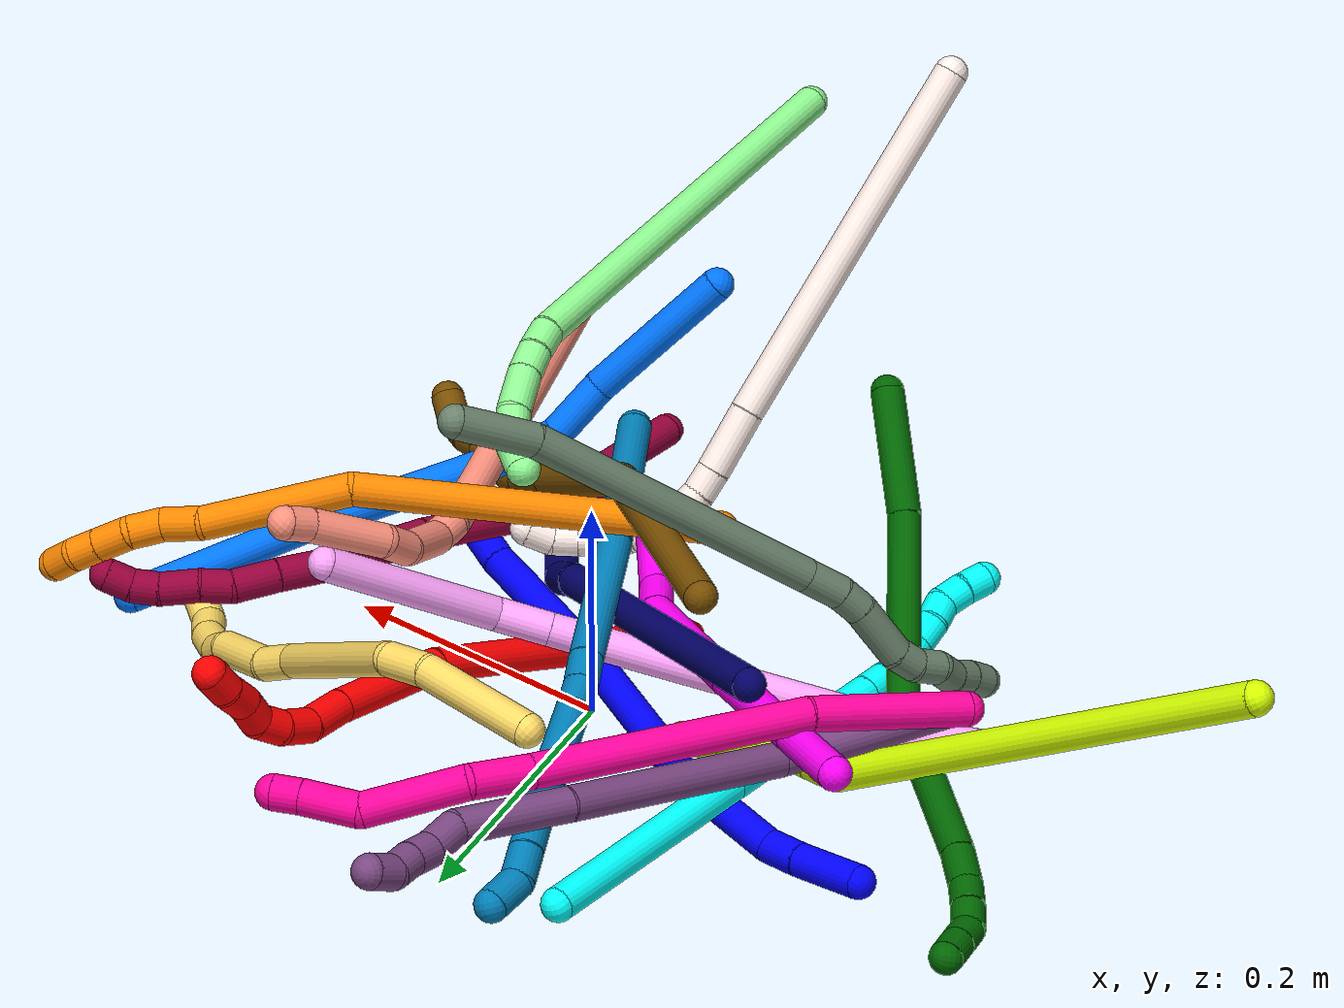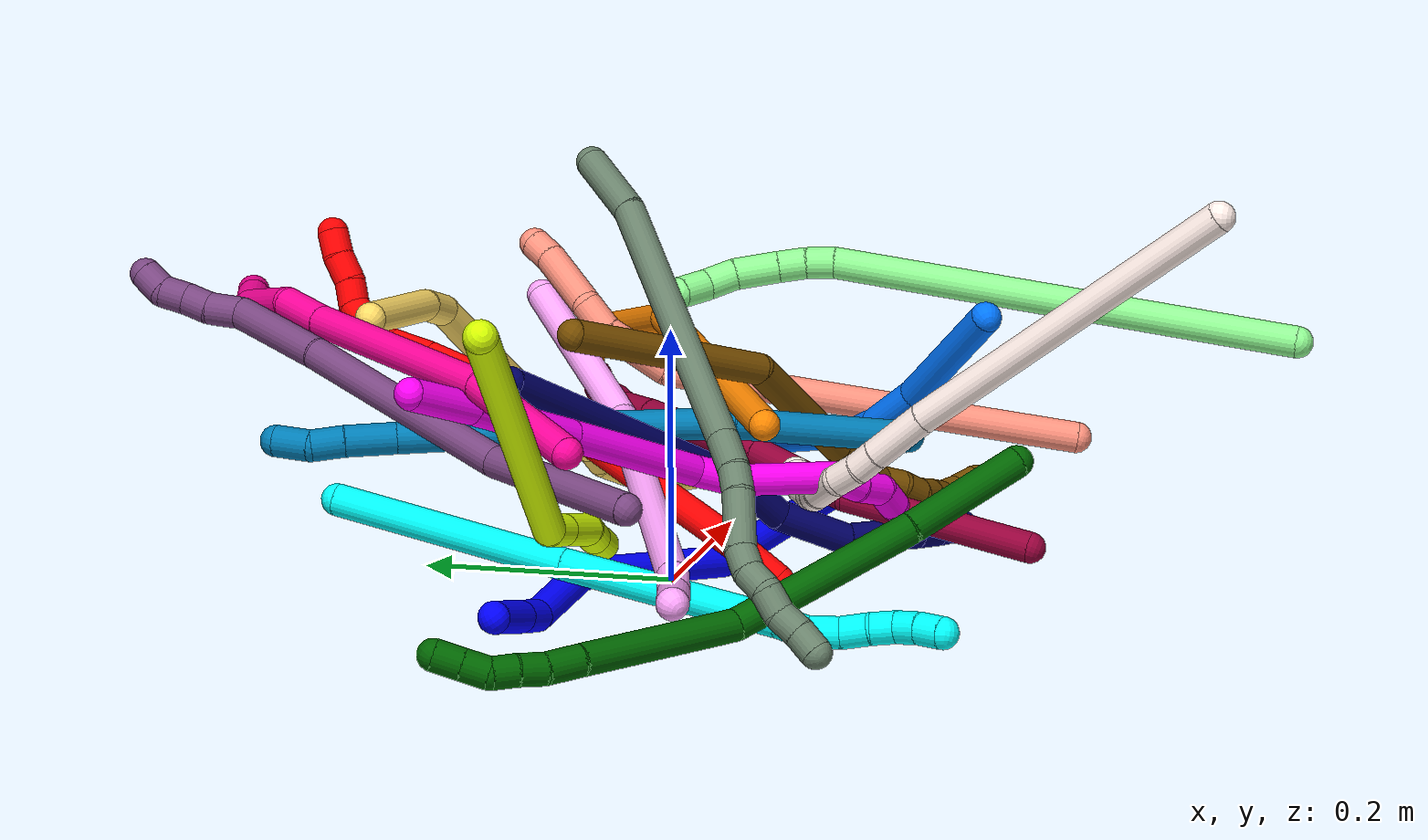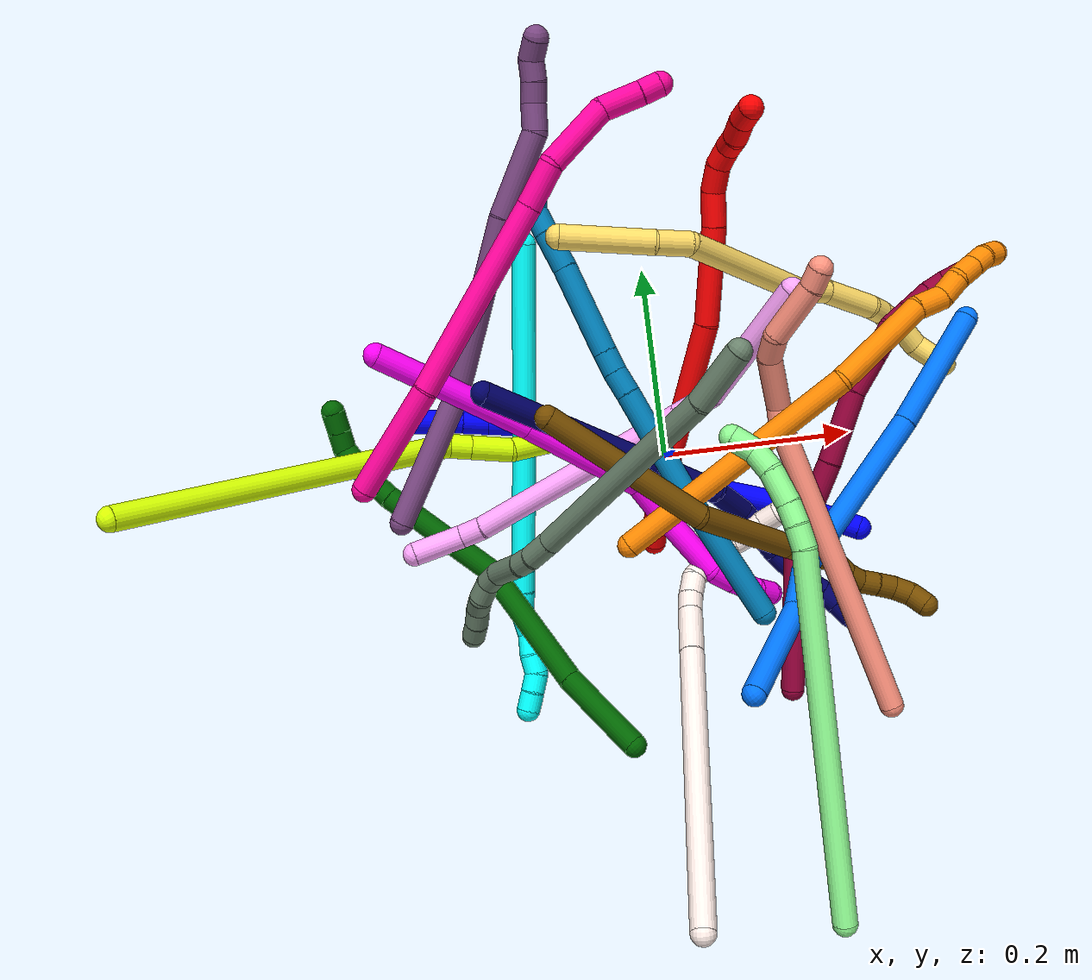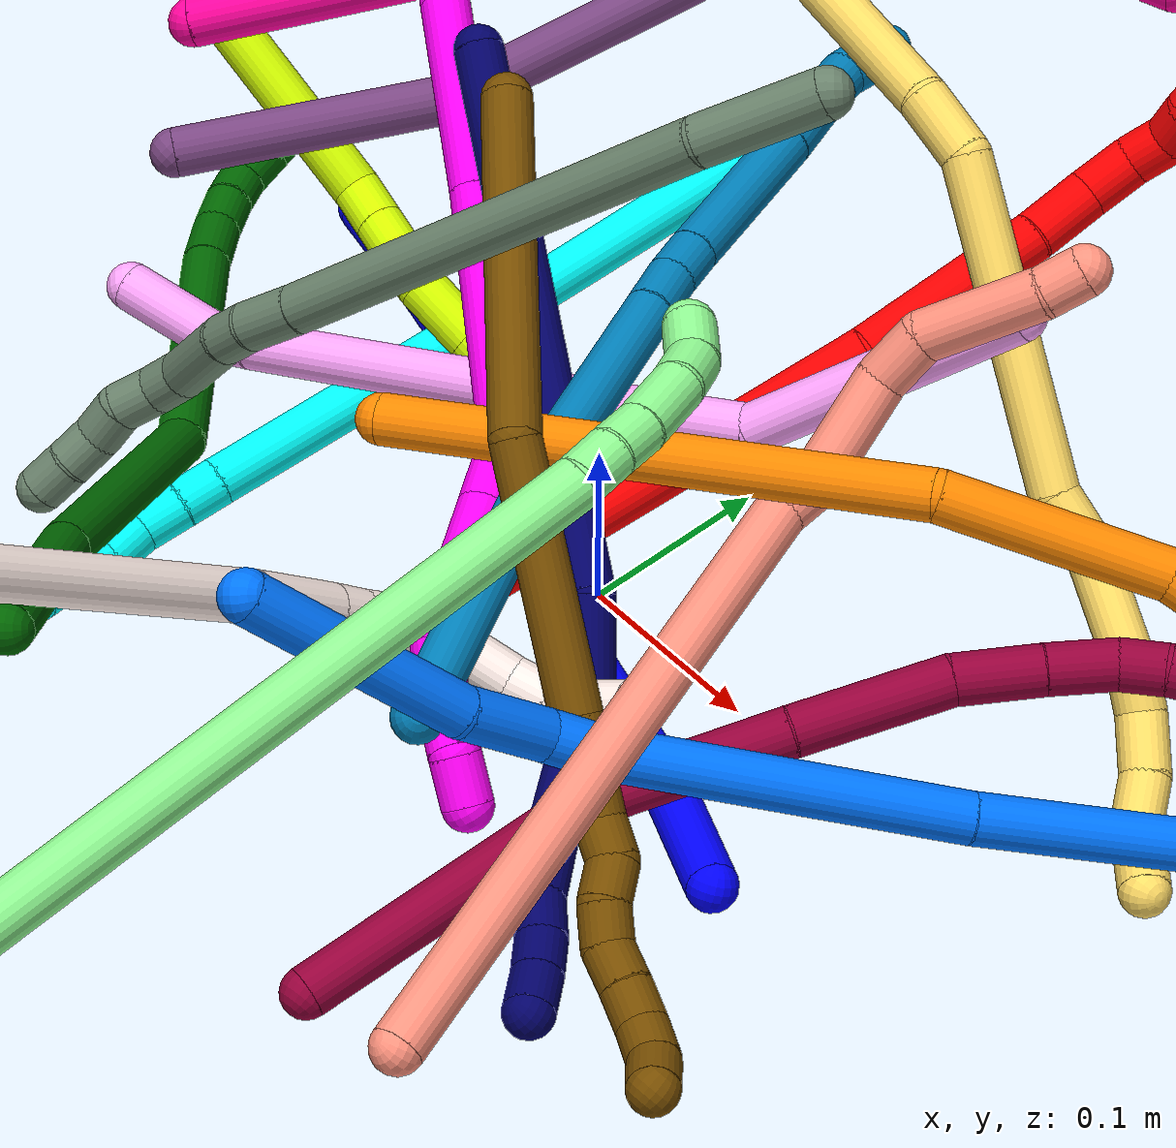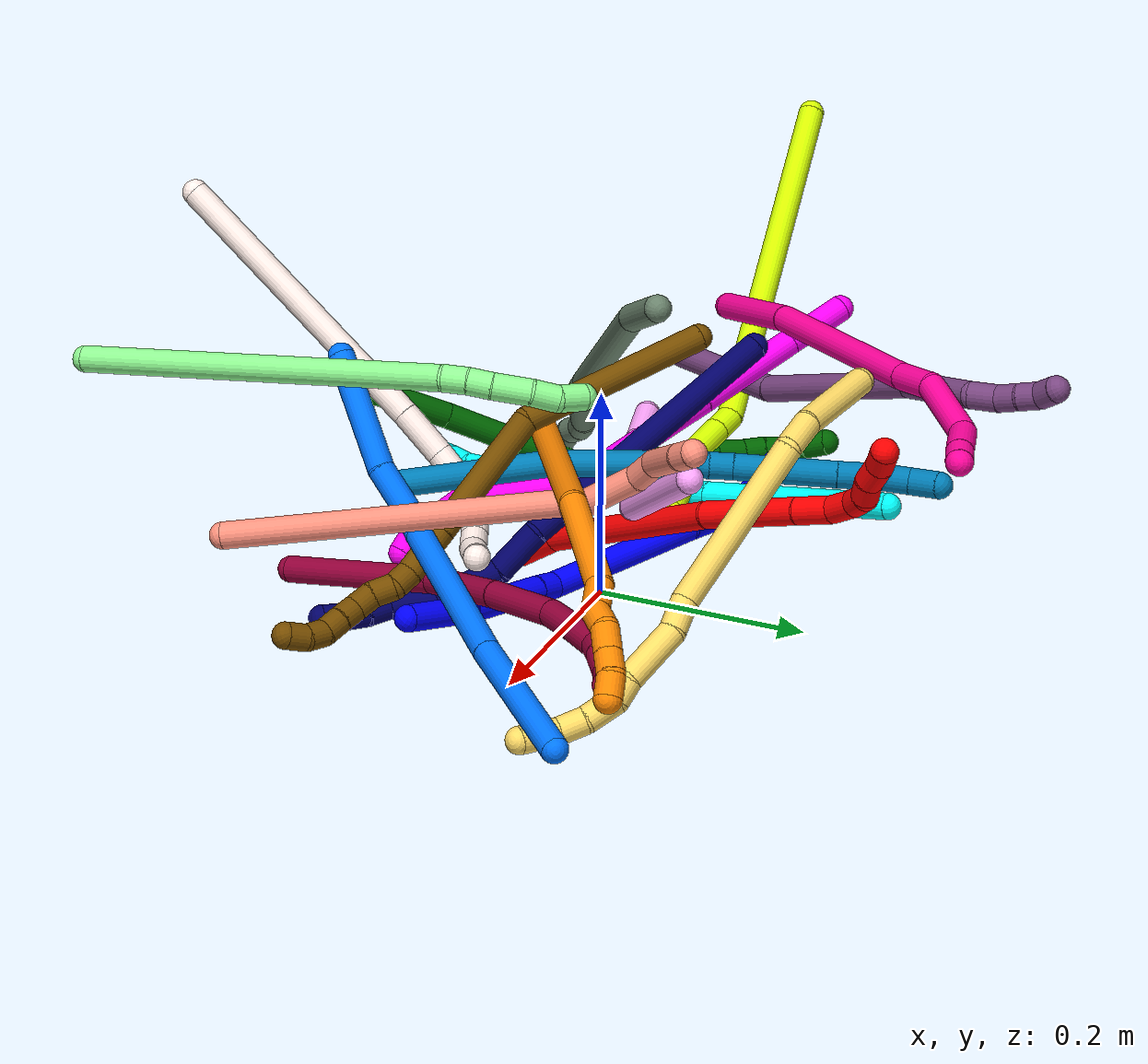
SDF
<sdf version="1.7">
 <world name="default">
  <plugin name="TubeGeneratorPlugin" filename="libtube_generator_plugin.so"/>
  <model name="photoneo_s_sensor">
   <static>1</static>
   <pose>0 0 2 1.57079 1.57079 3.14159</pose>
   <link name="link">
    <inertial><mass>0.1</mass></inertial>
    <sensor name="sensor" type="depth">
     <update_rate>30</update_rate>
     <camera>
      <horizontal_fov>1.22</horizontal_fov>
      <image><width>1920</width><height>1200</height><format>B8G8R8</format></image>
      <clip><near>0.1</near><far>4</far></clip>
      <depth_camera><output>points</output></depth_camera>
     </camera>
     <plugin name="camera_plugin" filename="libgazebo_ros_depth_camera.so">
      <baseline>0.2</baseline>
      <alwaysOn>1</alwaysOn>
      <updateRate>0.0</updateRate>
      <cameraName>camera_ir</cameraName>
      <imageTopicName>/camera/color/image_raw</imageTopicName>
      <cameraInfoTopicName>/camera/color/camera_info</cameraInfoTopicName>
      <depthImageTopicName>/camera/depth/image_raw</depthImageTopicName>
      <depthImageCameraInfoTopicName>/camera/depth/camera_info</depthImageCameraInfoTopicName>
      <pointCloudTopicName>/camera/depth/points</pointCloudTopicName>
      <frameName>fr_optical</frameName>
      <pointCloudCutoff>0.1</pointCloudCutoff>
      <pointCloudCutoffMax>2.0</pointCloudCutoffMax>
      <distortionK1>0</distortionK1>
      <distortionK2>0</distortionK2>
      <distortionK3>0</distortionK3>
      <distortionT1>0</distortionT1>
      <distortionT2>0</distortionT2>
      <CxPrime>0</CxPrime>
      <Cx>0</Cx>
      <Cy>0</Cy>
      <focalLength>0</focalLength>
      <hackBaseline>0</hackBaseline>
     </plugin>
    </sensor>
   </link>
  </model>
  <gravity>0 0 -9.8</gravity>
  <magnetic_field>6e-06 2.3e-05 -4.2e-05</magnetic_field>
  <atmosphere type="adiabatic"/>
  <physics name="default_physics" default="0" type="ode">
   <max_step_size>0.003</max_step_size>
   <real_time_factor>1</real_time_factor>
   <real_time_update_rate>1000</real_time_update_rate>
   <max_contacts>10000</max_contacts>
   <ode>
    <solver>
     <type>quick</type>
     <iters>100</iters>
     <sor>1.3</sor>
     <use_dynamic_moi_rescaling>0</use_dynamic_moi_rescaling>
    </solver>
    <constraints>
     <contact_max_correcting_vel>0</contact_max_correcting_vel>
     <contact_surface_layer>0.001</contact_surface_layer>
     <cfm>0</cfm>
     <erp>0.2</erp>
    </constraints>
   </ode>
  </physics>
  <scene><ambient>0.4 0.4 0.4 1</ambient><background>0.7 0.7 0.7 1</background><shadows>0</shadows></scene>
  <audio><device>default</device></audio>
  <spherical_coordinates>
   <surface_model>EARTH_WGS84</surface_model>
   <latitude_deg>0</latitude_deg>
   <longitude_deg>0</longitude_deg>
   <elevation>0</elevation>
   <heading_deg>0</heading_deg>
  </spherical_coordinates>
  <model name="bin">
   <static>1</static>
   <link name="bottom">
    <collision name="collision-bottom">
     <pose>0 0 -0.01 0 -0 0</pose>
     <geometry><box><size>0.8 0.6 0.02</size></box></geometry>
     <surface>
      <friction><ode><mu>100</mu><mu2>100</mu2></ode></friction>
      <contact><collide_bitmask>65535</collide_bitmask></contact>
     </surface>
    </collision>
   </link>
   <link name="west_wall">
    <collision name="collision-west_wall">
     <pose>-0.41 0 0.1 0 -0 0</pose>
     <geometry><box><size>0.02 0.6 0.2</size></box></geometry>
     <surface>
      <friction><ode><mu>100</mu><mu2>100</mu2></ode></friction>
      <contact><collide_bitmask>65535</collide_bitmask></contact>
     </surface>
    </collision>
   </link>
   <link name="east_wall">
    <collision name="collision-east_wall">
     <pose>0.41 0 0.1 0 -0 0</pose>
     <geometry><box><size>0.02 0.6 0.2</size></box></geometry>
     <surface>
      <friction><ode><mu>100</mu><mu2>100</mu2></ode></friction>
      <contact><collide_bitmask>65535</collide_bitmask></contact>
     </surface>
    </collision>
   </link>
   <link name="south_wall">
    <collision name="collision-south_wall">
     <pose>0 -0.31 0.1 0 -0 0</pose>
     <geometry><box><size>0.8 0.02 0.2</size></box></geometry>
     <surface>
      <friction><ode><mu>100</mu><mu2>100</mu2></ode></friction>
      <contact><collide_bitmask>65535</collide_bitmask></contact>
     </surface>
    </collision>
   </link>
   <link name="north_wall">
    <collision name="collision-north_wall">
     <pose>0 0.31 0.1 0 -0 0</pose>
     <geometry><box><size>0.8 0.02 0.2</size></box></geometry>
     <surface>
      <friction><ode><mu>100</mu><mu2>100</mu2></ode></friction>
      <contact><collide_bitmask>65535</collide_bitmask></contact>
     </surface>
    </collision>
   </link>
  </model>
  <model name="1">
   <static>0</static>
   <link name="1">
    <collision name="collision-cylinder-e_1_1_4">
     <pose>-0.035044 -0.00153 -0.009193 2.97664 -1.31087 -2.92738</pose>
     <geometry><cylinder><radius>0.0125</radius><length>0.072525</length></cylinder></geometry>
     <surface>
      <friction><ode><mu>1.16</mu><mu2>1.16</mu2><slip1>0</slip1><slip2>0</slip2></ode></friction>
      <contact><ode><kp>1e+06</kp><kd>1</kd><max_vel>0</max_vel><min_depth>0.001</min_depth></ode></contact>
     </surface>
    </collision>
    <visual name="visual-cylinder-e_1_1_4">
     <pose>-0.035044 -0.00153 -0.009193 2.97664 -1.31087 -2.92738</pose>
     <geometry><cylinder><radius>0.0125</radius><length>0.072525</length></cylinder></geometry>
     <material><ambient>0 0 1 1</ambient></material>
    </visual>
    <collision name="collision-cylinder-e_2_4_5">
     <pose>-0.111961 0.001155 -0.02967 -2.784 -1.29071 2.67043</pose>
     <geometry><cylinder><radius>0.0125</radius><length>0.087141</length></cylinder></geometry>
     <surface>
      <friction><ode><mu>1.16</mu><mu2>1.16</mu2><slip1>0</slip1><slip2>0</slip2></ode></friction>
      <contact><ode><kp>1e+06</kp><kd>1</kd><max_vel>0</max_vel><min_depth>0.001</min_depth></ode></contact>
     </surface>
    </collision>
    <visual name="visual-cylinder-e_2_4_5">
     <pose>-0.111961 0.001155 -0.02967 -2.784 -1.29071 2.67043</pose>
     <geometry><cylinder><radius>0.0125</radius><length>0.087141</length></cylinder></geometry>
     <material><ambient>0 0 1 1</ambient></material>
    </visual>
    <collision name="collision-cylinder-e_3_5_6">
     <pose>-0.165104 0.006211 -0.043546 -2.82829 -1.33344 2.74544</pose>
     <geometry><cylinder><radius>0.0125</radius><length>0.02319</length></cylinder></geometry>
     <surface>
      <friction><ode><mu>1.16</mu><mu2>1.16</mu2><slip1>0</slip1><slip2>0</slip2></ode></friction>
      <contact><ode><kp>1e+06</kp><kd>1</kd><max_vel>0</max_vel><min_depth>0.001</min_depth></ode></contact>
     </surface>
    </collision>
    <visual name="visual-cylinder-e_3_5_6">
     <pose>-0.165104 0.006211 -0.043546 -2.82829 -1.33344 2.74544</pose>
     <geometry><cylinder><radius>0.0125</radius><length>0.02319</length></cylinder></geometry>
     <material><ambient>0 0 1 1</ambient></material>
    </visual>
    <collision name="collision-cylinder-e_4_6_7">
     <pose>-0.241044 0.006385 -0.087915 3.12565 -0.997198 -3.11231</pose>
     <geometry><cylinder><radius>0.0125</radius><length>0.153986</length></cylinder></geometry>
     <surface>
      <friction><ode><mu>1.16</mu><mu2>1.16</mu2><slip1>0</slip1><slip2>0</slip2></ode></friction>
      <contact><ode><kp>1e+06</kp><kd>1</kd><max_vel>0</max_vel><min_depth>0.001</min_depth></ode></contact>
     </surface>
    </collision>
    <visual name="visual-cylinder-e_4_6_7">
     <pose>-0.241044 0.006385 -0.087915 3.12565 -0.997198 -3.11231</pose>
     <geometry><cylinder><radius>0.0125</radius><length>0.153986</length></cylinder></geometry>
     <material><ambient>0 0 1 1</ambient></material>
    </visual>
    <collision name="collision-cylinder-e_5_7_8">
     <pose>-0.344613 0.014561 -0.136044 -2.19385 -1.29787 1.95257</pose>
     <geometry><cylinder><radius>0.0125</radius><length>0.080786</length></cylinder></geometry>
     <surface>
      <friction><ode><mu>1.16</mu><mu2>1.16</mu2><slip1>0</slip1><slip2>0</slip2></ode></friction>
      <contact><ode><kp>1e+06</kp><kd>1</kd><max_vel>0</max_vel><min_depth>0.001</min_depth></ode></contact>
     </surface>
    </collision>
    <visual name="visual-cylinder-e_5_7_8">
     <pose>-0.344613 0.014561 -0.136044 -2.19385 -1.29787 1.95257</pose>
     <geometry><cylinder><radius>0.0125</radius><length>0.080786</length></cylinder></geometry>
     <material><ambient>0 0 1 1</ambient></material>
    </visual>
    <collision name="collision-cylinder-e_6_8_9">
     <pose>-0.395558 0.028862 -0.149244 -2.46849 -0.942297 1.93798</pose>
     <geometry><cylinder><radius>0.0125</radius><length>0.029787</length></cylinder></geometry>
     <surface>
      <friction><ode><mu>1.16</mu><mu2>1.16</mu2><slip1>0</slip1><slip2>0</slip2></ode></friction>
      <contact><ode><kp>1e+06</kp><kd>1</kd><max_vel>0</max_vel><min_depth>0.001</min_depth></ode></contact>
     </surface>
    </collision>
    <visual name="visual-cylinder-e_6_8_9">
     <pose>-0.395558 0.028862 -0.149244 -2.46849 -0.942297 1.93798</pose>
     <geometry><cylinder><radius>0.0125</radius><length>0.029787</length></cylinder></geometry>
     <material><ambient>0 0 1 1</ambient></material>
    </visual>
    <collision name="collision-cylinder-e_7_9_2">
     <pose>-0.428262 0.045408 -0.167995 -2.39171 -0.903697 1.77889</pose>
     <geometry><cylinder><radius>0.0125</radius><length>0.052585</length></cylinder></geometry>
     <surface>
      <friction><ode><mu>1.16</mu><mu2>1.16</mu2><slip1>0</slip1><slip2>0</slip2></ode></friction>
      <contact><ode><kp>1e+06</kp><kd>1</kd><max_vel>0</max_vel><min_depth>0.001</min_depth></ode></contact>
     </surface>
    </collision>
    <visual name="visual-cylinder-e_7_9_2">
     <pose>-0.428262 0.045408 -0.167995 -2.39171 -0.903697 1.77889</pose>
     <geometry><cylinder><radius>0.0125</radius><length>0.052585</length></cylinder></geometry>
     <material><ambient>0 0 1 1</ambient></material>
    </visual>
    <collision name="collision-sphere-2">
     <pose>-0.448917 0.056495 -0.179899 0 -0 0</pose>
     <geometry><sphere><radius>0.0125</radius></sphere></geometry>
     <surface>
      <friction><ode><mu>1.16</mu><mu2>1.16</mu2><slip1>0</slip1><slip2>0</slip2></ode></friction>
      <contact><ode><kp>1e+06</kp><kd>1</kd><max_vel>0</max_vel><min_depth>0.001</min_depth></ode></contact>
     </surface>
    </collision>
    <visual name="visual-sphere-2">
     <pose>-0.448917 0.056495 -0.179899 0 -0 0</pose>
     <geometry><sphere><radius>0.0125</radius></sphere></geometry>
     <material><ambient>0 0 1 1</ambient></material>
    </visual>
    <collision name="collision-sphere-9">
     <pose>-0.407606 0.034321 -0.156091 0 -0 0</pose>
     <geometry><sphere><radius>0.0125</radius></sphere></geometry>
     <surface>
      <friction><ode><mu>1.16</mu><mu2>1.16</mu2><slip1>0</slip1><slip2>0</slip2></ode></friction>
      <contact><ode><kp>1e+06</kp><kd>1</kd><max_vel>0</max_vel><min_depth>0.001</min_depth></ode></contact>
     </surface>
    </collision>
    <visual name="visual-sphere-9">
     <pose>-0.407606 0.034321 -0.156091 0 -0 0</pose>
     <geometry><sphere><radius>0.0125</radius></sphere></geometry>
     <material><ambient>0 0 1 1</ambient></material>
    </visual>
    <collision name="collision-sphere-4">
     <pose>-0.070089 -0.003061 -0.018387 0 -0 0</pose>
     <geometry><sphere><radius>0.0125</radius></sphere></geometry>
     <surface>
      <friction><ode><mu>1.16</mu><mu2>1.16</mu2><slip1>0</slip1><slip2>0</slip2></ode></friction>
      <contact><ode><kp>1e+06</kp><kd>1</kd><max_vel>0</max_vel><min_depth>0.001</min_depth></ode></contact>
     </surface>
    </collision>
    <visual name="visual-sphere-4">
     <pose>-0.070089 -0.003061 -0.018387 0 -0 0</pose>
     <geometry><sphere><radius>0.0125</radius></sphere></geometry>
     <material><ambient>0 0 1 1</ambient></material>
    </visual>
    <collision name="collision-sphere-1">
     <geometry><sphere><radius>0.0125</radius></sphere></geometry>
     <surface>
      <friction><ode><mu>1.16</mu><mu2>1.16</mu2><slip1>0</slip1><slip2>0</slip2></ode></friction>
      <contact><ode><kp>1e+06</kp><kd>1</kd><max_vel>0</max_vel><min_depth>0.001</min_depth></ode></contact>
     </surface>
    </collision>
    <visual name="visual-sphere-1">
     <geometry><sphere><radius>0.0125</radius></sphere></geometry>
     <material><ambient>0 0 1 1</ambient></material>
    </visual>
    <collision name="collision-sphere-8">
     <pose>-0.383511 0.023404 -0.142398 0 -0 0</pose>
     <geometry><sphere><radius>0.0125</radius></sphere></geometry>
     <surface>
      <friction><ode><mu>1.16</mu><mu2>1.16</mu2><slip1>0</slip1><slip2>0</slip2></ode></friction>
      <contact><ode><kp>1e+06</kp><kd>1</kd><max_vel>0</max_vel><min_depth>0.001</min_depth></ode></contact>
     </surface>
    </collision>
    <visual name="visual-sphere-8">
     <pose>-0.383511 0.023404 -0.142398 0 -0 0</pose>
     <geometry><sphere><radius>0.0125</radius></sphere></geometry>
     <material><ambient>0 0 1 1</ambient></material>
    </visual>
    <collision name="collision-sphere-5">
     <pose>-0.153833 0.005371 -0.040952 0 -0 0</pose>
     <geometry><sphere><radius>0.0125</radius></sphere></geometry>
     <surface>
      <friction><ode><mu>1.16</mu><mu2>1.16</mu2><slip1>0</slip1><slip2>0</slip2></ode></friction>
      <contact><ode><kp>1e+06</kp><kd>1</kd><max_vel>0</max_vel><min_depth>0.001</min_depth></ode></contact>
     </surface>
    </collision>
    <visual name="visual-sphere-5">
     <pose>-0.153833 0.005371 -0.040952 0 -0 0</pose>
     <geometry><sphere><radius>0.0125</radius></sphere></geometry>
     <material><ambient>0 0 1 1</ambient></material>
    </visual>
    <collision name="collision-sphere-6">
     <pose>-0.176374 0.007052 -0.04614 0 -0 0</pose>
     <geometry><sphere><radius>0.0125</radius></sphere></geometry>
     <surface>
      <friction><ode><mu>1.16</mu><mu2>1.16</mu2><slip1>0</slip1><slip2>0</slip2></ode></friction>
      <contact><ode><kp>1e+06</kp><kd>1</kd><max_vel>0</max_vel><min_depth>0.001</min_depth></ode></contact>
     </surface>
    </collision>
    <visual name="visual-sphere-6">
     <pose>-0.176374 0.007052 -0.04614 0 -0 0</pose>
     <geometry><sphere><radius>0.0125</radius></sphere></geometry>
     <material><ambient>0 0 1 1</ambient></material>
    </visual>
    <collision name="collision-sphere-7">
     <pose>-0.305715 0.005719 -0.129691 0 -0 0</pose>
     <geometry><sphere><radius>0.0125</radius></sphere></geometry>
     <surface>
      <friction><ode><mu>1.16</mu><mu2>1.16</mu2><slip1>0</slip1><slip2>0</slip2></ode></friction>
      <contact><ode><kp>1e+06</kp><kd>1</kd><max_vel>0</max_vel><min_depth>0.001</min_depth></ode></contact>
     </surface>
    </collision>
    <visual name="visual-sphere-7">
     <pose>-0.305715 0.005719 -0.129691 0 -0 0</pose>
     <geometry><sphere><radius>0.0125</radius></sphere></geometry>
     <material><ambient>0 0 1 1</ambient></material>
    </visual>
    <inertial>
     <pose>-0.230773 0.011082 -0.084139 0 -0 0</pose>
     <mass>0.5</mass>
     <inertia>
      <ixx>-0.000211</ixx>
      <ixy>0</ixy>
      <ixz>0</ixz>
      <iyy>0.000488</iyy>
      <iyz>0</iyz>
      <izz>0.000378</izz>
     </inertia>
    </inertial>
   </link>
   <pose>0.1925 -0.102468 0.040972 2.69759 -0.410841 -0.30313</pose>
  </model>
  <model name="2">
   <static>0</static>
   <link name="2">
    <collision name="collision-cylinder-e_1_1_4">
     <pose>0.00917 0.008832 0.019747 -0.420569 0.400967 -0.086693</pose>
     <geometry><cylinder><radius>0.0125</radius><length>0.04699</length></cylinder></geometry>
     <surface>
      <friction><ode><mu>1.16</mu><mu2>1.16</mu2><slip1>0</slip1><slip2>0</slip2></ode></friction>
      <contact><ode><kp>1e+06</kp><kd>1</kd><max_vel>0</max_vel><min_depth>0.001</min_depth></ode></contact>
     </surface>
    </collision>
    <visual name="visual-cylinder-e_1_1_4">
     <pose>0.00917 0.008832 0.019747 -0.420569 0.400967 -0.086693</pose>
     <geometry><cylinder><radius>0.0125</radius><length>0.04699</length></cylinder></geometry>
     <material><ambient>1 0 0 1</ambient></material>
    </visual>
    <collision name="collision-cylinder-e_2_4_5">
     <pose>0.034302 0.060123 0.133983 -0.422314 0.152873 -0.03283</pose>
     <geometry><cylinder><radius>0.0125</radius><length>0.209627</length></cylinder></geometry>
     <surface>
      <friction><ode><mu>1.16</mu><mu2>1.16</mu2><slip1>0</slip1><slip2>0</slip2></ode></friction>
      <contact><ode><kp>1e+06</kp><kd>1</kd><max_vel>0</max_vel><min_depth>0.001</min_depth></ode></contact>
     </surface>
    </collision>
    <visual name="visual-cylinder-e_2_4_5">
     <pose>0.034302 0.060123 0.133983 -0.422314 0.152873 -0.03283</pose>
     <geometry><cylinder><radius>0.0125</radius><length>0.209627</length></cylinder></geometry>
     <material><ambient>1 0 0 1</ambient></material>
    </visual>
    <collision name="collision-cylinder-e_3_5_6">
     <pose>0.059384 0.11224 0.275722 -0.20164 0.186945 -0.018967</pose>
     <geometry><cylinder><radius>0.0125</radius><length>0.098161</length></cylinder></geometry>
     <surface>
      <friction><ode><mu>1.16</mu><mu2>1.16</mu2><slip1>0</slip1><slip2>0</slip2></ode></friction>
      <contact><ode><kp>1e+06</kp><kd>1</kd><max_vel>0</max_vel><min_depth>0.001</min_depth></ode></contact>
     </surface>
    </collision>
    <visual name="visual-cylinder-e_3_5_6">
     <pose>0.059384 0.11224 0.275722 -0.20164 0.186945 -0.018967</pose>
     <geometry><cylinder><radius>0.0125</radius><length>0.098161</length></cylinder></geometry>
     <material><ambient>1 0 0 1</ambient></material>
    </visual>
    <collision name="collision-cylinder-e_4_6_7">
     <pose>0.07249 0.12352 0.339565 -0.097395 0.234536 -0.011483</pose>
     <geometry><cylinder><radius>0.0125</radius><length>0.034286</length></cylinder></geometry>
     <surface>
      <friction><ode><mu>1.16</mu><mu2>1.16</mu2><slip1>0</slip1><slip2>0</slip2></ode></friction>
      <contact><ode><kp>1e+06</kp><kd>1</kd><max_vel>0</max_vel><min_depth>0.001</min_depth></ode></contact>
     </surface>
    </collision>
    <visual name="visual-cylinder-e_4_6_7">
     <pose>0.07249 0.12352 0.339565 -0.097395 0.234536 -0.011483</pose>
     <geometry><cylinder><radius>0.0125</radius><length>0.034286</length></cylinder></geometry>
     <material><ambient>1 0 0 1</ambient></material>
    </visual>
    <collision name="collision-cylinder-e_5_7_8">
     <pose>0.079843 0.130614 0.367891 -0.436484 0.254626 -0.056761</pose>
     <geometry><cylinder><radius>0.0125</radius><length>0.026752</length></cylinder></geometry>
     <surface>
      <friction><ode><mu>1.16</mu><mu2>1.16</mu2><slip1>0</slip1><slip2>0</slip2></ode></friction>
      <contact><ode><kp>1e+06</kp><kd>1</kd><max_vel>0</max_vel><min_depth>0.001</min_depth></ode></contact>
     </surface>
    </collision>
    <visual name="visual-cylinder-e_5_7_8">
     <pose>0.079843 0.130614 0.367891 -0.436484 0.254626 -0.056761</pose>
     <geometry><cylinder><radius>0.0125</radius><length>0.026752</length></cylinder></geometry>
     <material><ambient>1 0 0 1</ambient></material>
    </visual>
    <collision name="collision-cylinder-e_6_8_9">
     <pose>0.084895 0.143055 0.387125 -0.748469 0.162814 -0.064064</pose>
     <geometry><cylinder><radius>0.0125</radius><length>0.020755</length></cylinder></geometry>
     <surface>
      <friction><ode><mu>1.16</mu><mu2>1.16</mu2><slip1>0</slip1><slip2>0</slip2></ode></friction>
      <contact><ode><kp>1e+06</kp><kd>1</kd><max_vel>0</max_vel><min_depth>0.001</min_depth></ode></contact>
     </surface>
    </collision>
    <visual name="visual-cylinder-e_6_8_9">
     <pose>0.084895 0.143055 0.387125 -0.748469 0.162814 -0.064064</pose>
     <geometry><cylinder><radius>0.0125</radius><length>0.020755</length></cylinder></geometry>
     <material><ambient>1 0 0 1</ambient></material>
    </visual>
    <collision name="collision-cylinder-e_7_9_10">
     <pose>0.091236 0.1584 0.398029 -1.18517 0.475895 -0.323751</pose>
     <geometry><cylinder><radius>0.0125</radius><length>0.020339</length></cylinder></geometry>
     <surface>
      <friction><ode><mu>1.16</mu><mu2>1.16</mu2><slip1>0</slip1><slip2>0</slip2></ode></friction>
      <contact><ode><kp>1e+06</kp><kd>1</kd><max_vel>0</max_vel><min_depth>0.001</min_depth></ode></contact>
     </surface>
    </collision>
    <visual name="visual-cylinder-e_7_9_10">
     <pose>0.091236 0.1584 0.398029 -1.18517 0.475895 -0.323751</pose>
     <geometry><cylinder><radius>0.0125</radius><length>0.020339</length></cylinder></geometry>
     <material><ambient>1 0 0 1</ambient></material>
    </visual>
    <collision name="collision-cylinder-e_8_10_11">
     <pose>0.101037 0.174613 0.40769 -0.89672 0.473625 -0.231152</pose>
     <geometry><cylinder><radius>0.0125</radius><length>0.022545</length></cylinder></geometry>
     <surface>
      <friction><ode><mu>1.16</mu><mu2>1.16</mu2><slip1>0</slip1><slip2>0</slip2></ode></friction>
      <contact><ode><kp>1e+06</kp><kd>1</kd><max_vel>0</max_vel><min_depth>0.001</min_depth></ode></contact>
     </surface>
    </collision>
    <visual name="visual-cylinder-e_8_10_11">
     <pose>0.101037 0.174613 0.40769 -0.89672 0.473625 -0.231152</pose>
     <geometry><cylinder><radius>0.0125</radius><length>0.022545</length></cylinder></geometry>
     <material><ambient>1 0 0 1</ambient></material>
    </visual>
    <collision name="collision-cylinder-e_9_11_2">
     <pose>0.110157 0.190908 0.418213 -1.10413 0.397722 -0.246996</pose>
     <geometry><cylinder><radius>0.0125</radius><length>0.020543</length></cylinder></geometry>
     <surface>
      <friction><ode><mu>1.16</mu><mu2>1.16</mu2><slip1>0</slip1><slip2>0</slip2></ode></friction>
      <contact><ode><kp>1e+06</kp><kd>1</kd><max_vel>0</max_vel><min_depth>0.001</min_depth></ode></contact>
     </surface>
    </collision>
    <visual name="visual-cylinder-e_9_11_2">
     <pose>0.110157 0.190908 0.418213 -1.10413 0.397722 -0.246996</pose>
     <geometry><cylinder><radius>0.0125</radius><length>0.020543</length></cylinder></geometry>
     <material><ambient>1 0 0 1</ambient></material>
    </visual>
    <collision name="collision-sphere-2">
     <pose>0.114135 0.199365 0.422473 0 -0 0</pose>
     <geometry><sphere><radius>0.0125</radius></sphere></geometry>
     <surface>
      <friction><ode><mu>1.16</mu><mu2>1.16</mu2><slip1>0</slip1><slip2>0</slip2></ode></friction>
      <contact><ode><kp>1e+06</kp><kd>1</kd><max_vel>0</max_vel><min_depth>0.001</min_depth></ode></contact>
     </surface>
    </collision>
    <visual name="visual-sphere-2">
     <pose>0.114135 0.199365 0.422473 0 -0 0</pose>
     <geometry><sphere><radius>0.0125</radius></sphere></geometry>
     <material><ambient>1 0 0 1</ambient></material>
    </visual>
    <collision name="collision-sphere-11">
     <pose>0.106178 0.182451 0.413952 0 -0 0</pose>
     <geometry><sphere><radius>0.0125</radius></sphere></geometry>
     <surface>
      <friction><ode><mu>1.16</mu><mu2>1.16</mu2><slip1>0</slip1><slip2>0</slip2></ode></friction>
      <contact><ode><kp>1e+06</kp><kd>1</kd><max_vel>0</max_vel><min_depth>0.001</min_depth></ode></contact>
     </surface>
    </collision>
    <visual name="visual-sphere-11">
     <pose>0.106178 0.182451 0.413952 0 -0 0</pose>
     <geometry><sphere><radius>0.0125</radius></sphere></geometry>
     <material><ambient>1 0 0 1</ambient></material>
    </visual>
    <collision name="collision-sphere-10">
     <pose>0.095895 0.166775 0.401429 0 -0 0</pose>
     <geometry><sphere><radius>0.0125</radius></sphere></geometry>
     <surface>
      <friction><ode><mu>1.16</mu><mu2>1.16</mu2><slip1>0</slip1><slip2>0</slip2></ode></friction>
      <contact><ode><kp>1e+06</kp><kd>1</kd><max_vel>0</max_vel><min_depth>0.001</min_depth></ode></contact>
     </surface>
    </collision>
    <visual name="visual-sphere-10">
     <pose>0.095895 0.166775 0.401429 0 -0 0</pose>
     <geometry><sphere><radius>0.0125</radius></sphere></geometry>
     <material><ambient>1 0 0 1</ambient></material>
    </visual>
    <collision name="collision-sphere-9">
     <pose>0.086577 0.150024 0.394628 0 -0 0</pose>
     <geometry><sphere><radius>0.0125</radius></sphere></geometry>
     <surface>
      <friction><ode><mu>1.16</mu><mu2>1.16</mu2><slip1>0</slip1><slip2>0</slip2></ode></friction>
      <contact><ode><kp>1e+06</kp><kd>1</kd><max_vel>0</max_vel><min_depth>0.001</min_depth></ode></contact>
     </surface>
    </collision>
    <visual name="visual-sphere-9">
     <pose>0.086577 0.150024 0.394628 0 -0 0</pose>
     <geometry><sphere><radius>0.0125</radius></sphere></geometry>
     <material><ambient>1 0 0 1</ambient></material>
    </visual>
    <collision name="collision-sphere-4">
     <pose>0.018341 0.017664 0.039493 0 -0 0</pose>
     <geometry><sphere><radius>0.0125</radius></sphere></geometry>
     <surface>
      <friction><ode><mu>1.16</mu><mu2>1.16</mu2><slip1>0</slip1><slip2>0</slip2></ode></friction>
      <contact><ode><kp>1e+06</kp><kd>1</kd><max_vel>0</max_vel><min_depth>0.001</min_depth></ode></contact>
     </surface>
    </collision>
    <visual name="visual-sphere-4">
     <pose>0.018341 0.017664 0.039493 0 -0 0</pose>
     <geometry><sphere><radius>0.0125</radius></sphere></geometry>
     <material><ambient>1 0 0 1</ambient></material>
    </visual>
    <collision name="collision-sphere-1">
     <geometry><sphere><radius>0.0125</radius></sphere></geometry>
     <surface>
      <friction><ode><mu>1.16</mu><mu2>1.16</mu2><slip1>0</slip1><slip2>0</slip2></ode></friction>
      <contact><ode><kp>1e+06</kp><kd>1</kd><max_vel>0</max_vel><min_depth>0.001</min_depth></ode></contact>
     </surface>
    </collision>
    <visual name="visual-sphere-1">
     <geometry><sphere><radius>0.0125</radius></sphere></geometry>
     <material><ambient>1 0 0 1</ambient></material>
    </visual>
    <collision name="collision-sphere-8">
     <pose>0.083213 0.136086 0.379621 0 -0 0</pose>
     <geometry><sphere><radius>0.0125</radius></sphere></geometry>
     <surface>
      <friction><ode><mu>1.16</mu><mu2>1.16</mu2><slip1>0</slip1><slip2>0</slip2></ode></friction>
      <contact><ode><kp>1e+06</kp><kd>1</kd><max_vel>0</max_vel><min_depth>0.001</min_depth></ode></contact>
     </surface>
    </collision>
    <visual name="visual-sphere-8">
     <pose>0.083213 0.136086 0.379621 0 -0 0</pose>
     <geometry><sphere><radius>0.0125</radius></sphere></geometry>
     <material><ambient>1 0 0 1</ambient></material>
    </visual>
    <collision name="collision-sphere-5">
     <pose>0.050262 0.102582 0.228473 0 -0 0</pose>
     <geometry><sphere><radius>0.0125</radius></sphere></geometry>
     <surface>
      <friction><ode><mu>1.16</mu><mu2>1.16</mu2><slip1>0</slip1><slip2>0</slip2></ode></friction>
      <contact><ode><kp>1e+06</kp><kd>1</kd><max_vel>0</max_vel><min_depth>0.001</min_depth></ode></contact>
     </surface>
    </collision>
    <visual name="visual-sphere-5">
     <pose>0.050262 0.102582 0.228473 0 -0 0</pose>
     <geometry><sphere><radius>0.0125</radius></sphere></geometry>
     <material><ambient>1 0 0 1</ambient></material>
    </visual>
    <collision name="collision-sphere-6">
     <pose>0.068506 0.121899 0.32297 0 -0 0</pose>
     <geometry><sphere><radius>0.0125</radius></sphere></geometry>
     <surface>
      <friction><ode><mu>1.16</mu><mu2>1.16</mu2><slip1>0</slip1><slip2>0</slip2></ode></friction>
      <contact><ode><kp>1e+06</kp><kd>1</kd><max_vel>0</max_vel><min_depth>0.001</min_depth></ode></contact>
     </surface>
    </collision>
    <visual name="visual-sphere-6">
     <pose>0.068506 0.121899 0.32297 0 -0 0</pose>
     <geometry><sphere><radius>0.0125</radius></sphere></geometry>
     <material><ambient>1 0 0 1</ambient></material>
    </visual>
    <collision name="collision-sphere-7">
     <pose>0.076474 0.125142 0.35616 0 -0 0</pose>
     <geometry><sphere><radius>0.0125</radius></sphere></geometry>
     <surface>
      <friction><ode><mu>1.16</mu><mu2>1.16</mu2><slip1>0</slip1><slip2>0</slip2></ode></friction>
      <contact><ode><kp>1e+06</kp><kd>1</kd><max_vel>0</max_vel><min_depth>0.001</min_depth></ode></contact>
     </surface>
    </collision>
    <visual name="visual-sphere-7">
     <pose>0.076474 0.125142 0.35616 0 -0 0</pose>
     <geometry><sphere><radius>0.0125</radius></sphere></geometry>
     <material><ambient>1 0 0 1</ambient></material>
    </visual>
    <inertial>
     <pose>0.052461 0.091629 0.222954 0 -0 0</pose>
     <mass>0.5</mass>
     <inertia>
      <ixx>0.00085</ixx>
      <ixy>0</ixy>
      <ixz>0</ixz>
      <iyy>0.000797</iyy>
      <iyz>0</iyz>
      <izz>-0.00045</izz>
     </inertia>
    </inertial>
   </link>
   <pose>-0.023703 -0.09172 0.011394 1.53398 -0.783834 2.99493</pose>
  </model>
  <model name="3">
   <static>0</static>
   <link name="3">
    <collision name="collision-cylinder-e_1_1_4">
     <pose>-0.032647 -0.086777 -0.024199 1.84275 -0.347669 -0.454565</pose>
     <geometry><cylinder><radius>0.0125</radius><length>0.191641</length></cylinder></geometry>
     <surface>
      <friction><ode><mu>1.16</mu><mu2>1.16</mu2><slip1>0</slip1><slip2>0</slip2></ode></friction>
      <contact><ode><kp>1e+06</kp><kd>1</kd><max_vel>0</max_vel><min_depth>0.001</min_depth></ode></contact>
     </surface>
    </collision>
    <visual name="visual-cylinder-e_1_1_4">
     <pose>-0.032647 -0.086777 -0.024199 1.84275 -0.347669 -0.454565</pose>
     <geometry><cylinder><radius>0.0125</radius><length>0.191641</length></cylinder></geometry>
     <material><ambient>0.003922 1 0.996078 1</ambient></material>
    </visual>
    <collision name="collision-cylinder-e_2_4_5">
     <pose>-0.092938 -0.243174 -0.066934 1.831 -0.366379 -0.473067</pose>
     <geometry><cylinder><radius>0.0125</radius><length>0.154334</length></cylinder></geometry>
     <surface>
      <friction><ode><mu>1.16</mu><mu2>1.16</mu2><slip1>0</slip1><slip2>0</slip2></ode></friction>
      <contact><ode><kp>1e+06</kp><kd>1</kd><max_vel>0</max_vel><min_depth>0.001</min_depth></ode></contact>
     </surface>
    </collision>
    <visual name="visual-cylinder-e_2_4_5">
     <pose>-0.092938 -0.243174 -0.066934 1.831 -0.366379 -0.473067</pose>
     <geometry><cylinder><radius>0.0125</radius><length>0.154334</length></cylinder></geometry>
     <material><ambient>0.003922 1 0.996078 1</ambient></material>
    </visual>
    <collision name="collision-cylinder-e_3_5_6">
     <pose>-0.124426 -0.322742 -0.088132 1.83229 -0.357245 -0.462038</pose>
     <geometry><cylinder><radius>0.0125</radius><length>0.021984</length></cylinder></geometry>
     <surface>
      <friction><ode><mu>1.16</mu><mu2>1.16</mu2><slip1>0</slip1><slip2>0</slip2></ode></friction>
      <contact><ode><kp>1e+06</kp><kd>1</kd><max_vel>0</max_vel><min_depth>0.001</min_depth></ode></contact>
     </surface>
    </collision>
    <visual name="visual-cylinder-e_3_5_6">
     <pose>-0.124426 -0.322742 -0.088132 1.83229 -0.357245 -0.462038</pose>
     <geometry><cylinder><radius>0.0125</radius><length>0.021984</length></cylinder></geometry>
     <material><ambient>0.003922 1 0.996078 1</ambient></material>
    </visual>
    <collision name="collision-cylinder-e_4_6_7">
     <pose>-0.132658 -0.343324 -0.094585 1.91325 -0.370706 -0.519792</pose>
     <geometry><cylinder><radius>0.0125</radius><length>0.024225</length></cylinder></geometry>
     <surface>
      <friction><ode><mu>1.16</mu><mu2>1.16</mu2><slip1>0</slip1><slip2>0</slip2></ode></friction>
      <contact><ode><kp>1e+06</kp><kd>1</kd><max_vel>0</max_vel><min_depth>0.001</min_depth></ode></contact>
     </surface>
    </collision>
    <visual name="visual-cylinder-e_4_6_7">
     <pose>-0.132658 -0.343324 -0.094585 1.91325 -0.370706 -0.519792</pose>
     <geometry><cylinder><radius>0.0125</radius><length>0.024225</length></cylinder></geometry>
     <material><ambient>0.003922 1 0.996078 1</ambient></material>
    </visual>
    <collision name="collision-cylinder-e_5_7_8">
     <pose>-0.138576 -0.366267 -0.097982 1.53877 -0.123598 -0.119711</pose>
     <geometry><cylinder><radius>0.0125</radius><length>0.02482</length></cylinder></geometry>
     <surface>
      <friction><ode><mu>1.16</mu><mu2>1.16</mu2><slip1>0</slip1><slip2>0</slip2></ode></friction>
      <contact><ode><kp>1e+06</kp><kd>1</kd><max_vel>0</max_vel><min_depth>0.001</min_depth></ode></contact>
     </surface>
    </collision>
    <visual name="visual-cylinder-e_5_7_8">
     <pose>-0.138576 -0.366267 -0.097982 1.53877 -0.123598 -0.119711</pose>
     <geometry><cylinder><radius>0.0125</radius><length>0.02482</length></cylinder></geometry>
     <material><ambient>0.003922 1 0.996078 1</ambient></material>
    </visual>
    <collision name="collision-cylinder-e_6_8_9">
     <pose>-0.144756 -0.38889 -0.096059 1.42369 -0.419589 -0.363351</pose>
     <geometry><cylinder><radius>0.0125</radius><length>0.022833</length></cylinder></geometry>
     <surface>
      <friction><ode><mu>1.16</mu><mu2>1.16</mu2><slip1>0</slip1><slip2>0</slip2></ode></friction>
      <contact><ode><kp>1e+06</kp><kd>1</kd><max_vel>0</max_vel><min_depth>0.001</min_depth></ode></contact>
     </surface>
    </collision>
    <visual name="visual-cylinder-e_6_8_9">
     <pose>-0.144756 -0.38889 -0.096059 1.42369 -0.419589 -0.363351</pose>
     <geometry><cylinder><radius>0.0125</radius><length>0.022833</length></cylinder></geometry>
     <material><ambient>0.003922 1 0.996078 1</ambient></material>
    </visual>
    <collision name="collision-cylinder-e_7_9_10">
     <pose>-0.151516 -0.408963 -0.093434 1.45881 -0.211547 -0.189232</pose>
     <geometry><cylinder><radius>0.0125</radius><length>0.020089</length></cylinder></geometry>
     <surface>
      <friction><ode><mu>1.16</mu><mu2>1.16</mu2><slip1>0</slip1><slip2>0</slip2></ode></friction>
      <contact><ode><kp>1e+06</kp><kd>1</kd><max_vel>0</max_vel><min_depth>0.001</min_depth></ode></contact>
     </surface>
    </collision>
    <visual name="visual-cylinder-e_7_9_10">
     <pose>-0.151516 -0.408963 -0.093434 1.45881 -0.211547 -0.189232</pose>
     <geometry><cylinder><radius>0.0125</radius><length>0.020089</length></cylinder></geometry>
     <material><ambient>0.003922 1 0.996078 1</ambient></material>
    </visual>
    <collision name="collision-cylinder-e_8_10_11">
     <pose>-0.159698 -0.426619 -0.093213 1.68136 -0.652509 -0.72277</pose>
     <geometry><cylinder><radius>0.0125</radius><length>0.020001</length></cylinder></geometry>
     <surface>
      <friction><ode><mu>1.16</mu><mu2>1.16</mu2><slip1>0</slip1><slip2>0</slip2></ode></friction>
      <contact><ode><kp>1e+06</kp><kd>1</kd><max_vel>0</max_vel><min_depth>0.001</min_depth></ode></contact>
     </surface>
    </collision>
    <visual name="visual-cylinder-e_8_10_11">
     <pose>-0.159698 -0.426619 -0.093213 1.68136 -0.652509 -0.72277</pose>
     <geometry><cylinder><radius>0.0125</radius><length>0.020001</length></cylinder></geometry>
     <material><ambient>0.003922 1 0.996078 1</ambient></material>
    </visual>
    <collision name="collision-cylinder-e_9_11_2">
     <pose>-0.171582 -0.442445 -0.096112 1.82051 -0.617676 -0.779268</pose>
     <geometry><cylinder><radius>0.0125</radius><length>0.020072</length></cylinder></geometry>
     <surface>
      <friction><ode><mu>1.16</mu><mu2>1.16</mu2><slip1>0</slip1><slip2>0</slip2></ode></friction>
      <contact><ode><kp>1e+06</kp><kd>1</kd><max_vel>0</max_vel><min_depth>0.001</min_depth></ode></contact>
     </surface>
    </collision>
    <visual name="visual-cylinder-e_9_11_2">
     <pose>-0.171582 -0.442445 -0.096112 1.82051 -0.617676 -0.779268</pose>
     <geometry><cylinder><radius>0.0125</radius><length>0.020072</length></cylinder></geometry>
     <material><ambient>0.003922 1 0.996078 1</ambient></material>
    </visual>
    <collision name="collision-sphere-2">
     <pose>-0.177394 -0.450373 -0.098133 0 -0 0</pose>
     <geometry><sphere><radius>0.0125</radius></sphere></geometry>
     <surface>
      <friction><ode><mu>1.16</mu><mu2>1.16</mu2><slip1>0</slip1><slip2>0</slip2></ode></friction>
      <contact><ode><kp>1e+06</kp><kd>1</kd><max_vel>0</max_vel><min_depth>0.001</min_depth></ode></contact>
     </surface>
    </collision>
    <visual name="visual-sphere-2">
     <pose>-0.177394 -0.450373 -0.098133 0 -0 0</pose>
     <geometry><sphere><radius>0.0125</radius></sphere></geometry>
     <material><ambient>0.003922 1 0.996078 1</ambient></material>
    </visual>
    <collision name="collision-sphere-11">
     <pose>-0.16577 -0.434517 -0.09409 0 -0 0</pose>
     <geometry><sphere><radius>0.0125</radius></sphere></geometry>
     <surface>
      <friction><ode><mu>1.16</mu><mu2>1.16</mu2><slip1>0</slip1><slip2>0</slip2></ode></friction>
      <contact><ode><kp>1e+06</kp><kd>1</kd><max_vel>0</max_vel><min_depth>0.001</min_depth></ode></contact>
     </surface>
    </collision>
    <visual name="visual-sphere-11">
     <pose>-0.16577 -0.434517 -0.09409 0 -0 0</pose>
     <geometry><sphere><radius>0.0125</radius></sphere></geometry>
     <material><ambient>0.003922 1 0.996078 1</ambient></material>
    </visual>
    <collision name="collision-sphere-10">
     <pose>-0.153625 -0.418722 -0.092336 0 -0 0</pose>
     <geometry><sphere><radius>0.0125</radius></sphere></geometry>
     <surface>
      <friction><ode><mu>1.16</mu><mu2>1.16</mu2><slip1>0</slip1><slip2>0</slip2></ode></friction>
      <contact><ode><kp>1e+06</kp><kd>1</kd><max_vel>0</max_vel><min_depth>0.001</min_depth></ode></contact>
     </surface>
    </collision>
    <visual name="visual-sphere-10">
     <pose>-0.153625 -0.418722 -0.092336 0 -0 0</pose>
     <geometry><sphere><radius>0.0125</radius></sphere></geometry>
     <material><ambient>0.003922 1 0.996078 1</ambient></material>
    </visual>
    <collision name="collision-sphere-9">
     <pose>-0.149407 -0.399204 -0.094531 0 -0 0</pose>
     <geometry><sphere><radius>0.0125</radius></sphere></geometry>
     <surface>
      <friction><ode><mu>1.16</mu><mu2>1.16</mu2><slip1>0</slip1><slip2>0</slip2></ode></friction>
      <contact><ode><kp>1e+06</kp><kd>1</kd><max_vel>0</max_vel><min_depth>0.001</min_depth></ode></contact>
     </surface>
    </collision>
    <visual name="visual-sphere-9">
     <pose>-0.149407 -0.399204 -0.094531 0 -0 0</pose>
     <geometry><sphere><radius>0.0125</radius></sphere></geometry>
     <material><ambient>0.003922 1 0.996078 1</ambient></material>
    </visual>
    <collision name="collision-sphere-4">
     <pose>-0.065294 -0.173553 -0.048398 0 -0 0</pose>
     <geometry><sphere><radius>0.0125</radius></sphere></geometry>
     <surface>
      <friction><ode><mu>1.16</mu><mu2>1.16</mu2><slip1>0</slip1><slip2>0</slip2></ode></friction>
      <contact><ode><kp>1e+06</kp><kd>1</kd><max_vel>0</max_vel><min_depth>0.001</min_depth></ode></contact>
     </surface>
    </collision>
    <visual name="visual-sphere-4">
     <pose>-0.065294 -0.173553 -0.048398 0 -0 0</pose>
     <geometry><sphere><radius>0.0125</radius></sphere></geometry>
     <material><ambient>0.003922 1 0.996078 1</ambient></material>
    </visual>
    <collision name="collision-sphere-1">
     <geometry><sphere><radius>0.0125</radius></sphere></geometry>
     <surface>
      <friction><ode><mu>1.16</mu><mu2>1.16</mu2><slip1>0</slip1><slip2>0</slip2></ode></friction>
      <contact><ode><kp>1e+06</kp><kd>1</kd><max_vel>0</max_vel><min_depth>0.001</min_depth></ode></contact>
     </surface>
    </collision>
    <visual name="visual-sphere-1">
     <geometry><sphere><radius>0.0125</radius></sphere></geometry>
     <material><ambient>0.003922 1 0.996078 1</ambient></material>
    </visual>
    <collision name="collision-sphere-8">
     <pose>-0.140106 -0.378577 -0.097588 0 -0 0</pose>
     <geometry><sphere><radius>0.0125</radius></sphere></geometry>
     <surface>
      <friction><ode><mu>1.16</mu><mu2>1.16</mu2><slip1>0</slip1><slip2>0</slip2></ode></friction>
      <contact><ode><kp>1e+06</kp><kd>1</kd><max_vel>0</max_vel><min_depth>0.001</min_depth></ode></contact>
     </surface>
    </collision>
    <visual name="visual-sphere-8">
     <pose>-0.140106 -0.378577 -0.097588 0 -0 0</pose>
     <geometry><sphere><radius>0.0125</radius></sphere></geometry>
     <material><ambient>0.003922 1 0.996078 1</ambient></material>
    </visual>
    <collision name="collision-sphere-5">
     <pose>-0.120582 -0.312794 -0.08547 0 -0 0</pose>
     <geometry><sphere><radius>0.0125</radius></sphere></geometry>
     <surface>
      <friction><ode><mu>1.16</mu><mu2>1.16</mu2><slip1>0</slip1><slip2>0</slip2></ode></friction>
      <contact><ode><kp>1e+06</kp><kd>1</kd><max_vel>0</max_vel><min_depth>0.001</min_depth></ode></contact>
     </surface>
    </collision>
    <visual name="visual-sphere-5">
     <pose>-0.120582 -0.312794 -0.08547 0 -0 0</pose>
     <geometry><sphere><radius>0.0125</radius></sphere></geometry>
     <material><ambient>0.003922 1 0.996078 1</ambient></material>
    </visual>
    <collision name="collision-sphere-6">
     <pose>-0.128269 -0.33269 -0.090794 0 -0 0</pose>
     <geometry><sphere><radius>0.0125</radius></sphere></geometry>
     <surface>
      <friction><ode><mu>1.16</mu><mu2>1.16</mu2><slip1>0</slip1><slip2>0</slip2></ode></friction>
      <contact><ode><kp>1e+06</kp><kd>1</kd><max_vel>0</max_vel><min_depth>0.001</min_depth></ode></contact>
     </surface>
    </collision>
    <visual name="visual-sphere-6">
     <pose>-0.128269 -0.33269 -0.090794 0 -0 0</pose>
     <geometry><sphere><radius>0.0125</radius></sphere></geometry>
     <material><ambient>0.003922 1 0.996078 1</ambient></material>
    </visual>
    <collision name="collision-sphere-7">
     <pose>-0.137046 -0.353958 -0.098376 0 -0 0</pose>
     <geometry><sphere><radius>0.0125</radius></sphere></geometry>
     <surface>
      <friction><ode><mu>1.16</mu><mu2>1.16</mu2><slip1>0</slip1><slip2>0</slip2></ode></friction>
      <contact><ode><kp>1e+06</kp><kd>1</kd><max_vel>0</max_vel><min_depth>0.001</min_depth></ode></contact>
     </surface>
    </collision>
    <visual name="visual-sphere-7">
     <pose>-0.137046 -0.353958 -0.098376 0 -0 0</pose>
     <geometry><sphere><radius>0.0125</radius></sphere></geometry>
     <material><ambient>0.003922 1 0.996078 1</ambient></material>
    </visual>
    <inertial>
     <pose>-0.085951 -0.226344 -0.058985 0 -0 0</pose>
     <mass>0.5</mass>
     <inertia>
      <ixx>0.000375</ixx>
      <ixy>0</ixy>
      <ixz>0</ixz>
      <iyy>-0.000497</iyy>
      <iyz>0</iyz>
      <izz>0.001142</izz>
     </inertia>
    </inertial>
   </link>
   <pose>-0.122049 0.23376 0.080188 0.097173 0.403066 0.343746</pose>
  </model>
  <model name="4">
   <static>0</static>
   <link name="4">
    <collision name="collision-cylinder-e_1_1_4">
     <pose>-0.002828 0.019005 -0.069329 -2.87404 -0.039313 0.2901</pose>
     <geometry><cylinder><radius>0.0125</radius><length>0.143884</length></cylinder></geometry>
     <surface>
      <friction><ode><mu>1.16</mu><mu2>1.16</mu2><slip1>0</slip1><slip2>0</slip2></ode></friction>
      <contact><ode><kp>1e+06</kp><kd>1</kd><max_vel>0</max_vel><min_depth>0.001</min_depth></ode></contact>
     </surface>
    </collision>
    <visual name="visual-cylinder-e_1_1_4">
     <pose>-0.002828 0.019005 -0.069329 -2.87404 -0.039313 0.2901</pose>
     <geometry><cylinder><radius>0.0125</radius><length>0.143884</length></cylinder></geometry>
     <material><ambient>1 0.65098 0.996078 1</ambient></material>
    </visual>
    <collision name="collision-cylinder-e_2_4_5">
     <pose>-0.01429 0.037079 -0.156948 3.09079 -0.440587 -2.91563</pose>
     <geometry><cylinder><radius>0.0125</radius><length>0.040496</length></cylinder></geometry>
     <surface>
      <friction><ode><mu>1.16</mu><mu2>1.16</mu2><slip1>0</slip1><slip2>0</slip2></ode></friction>
      <contact><ode><kp>1e+06</kp><kd>1</kd><max_vel>0</max_vel><min_depth>0.001</min_depth></ode></contact>
     </surface>
    </collision>
    <visual name="visual-cylinder-e_2_4_5">
     <pose>-0.01429 0.037079 -0.156948 3.09079 -0.440587 -2.91563</pose>
     <geometry><cylinder><radius>0.0125</radius><length>0.040496</length></cylinder></geometry>
     <material><ambient>1 0.65098 0.996078 1</ambient></material>
    </visual>
    <collision name="collision-cylinder-e_3_5_6">
     <pose>-0.074509 0.028651 -0.281734 3.0713 -0.450098 -2.83677</pose>
     <geometry><cylinder><radius>0.0125</radius><length>0.237135</length></cylinder></geometry>
     <surface>
      <friction><ode><mu>1.16</mu><mu2>1.16</mu2><slip1>0</slip1><slip2>0</slip2></ode></friction>
      <contact><ode><kp>1e+06</kp><kd>1</kd><max_vel>0</max_vel><min_depth>0.001</min_depth></ode></contact>
     </surface>
    </collision>
    <visual name="visual-cylinder-e_3_5_6">
     <pose>-0.074509 0.028651 -0.281734 3.0713 -0.450098 -2.83677</pose>
     <geometry><cylinder><radius>0.0125</radius><length>0.237135</length></cylinder></geometry>
     <material><ambient>1 0.65098 0.996078 1</ambient></material>
    </visual>
    <collision name="collision-cylinder-e_4_6_7">
     <pose>-0.132764 0.021364 -0.39899 -3.1219 -0.554935 3.07246</pose>
     <geometry><cylinder><radius>0.0125</radius><length>0.025327</length></cylinder></geometry>
     <surface>
      <friction><ode><mu>1.16</mu><mu2>1.16</mu2><slip1>0</slip1><slip2>0</slip2></ode></friction>
      <contact><ode><kp>1e+06</kp><kd>1</kd><max_vel>0</max_vel><min_depth>0.001</min_depth></ode></contact>
     </surface>
    </collision>
    <visual name="visual-cylinder-e_4_6_7">
     <pose>-0.132764 0.021364 -0.39899 -3.1219 -0.554935 3.07246</pose>
     <geometry><cylinder><radius>0.0125</radius><length>0.025327</length></cylinder></geometry>
     <material><ambient>1 0.65098 0.996078 1</ambient></material>
    </visual>
    <collision name="collision-cylinder-e_5_7_2">
     <pose>-0.15488 0.012331 -0.429308 2.70002 -0.620022 -1.91928</pose>
     <geometry><cylinder><radius>0.0125</radius><length>0.053158</length></cylinder></geometry>
     <surface>
      <friction><ode><mu>1.16</mu><mu2>1.16</mu2><slip1>0</slip1><slip2>0</slip2></ode></friction>
      <contact><ode><kp>1e+06</kp><kd>1</kd><max_vel>0</max_vel><min_depth>0.001</min_depth></ode></contact>
     </surface>
    </collision>
    <visual name="visual-cylinder-e_5_7_2">
     <pose>-0.15488 0.012331 -0.429308 2.70002 -0.620022 -1.91928</pose>
     <geometry><cylinder><radius>0.0125</radius><length>0.053158</length></cylinder></geometry>
     <material><ambient>1 0.65098 0.996078 1</ambient></material>
    </visual>
    <collision name="collision-sphere-2">
     <pose>-0.170324 0.003087 -0.448865 0 -0 0</pose>
     <geometry><sphere><radius>0.0125</radius></sphere></geometry>
     <surface>
      <friction><ode><mu>1.16</mu><mu2>1.16</mu2><slip1>0</slip1><slip2>0</slip2></ode></friction>
      <contact><ode><kp>1e+06</kp><kd>1</kd><max_vel>0</max_vel><min_depth>0.001</min_depth></ode></contact>
     </surface>
    </collision>
    <visual name="visual-sphere-2">
     <pose>-0.170324 0.003087 -0.448865 0 -0 0</pose>
     <geometry><sphere><radius>0.0125</radius></sphere></geometry>
     <material><ambient>1 0.65098 0.996078 1</ambient></material>
    </visual>
    <collision name="collision-sphere-7">
     <pose>-0.139436 0.021576 -0.409751 0 -0 0</pose>
     <geometry><sphere><radius>0.0125</radius></sphere></geometry>
     <surface>
      <friction><ode><mu>1.16</mu><mu2>1.16</mu2><slip1>0</slip1><slip2>0</slip2></ode></friction>
      <contact><ode><kp>1e+06</kp><kd>1</kd><max_vel>0</max_vel><min_depth>0.001</min_depth></ode></contact>
     </surface>
    </collision>
    <visual name="visual-sphere-7">
     <pose>-0.139436 0.021576 -0.409751 0 -0 0</pose>
     <geometry><sphere><radius>0.0125</radius></sphere></geometry>
     <material><ambient>1 0.65098 0.996078 1</ambient></material>
    </visual>
    <collision name="collision-sphere-6">
     <pose>-0.126092 0.021152 -0.388229 0 -0 0</pose>
     <geometry><sphere><radius>0.0125</radius></sphere></geometry>
     <surface>
      <friction><ode><mu>1.16</mu><mu2>1.16</mu2><slip1>0</slip1><slip2>0</slip2></ode></friction>
      <contact><ode><kp>1e+06</kp><kd>1</kd><max_vel>0</max_vel><min_depth>0.001</min_depth></ode></contact>
     </surface>
    </collision>
    <visual name="visual-sphere-6">
     <pose>-0.126092 0.021152 -0.388229 0 -0 0</pose>
     <geometry><sphere><radius>0.0125</radius></sphere></geometry>
     <material><ambient>1 0.65098 0.996078 1</ambient></material>
    </visual>
    <collision name="collision-sphere-5">
     <pose>-0.022925 0.036149 -0.175239 0 -0 0</pose>
     <geometry><sphere><radius>0.0125</radius></sphere></geometry>
     <surface>
      <friction><ode><mu>1.16</mu><mu2>1.16</mu2><slip1>0</slip1><slip2>0</slip2></ode></friction>
      <contact><ode><kp>1e+06</kp><kd>1</kd><max_vel>0</max_vel><min_depth>0.001</min_depth></ode></contact>
     </surface>
    </collision>
    <visual name="visual-sphere-5">
     <pose>-0.022925 0.036149 -0.175239 0 -0 0</pose>
     <geometry><sphere><radius>0.0125</radius></sphere></geometry>
     <material><ambient>1 0.65098 0.996078 1</ambient></material>
    </visual>
    <collision name="collision-sphere-1">
     <geometry><sphere><radius>0.0125</radius></sphere></geometry>
     <surface>
      <friction><ode><mu>1.16</mu><mu2>1.16</mu2><slip1>0</slip1><slip2>0</slip2></ode></friction>
      <contact><ode><kp>1e+06</kp><kd>1</kd><max_vel>0</max_vel><min_depth>0.001</min_depth></ode></contact>
     </surface>
    </collision>
    <visual name="visual-sphere-1">
     <geometry><sphere><radius>0.0125</radius></sphere></geometry>
     <material><ambient>1 0.65098 0.996078 1</ambient></material>
    </visual>
    <collision name="collision-sphere-4">
     <pose>-0.005655 0.03801 -0.138657 0 -0 0</pose>
     <geometry><sphere><radius>0.0125</radius></sphere></geometry>
     <surface>
      <friction><ode><mu>1.16</mu><mu2>1.16</mu2><slip1>0</slip1><slip2>0</slip2></ode></friction>
      <contact><ode><kp>1e+06</kp><kd>1</kd><max_vel>0</max_vel><min_depth>0.001</min_depth></ode></contact>
     </surface>
    </collision>
    <visual name="visual-sphere-4">
     <pose>-0.005655 0.03801 -0.138657 0 -0 0</pose>
     <geometry><sphere><radius>0.0125</radius></sphere></geometry>
     <material><ambient>1 0.65098 0.996078 1</ambient></material>
    </visual>
    <inertial>
     <pose>-0.0605 0.024453 -0.232133 0 -0 0</pose>
     <mass>0.5</mass>
     <inertia>
      <ixx>-0.000988</ixx>
      <ixy>0</ixy>
      <ixz>0</ixz>
      <iyy>0.000617</iyy>
      <iyz>0</iyz>
      <izz>0.000484</izz>
     </inertia>
    </inertial>
   </link>
   <pose>0.130813 0.139975 0.196393 -1.26127 -0.009225 -0.715176</pose>
  </model>
  <model name="5">
   <static>0</static>
   <link name="5">
    <collision name="collision-cylinder-e_1_1_4">
     <pose>0.007008 -0.021032 -0.040772 2.66534 0.151588 0.606418</pose>
     <geometry><cylinder><radius>0.0125</radius><length>0.092818</length></cylinder></geometry>
     <surface>
      <friction><ode><mu>1.16</mu><mu2>1.16</mu2><slip1>0</slip1><slip2>0</slip2></ode></friction>
      <contact><ode><kp>1e+06</kp><kd>1</kd><max_vel>0</max_vel><min_depth>0.001</min_depth></ode></contact>
     </surface>
    </collision>
    <visual name="visual-cylinder-e_1_1_4">
     <pose>0.007008 -0.021032 -0.040772 2.66534 0.151588 0.606418</pose>
     <geometry><cylinder><radius>0.0125</radius><length>0.092818</length></cylinder></geometry>
     <material><ambient>1 0.858824 0.4 1</ambient></material>
    </visual>
    <collision name="collision-cylinder-e_2_4_5">
     <pose>0.016524 -0.053836 -0.095204 2.43034 0.138161 0.368353</pose>
     <geometry><cylinder><radius>0.0125</radius><length>0.036413</length></cylinder></geometry>
     <surface>
      <friction><ode><mu>1.16</mu><mu2>1.16</mu2><slip1>0</slip1><slip2>0</slip2></ode></friction>
      <contact><ode><kp>1e+06</kp><kd>1</kd><max_vel>0</max_vel><min_depth>0.001</min_depth></ode></contact>
     </surface>
    </collision>
    <visual name="visual-cylinder-e_2_4_5">
     <pose>0.016524 -0.053836 -0.095204 2.43034 0.138161 0.368353</pose>
     <geometry><cylinder><radius>0.0125</radius><length>0.036413</length></cylinder></geometry>
     <material><ambient>1 0.858824 0.4 1</ambient></material>
    </visual>
    <collision name="collision-cylinder-e_3_5_6">
     <pose>0.049347 -0.134756 -0.142565 2.02428 0.375412 0.590003</pose>
     <geometry><cylinder><radius>0.0125</radius><length>0.165364</length></cylinder></geometry>
     <surface>
      <friction><ode><mu>1.16</mu><mu2>1.16</mu2><slip1>0</slip1><slip2>0</slip2></ode></friction>
      <contact><ode><kp>1e+06</kp><kd>1</kd><max_vel>0</max_vel><min_depth>0.001</min_depth></ode></contact>
     </surface>
    </collision>
    <visual name="visual-cylinder-e_3_5_6">
     <pose>0.049347 -0.134756 -0.142565 2.02428 0.375412 0.590003</pose>
     <geometry><cylinder><radius>0.0125</radius><length>0.165364</length></cylinder></geometry>
     <material><ambient>1 0.858824 0.4 1</ambient></material>
    </visual>
    <collision name="collision-cylinder-e_4_6_7">
     <pose>0.080864 -0.21722 -0.184575 2.12877 0.076383 0.137562</pose>
     <geometry><cylinder><radius>0.0125</radius><length>0.031482</length></cylinder></geometry>
     <surface>
      <friction><ode><mu>1.16</mu><mu2>1.16</mu2><slip1>0</slip1><slip2>0</slip2></ode></friction>
      <contact><ode><kp>1e+06</kp><kd>1</kd><max_vel>0</max_vel><min_depth>0.001</min_depth></ode></contact>
     </surface>
    </collision>
    <visual name="visual-cylinder-e_4_6_7">
     <pose>0.080864 -0.21722 -0.184575 2.12877 0.076383 0.137562</pose>
     <geometry><cylinder><radius>0.0125</radius><length>0.031482</length></cylinder></geometry>
     <material><ambient>1 0.858824 0.4 1</ambient></material>
    </visual>
    <collision name="collision-cylinder-e_5_7_8">
     <pose>0.093099 -0.251537 -0.210481 2.26816 0.382829 0.787013</pose>
     <geometry><cylinder><radius>0.0125</radius><length>0.059075</length></cylinder></geometry>
     <surface>
      <friction><ode><mu>1.16</mu><mu2>1.16</mu2><slip1>0</slip1><slip2>0</slip2></ode></friction>
      <contact><ode><kp>1e+06</kp><kd>1</kd><max_vel>0</max_vel><min_depth>0.001</min_depth></ode></contact>
     </surface>
    </collision>
    <visual name="visual-cylinder-e_5_7_8">
     <pose>0.093099 -0.251537 -0.210481 2.26816 0.382829 0.787013</pose>
     <geometry><cylinder><radius>0.0125</radius><length>0.059075</length></cylinder></geometry>
     <material><ambient>1 0.858824 0.4 1</ambient></material>
    </visual>
    <collision name="collision-cylinder-e_6_8_9">
     <pose>0.108177 -0.281829 -0.231545 1.92813 0.387325 0.550777</pose>
     <geometry><cylinder><radius>0.0125</radius><length>0.021416</length></cylinder></geometry>
     <surface>
      <friction><ode><mu>1.16</mu><mu2>1.16</mu2><slip1>0</slip1><slip2>0</slip2></ode></friction>
      <contact><ode><kp>1e+06</kp><kd>1</kd><max_vel>0</max_vel><min_depth>0.001</min_depth></ode></contact>
     </surface>
    </collision>
    <visual name="visual-cylinder-e_6_8_9">
     <pose>0.108177 -0.281829 -0.231545 1.92813 0.387325 0.550777</pose>
     <geometry><cylinder><radius>0.0125</radius><length>0.021416</length></cylinder></geometry>
     <material><ambient>1 0.858824 0.4 1</ambient></material>
    </visual>
    <collision name="collision-cylinder-e_7_9_10">
     <pose>0.121859 -0.300107 -0.243104 2.30363 0.672815 1.33133</pose>
     <geometry><cylinder><radius>0.0125</radius><length>0.030931</length></cylinder></geometry>
     <surface>
      <friction><ode><mu>1.16</mu><mu2>1.16</mu2><slip1>0</slip1><slip2>0</slip2></ode></friction>
      <contact><ode><kp>1e+06</kp><kd>1</kd><max_vel>0</max_vel><min_depth>0.001</min_depth></ode></contact>
     </surface>
    </collision>
    <visual name="visual-cylinder-e_7_9_10">
     <pose>0.121859 -0.300107 -0.243104 2.30363 0.672815 1.33133</pose>
     <geometry><cylinder><radius>0.0125</radius><length>0.030931</length></cylinder></geometry>
     <material><ambient>1 0.858824 0.4 1</ambient></material>
    </visual>
    <collision name="collision-cylinder-e_8_10_11">
     <pose>0.141532 -0.314487 -0.256614 2.35886 0.919925 1.75254</pose>
     <geometry><cylinder><radius>0.0125</radius><length>0.025227</length></cylinder></geometry>
     <surface>
      <friction><ode><mu>1.16</mu><mu2>1.16</mu2><slip1>0</slip1><slip2>0</slip2></ode></friction>
      <contact><ode><kp>1e+06</kp><kd>1</kd><max_vel>0</max_vel><min_depth>0.001</min_depth></ode></contact>
     </surface>
    </collision>
    <visual name="visual-cylinder-e_8_10_11">
     <pose>0.141532 -0.314487 -0.256614 2.35886 0.919925 1.75254</pose>
     <geometry><cylinder><radius>0.0125</radius><length>0.025227</length></cylinder></geometry>
     <material><ambient>1 0.858824 0.4 1</ambient></material>
    </visual>
    <collision name="collision-cylinder-e_9_11_2">
     <pose>0.163115 -0.324327 -0.275966 2.83244 0.668308 2.29784</pose>
     <geometry><cylinder><radius>0.0125</radius><length>0.037274</length></cylinder></geometry>
     <surface>
      <friction><ode><mu>1.16</mu><mu2>1.16</mu2><slip1>0</slip1><slip2>0</slip2></ode></friction>
      <contact><ode><kp>1e+06</kp><kd>1</kd><max_vel>0</max_vel><min_depth>0.001</min_depth></ode></contact>
     </surface>
    </collision>
    <visual name="visual-cylinder-e_9_11_2">
     <pose>0.163115 -0.324327 -0.275966 2.83244 0.668308 2.29784</pose>
     <geometry><cylinder><radius>0.0125</radius><length>0.037274</length></cylinder></geometry>
     <material><ambient>1 0.858824 0.4 1</ambient></material>
    </visual>
    <collision name="collision-sphere-2">
     <pose>0.174664 -0.328777 -0.2899 0 -0 0</pose>
     <geometry><sphere><radius>0.0125</radius></sphere></geometry>
     <surface>
      <friction><ode><mu>1.16</mu><mu2>1.16</mu2><slip1>0</slip1><slip2>0</slip2></ode></friction>
      <contact><ode><kp>1e+06</kp><kd>1</kd><max_vel>0</max_vel><min_depth>0.001</min_depth></ode></contact>
     </surface>
    </collision>
    <visual name="visual-sphere-2">
     <pose>0.174664 -0.328777 -0.2899 0 -0 0</pose>
     <geometry><sphere><radius>0.0125</radius></sphere></geometry>
     <material><ambient>1 0.858824 0.4 1</ambient></material>
    </visual>
    <collision name="collision-sphere-11">
     <pose>0.151567 -0.319876 -0.262032 0 -0 0</pose>
     <geometry><sphere><radius>0.0125</radius></sphere></geometry>
     <surface>
      <friction><ode><mu>1.16</mu><mu2>1.16</mu2><slip1>0</slip1><slip2>0</slip2></ode></friction>
      <contact><ode><kp>1e+06</kp><kd>1</kd><max_vel>0</max_vel><min_depth>0.001</min_depth></ode></contact>
     </surface>
    </collision>
    <visual name="visual-sphere-11">
     <pose>0.151567 -0.319876 -0.262032 0 -0 0</pose>
     <geometry><sphere><radius>0.0125</radius></sphere></geometry>
     <material><ambient>1 0.858824 0.4 1</ambient></material>
    </visual>
    <collision name="collision-sphere-10">
     <pose>0.131497 -0.309097 -0.251196 0 -0 0</pose>
     <geometry><sphere><radius>0.0125</radius></sphere></geometry>
     <surface>
      <friction><ode><mu>1.16</mu><mu2>1.16</mu2><slip1>0</slip1><slip2>0</slip2></ode></friction>
      <contact><ode><kp>1e+06</kp><kd>1</kd><max_vel>0</max_vel><min_depth>0.001</min_depth></ode></contact>
     </surface>
    </collision>
    <visual name="visual-sphere-10">
     <pose>0.131497 -0.309097 -0.251196 0 -0 0</pose>
     <geometry><sphere><radius>0.0125</radius></sphere></geometry>
     <material><ambient>1 0.858824 0.4 1</ambient></material>
    </visual>
    <collision name="collision-sphere-9">
     <pose>0.112221 -0.291117 -0.235013 0 -0 0</pose>
     <geometry><sphere><radius>0.0125</radius></sphere></geometry>
     <surface>
      <friction><ode><mu>1.16</mu><mu2>1.16</mu2><slip1>0</slip1><slip2>0</slip2></ode></friction>
      <contact><ode><kp>1e+06</kp><kd>1</kd><max_vel>0</max_vel><min_depth>0.001</min_depth></ode></contact>
     </surface>
    </collision>
    <visual name="visual-sphere-9">
     <pose>0.112221 -0.291117 -0.235013 0 -0 0</pose>
     <geometry><sphere><radius>0.0125</radius></sphere></geometry>
     <material><ambient>1 0.858824 0.4 1</ambient></material>
    </visual>
    <collision name="collision-sphere-4">
     <pose>0.014016 -0.042064 -0.081543 0 -0 0</pose>
     <geometry><sphere><radius>0.0125</radius></sphere></geometry>
     <surface>
      <friction><ode><mu>1.16</mu><mu2>1.16</mu2><slip1>0</slip1><slip2>0</slip2></ode></friction>
      <contact><ode><kp>1e+06</kp><kd>1</kd><max_vel>0</max_vel><min_depth>0.001</min_depth></ode></contact>
     </surface>
    </collision>
    <visual name="visual-sphere-4">
     <pose>0.014016 -0.042064 -0.081543 0 -0 0</pose>
     <geometry><sphere><radius>0.0125</radius></sphere></geometry>
     <material><ambient>1 0.858824 0.4 1</ambient></material>
    </visual>
    <collision name="collision-sphere-1">
     <geometry><sphere><radius>0.0125</radius></sphere></geometry>
     <surface>
      <friction><ode><mu>1.16</mu><mu2>1.16</mu2><slip1>0</slip1><slip2>0</slip2></ode></friction>
      <contact><ode><kp>1e+06</kp><kd>1</kd><max_vel>0</max_vel><min_depth>0.001</min_depth></ode></contact>
     </surface>
    </collision>
    <visual name="visual-sphere-1">
     <geometry><sphere><radius>0.0125</radius></sphere></geometry>
     <material><ambient>1 0.858824 0.4 1</ambient></material>
    </visual>
    <collision name="collision-sphere-8">
     <pose>0.104132 -0.27254 -0.228077 0 -0 0</pose>
     <geometry><sphere><radius>0.0125</radius></sphere></geometry>
     <surface>
      <friction><ode><mu>1.16</mu><mu2>1.16</mu2><slip1>0</slip1><slip2>0</slip2></ode></friction>
      <contact><ode><kp>1e+06</kp><kd>1</kd><max_vel>0</max_vel><min_depth>0.001</min_depth></ode></contact>
     </surface>
    </collision>
    <visual name="visual-sphere-8">
     <pose>0.104132 -0.27254 -0.228077 0 -0 0</pose>
     <geometry><sphere><radius>0.0125</radius></sphere></geometry>
     <material><ambient>1 0.858824 0.4 1</ambient></material>
    </visual>
    <collision name="collision-sphere-5">
     <pose>0.019031 -0.065608 -0.108865 0 -0 0</pose>
     <geometry><sphere><radius>0.0125</radius></sphere></geometry>
     <surface>
      <friction><ode><mu>1.16</mu><mu2>1.16</mu2><slip1>0</slip1><slip2>0</slip2></ode></friction>
      <contact><ode><kp>1e+06</kp><kd>1</kd><max_vel>0</max_vel><min_depth>0.001</min_depth></ode></contact>
     </surface>
    </collision>
    <visual name="visual-sphere-5">
     <pose>0.019031 -0.065608 -0.108865 0 -0 0</pose>
     <geometry><sphere><radius>0.0125</radius></sphere></geometry>
     <material><ambient>1 0.858824 0.4 1</ambient></material>
    </visual>
    <collision name="collision-sphere-6">
     <pose>0.079663 -0.203905 -0.176265 0 -0 0</pose>
     <geometry><sphere><radius>0.0125</radius></sphere></geometry>
     <surface>
      <friction><ode><mu>1.16</mu><mu2>1.16</mu2><slip1>0</slip1><slip2>0</slip2></ode></friction>
      <contact><ode><kp>1e+06</kp><kd>1</kd><max_vel>0</max_vel><min_depth>0.001</min_depth></ode></contact>
     </surface>
    </collision>
    <visual name="visual-sphere-6">
     <pose>0.079663 -0.203905 -0.176265 0 -0 0</pose>
     <geometry><sphere><radius>0.0125</radius></sphere></geometry>
     <material><ambient>1 0.858824 0.4 1</ambient></material>
    </visual>
    <collision name="collision-sphere-7">
     <pose>0.082065 -0.230535 -0.192885 0 -0 0</pose>
     <geometry><sphere><radius>0.0125</radius></sphere></geometry>
     <surface>
      <friction><ode><mu>1.16</mu><mu2>1.16</mu2><slip1>0</slip1><slip2>0</slip2></ode></friction>
      <contact><ode><kp>1e+06</kp><kd>1</kd><max_vel>0</max_vel><min_depth>0.001</min_depth></ode></contact>
     </surface>
    </collision>
    <visual name="visual-sphere-7">
     <pose>0.082065 -0.230535 -0.192885 0 -0 0</pose>
     <geometry><sphere><radius>0.0125</radius></sphere></geometry>
     <material><ambient>1 0.858824 0.4 1</ambient></material>
    </visual>
    <inertial>
     <pose>0.066389 -0.166471 -0.156619 0 -0 0</pose>
     <mass>0.5</mass>
     <inertia>
      <ixx>0.000649</ixx>
      <ixy>0</ixy>
      <ixz>0</ixz>
      <iyy>0.000115</iyy>
      <iyz>0</iyz>
      <izz>0.000188</izz>
     </inertia>
    </inertial>
   </link>
   <pose>-0.086492 0.21572 0.216304 1.99717 0.154159 -1.59864</pose>
  </model>
  <model name="6">
   <static>0</static>
   <link name="6">
    <collision name="collision-cylinder-e_1_1_4">
     <pose>-0.030635 0.037749 0.007822 -1.36647 -0.67148 0.553532</pose>
     <geometry><cylinder><radius>0.0125</radius><length>0.098482</length></cylinder></geometry>
     <surface>
      <friction><ode><mu>1.16</mu><mu2>1.16</mu2><slip1>0</slip1><slip2>0</slip2></ode></friction>
      <contact><ode><kp>1e+06</kp><kd>1</kd><max_vel>0</max_vel><min_depth>0.001</min_depth></ode></contact>
     </surface>
    </collision>
    <visual name="visual-cylinder-e_1_1_4">
     <pose>-0.030635 0.037749 0.007822 -1.36647 -0.67148 0.553532</pose>
     <geometry><cylinder><radius>0.0125</radius><length>0.098482</length></cylinder></geometry>
     <material><ambient>0 0.392157 0.003922 1</ambient></material>
    </visual>
    <collision name="collision-cylinder-e_2_4_5">
     <pose>-0.110523 0.13324 0.017823 -1.53309 -0.705868 0.681753</pose>
     <geometry><cylinder><radius>0.0125</radius><length>0.151852</length></cylinder></geometry>
     <surface>
      <friction><ode><mu>1.16</mu><mu2>1.16</mu2><slip1>0</slip1><slip2>0</slip2></ode></friction>
      <contact><ode><kp>1e+06</kp><kd>1</kd><max_vel>0</max_vel><min_depth>0.001</min_depth></ode></contact>
     </surface>
    </collision>
    <visual name="visual-cylinder-e_2_4_5">
     <pose>-0.110523 0.13324 0.017823 -1.53309 -0.705868 0.681753</pose>
     <geometry><cylinder><radius>0.0125</radius><length>0.151852</length></cylinder></geometry>
     <material><ambient>0 0.392157 0.003922 1</ambient></material>
    </visual>
    <collision name="collision-cylinder-e_3_5_6">
     <pose>-0.17752 0.254787 0.034473 -1.34774 -0.26484 0.211943</pose>
     <geometry><cylinder><radius>0.0125</radius><length>0.135577</length></cylinder></geometry>
     <surface>
      <friction><ode><mu>1.16</mu><mu2>1.16</mu2><slip1>0</slip1><slip2>0</slip2></ode></friction>
      <contact><ode><kp>1e+06</kp><kd>1</kd><max_vel>0</max_vel><min_depth>0.001</min_depth></ode></contact>
     </surface>
    </collision>
    <visual name="visual-cylinder-e_3_5_6">
     <pose>-0.17752 0.254787 0.034473 -1.34774 -0.26484 0.211943</pose>
     <geometry><cylinder><radius>0.0125</radius><length>0.135577</length></cylinder></geometry>
     <material><ambient>0 0.392157 0.003922 1</ambient></material>
    </visual>
    <collision name="collision-cylinder-e_4_6_7">
     <pose>-0.200072 0.332289 0.050837 -1.43358 -0.334669 0.292285</pose>
     <geometry><cylinder><radius>0.0125</radius><length>0.029281</length></cylinder></geometry>
     <surface>
      <friction><ode><mu>1.16</mu><mu2>1.16</mu2><slip1>0</slip1><slip2>0</slip2></ode></friction>
      <contact><ode><kp>1e+06</kp><kd>1</kd><max_vel>0</max_vel><min_depth>0.001</min_depth></ode></contact>
     </surface>
    </collision>
    <visual name="visual-cylinder-e_4_6_7">
     <pose>-0.200072 0.332289 0.050837 -1.43358 -0.334669 0.292285</pose>
     <geometry><cylinder><radius>0.0125</radius><length>0.029281</length></cylinder></geometry>
     <material><ambient>0 0.392157 0.003922 1</ambient></material>
    </visual>
    <collision name="collision-cylinder-e_5_7_8">
     <pose>-0.207166 0.356325 0.052428 -1.59989 -0.217459 0.223826</pose>
     <geometry><cylinder><radius>0.0125</radius><length>0.021183</length></cylinder></geometry>
     <surface>
      <friction><ode><mu>1.16</mu><mu2>1.16</mu2><slip1>0</slip1><slip2>0</slip2></ode></friction>
      <contact><ode><kp>1e+06</kp><kd>1</kd><max_vel>0</max_vel><min_depth>0.001</min_depth></ode></contact>
     </surface>
    </collision>
    <visual name="visual-cylinder-e_5_7_8">
     <pose>-0.207166 0.356325 0.052428 -1.59989 -0.217459 0.223826</pose>
     <geometry><cylinder><radius>0.0125</radius><length>0.021183</length></cylinder></geometry>
     <material><ambient>0 0.392157 0.003922 1</ambient></material>
    </visual>
    <collision name="collision-cylinder-e_6_8_9">
     <pose>-0.212755 0.376297 0.051379 -1.64832 -0.329379 0.355423</pose>
     <geometry><cylinder><radius>0.0125</radius><length>0.020426</length></cylinder></geometry>
     <surface>
      <friction><ode><mu>1.16</mu><mu2>1.16</mu2><slip1>0</slip1><slip2>0</slip2></ode></friction>
      <contact><ode><kp>1e+06</kp><kd>1</kd><max_vel>0</max_vel><min_depth>0.001</min_depth></ode></contact>
     </surface>
    </collision>
    <visual name="visual-cylinder-e_6_8_9">
     <pose>-0.212755 0.376297 0.051379 -1.64832 -0.329379 0.355423</pose>
     <geometry><cylinder><radius>0.0125</radius><length>0.020426</length></cylinder></geometry>
     <material><ambient>0 0.392157 0.003922 1</ambient></material>
    </visual>
    <collision name="collision-cylinder-e_7_9_10">
     <pose>-0.216455 0.395003 0.045494 -2.08607 -0.038051 0.065261</pose>
     <geometry><cylinder><radius>0.0125</radius><length>0.020864</length></cylinder></geometry>
     <surface>
      <friction><ode><mu>1.16</mu><mu2>1.16</mu2><slip1>0</slip1><slip2>0</slip2></ode></friction>
      <contact><ode><kp>1e+06</kp><kd>1</kd><max_vel>0</max_vel><min_depth>0.001</min_depth></ode></contact>
     </surface>
    </collision>
    <visual name="visual-cylinder-e_7_9_10">
     <pose>-0.216455 0.395003 0.045494 -2.08607 -0.038051 0.065261</pose>
     <geometry><cylinder><radius>0.0125</radius><length>0.020864</length></cylinder></geometry>
     <material><ambient>0 0.392157 0.003922 1</ambient></material>
    </visual>
    <collision name="collision-cylinder-e_8_10_2">
     <pose>-0.217216 0.41382 0.034917 -2.07988 -0.032612 0.055542</pose>
     <geometry><cylinder><radius>0.0125</radius><length>0.022336</length></cylinder></geometry>
     <surface>
      <friction><ode><mu>1.16</mu><mu2>1.16</mu2><slip1>0</slip1><slip2>0</slip2></ode></friction>
      <contact><ode><kp>1e+06</kp><kd>1</kd><max_vel>0</max_vel><min_depth>0.001</min_depth></ode></contact>
     </surface>
    </collision>
    <visual name="visual-cylinder-e_8_10_2">
     <pose>-0.217216 0.41382 0.034917 -2.07988 -0.032612 0.055542</pose>
     <geometry><cylinder><radius>0.0125</radius><length>0.022336</length></cylinder></geometry>
     <material><ambient>0 0.392157 0.003922 1</ambient></material>
    </visual>
    <collision name="collision-sphere-2">
     <pose>-0.21758 0.423567 0.029477 0 -0 0</pose>
     <geometry><sphere><radius>0.0125</radius></sphere></geometry>
     <surface>
      <friction><ode><mu>1.16</mu><mu2>1.16</mu2><slip1>0</slip1><slip2>0</slip2></ode></friction>
      <contact><ode><kp>1e+06</kp><kd>1</kd><max_vel>0</max_vel><min_depth>0.001</min_depth></ode></contact>
     </surface>
    </collision>
    <visual name="visual-sphere-2">
     <pose>-0.21758 0.423567 0.029477 0 -0 0</pose>
     <geometry><sphere><radius>0.0125</radius></sphere></geometry>
     <material><ambient>0 0.392157 0.003922 1</ambient></material>
    </visual>
    <collision name="collision-sphere-10">
     <pose>-0.216852 0.404074 0.040357 0 -0 0</pose>
     <geometry><sphere><radius>0.0125</radius></sphere></geometry>
     <surface>
      <friction><ode><mu>1.16</mu><mu2>1.16</mu2><slip1>0</slip1><slip2>0</slip2></ode></friction>
      <contact><ode><kp>1e+06</kp><kd>1</kd><max_vel>0</max_vel><min_depth>0.001</min_depth></ode></contact>
     </surface>
    </collision>
    <visual name="visual-sphere-10">
     <pose>-0.216852 0.404074 0.040357 0 -0 0</pose>
     <geometry><sphere><radius>0.0125</radius></sphere></geometry>
     <material><ambient>0 0.392157 0.003922 1</ambient></material>
    </visual>
    <collision name="collision-sphere-9">
     <pose>-0.216058 0.385932 0.05063 0 -0 0</pose>
     <geometry><sphere><radius>0.0125</radius></sphere></geometry>
     <surface>
      <friction><ode><mu>1.16</mu><mu2>1.16</mu2><slip1>0</slip1><slip2>0</slip2></ode></friction>
      <contact><ode><kp>1e+06</kp><kd>1</kd><max_vel>0</max_vel><min_depth>0.001</min_depth></ode></contact>
     </surface>
    </collision>
    <visual name="visual-sphere-9">
     <pose>-0.216058 0.385932 0.05063 0 -0 0</pose>
     <geometry><sphere><radius>0.0125</radius></sphere></geometry>
     <material><ambient>0 0.392157 0.003922 1</ambient></material>
    </visual>
    <collision name="collision-sphere-4">
     <pose>-0.06127 0.075498 0.015644 0 -0 0</pose>
     <geometry><sphere><radius>0.0125</radius></sphere></geometry>
     <surface>
      <friction><ode><mu>1.16</mu><mu2>1.16</mu2><slip1>0</slip1><slip2>0</slip2></ode></friction>
      <contact><ode><kp>1e+06</kp><kd>1</kd><max_vel>0</max_vel><min_depth>0.001</min_depth></ode></contact>
     </surface>
    </collision>
    <visual name="visual-sphere-4">
     <pose>-0.06127 0.075498 0.015644 0 -0 0</pose>
     <geometry><sphere><radius>0.0125</radius></sphere></geometry>
     <material><ambient>0 0.392157 0.003922 1</ambient></material>
    </visual>
    <collision name="collision-sphere-1">
     <geometry><sphere><radius>0.0125</radius></sphere></geometry>
     <surface>
      <friction><ode><mu>1.16</mu><mu2>1.16</mu2><slip1>0</slip1><slip2>0</slip2></ode></friction>
      <contact><ode><kp>1e+06</kp><kd>1</kd><max_vel>0</max_vel><min_depth>0.001</min_depth></ode></contact>
     </surface>
    </collision>
    <visual name="visual-sphere-1">
     <geometry><sphere><radius>0.0125</radius></sphere></geometry>
     <material><ambient>0 0.392157 0.003922 1</ambient></material>
    </visual>
    <collision name="collision-sphere-8">
     <pose>-0.209451 0.366662 0.052127 0 -0 0</pose>
     <geometry><sphere><radius>0.0125</radius></sphere></geometry>
     <surface>
      <friction><ode><mu>1.16</mu><mu2>1.16</mu2><slip1>0</slip1><slip2>0</slip2></ode></friction>
      <contact><ode><kp>1e+06</kp><kd>1</kd><max_vel>0</max_vel><min_depth>0.001</min_depth></ode></contact>
     </surface>
    </collision>
    <visual name="visual-sphere-8">
     <pose>-0.209451 0.366662 0.052127 0 -0 0</pose>
     <geometry><sphere><radius>0.0125</radius></sphere></geometry>
     <material><ambient>0 0.392157 0.003922 1</ambient></material>
    </visual>
    <collision name="collision-sphere-5">
     <pose>-0.159776 0.190982 0.020001 0 -0 0</pose>
     <geometry><sphere><radius>0.0125</radius></sphere></geometry>
     <surface>
      <friction><ode><mu>1.16</mu><mu2>1.16</mu2><slip1>0</slip1><slip2>0</slip2></ode></friction>
      <contact><ode><kp>1e+06</kp><kd>1</kd><max_vel>0</max_vel><min_depth>0.001</min_depth></ode></contact>
     </surface>
    </collision>
    <visual name="visual-sphere-5">
     <pose>-0.159776 0.190982 0.020001 0 -0 0</pose>
     <geometry><sphere><radius>0.0125</radius></sphere></geometry>
     <material><ambient>0 0.392157 0.003922 1</ambient></material>
    </visual>
    <collision name="collision-sphere-6">
     <pose>-0.195264 0.318591 0.048946 0 -0 0</pose>
     <geometry><sphere><radius>0.0125</radius></sphere></geometry>
     <surface>
      <friction><ode><mu>1.16</mu><mu2>1.16</mu2><slip1>0</slip1><slip2>0</slip2></ode></friction>
      <contact><ode><kp>1e+06</kp><kd>1</kd><max_vel>0</max_vel><min_depth>0.001</min_depth></ode></contact>
     </surface>
    </collision>
    <visual name="visual-sphere-6">
     <pose>-0.195264 0.318591 0.048946 0 -0 0</pose>
     <geometry><sphere><radius>0.0125</radius></sphere></geometry>
     <material><ambient>0 0.392157 0.003922 1</ambient></material>
    </visual>
    <collision name="collision-sphere-7">
     <pose>-0.204881 0.345987 0.052729 0 -0 0</pose>
     <geometry><sphere><radius>0.0125</radius></sphere></geometry>
     <surface>
      <friction><ode><mu>1.16</mu><mu2>1.16</mu2><slip1>0</slip1><slip2>0</slip2></ode></friction>
      <contact><ode><kp>1e+06</kp><kd>1</kd><max_vel>0</max_vel><min_depth>0.001</min_depth></ode></contact>
     </surface>
    </collision>
    <visual name="visual-sphere-7">
     <pose>-0.204881 0.345987 0.052729 0 -0 0</pose>
     <geometry><sphere><radius>0.0125</radius></sphere></geometry>
     <material><ambient>0 0.392157 0.003922 1</ambient></material>
    </visual>
    <inertial>
     <pose>-0.135656 0.201883 0.027056 0 -0 0</pose>
     <mass>0.5</mass>
     <inertia>
      <ixx>0.000647</ixx>
      <ixy>0</ixy>
      <ixz>0</ixz>
      <iyy>0.000484</iyy>
      <iyz>0</iyz>
      <izz>-0.000195</izz>
     </inertia>
    </inertial>
   </link>
   <pose>-0.073489 -0.287382 0.127826 2.2807 -1.22656 -1.63756</pose>
  </model>
  <model name="7">
   <static>0</static>
   <link name="7">
    <collision name="collision-cylinder-e_1_1_4">
     <pose>0.01287 -0.118824 0.073561 1.01647 0.091831 0.051178</pose>
     <geometry><cylinder><radius>0.0125</radius><length>0.280685</length></cylinder></geometry>
     <surface>
      <friction><ode><mu>1.16</mu><mu2>1.16</mu2><slip1>0</slip1><slip2>0</slip2></ode></friction>
      <contact><ode><kp>1e+06</kp><kd>1</kd><max_vel>0</max_vel><min_depth>0.001</min_depth></ode></contact>
     </surface>
    </collision>
    <visual name="visual-cylinder-e_1_1_4">
     <pose>0.01287 -0.118824 0.073561 1.01647 0.091831 0.051178</pose>
     <geometry><cylinder><radius>0.0125</radius><length>0.280685</length></cylinder></geometry>
     <material><ambient>0.003922 0 0.403922 1</ambient></material>
    </visual>
    <collision name="collision-cylinder-e_2_4_5">
     <pose>0.035381 -0.25542 0.160101 0.94003 0.412936 0.212</pose>
     <geometry><cylinder><radius>0.0125</radius><length>0.048052</length></cylinder></geometry>
     <surface>
      <friction><ode><mu>1.16</mu><mu2>1.16</mu2><slip1>0</slip1><slip2>0</slip2></ode></friction>
      <contact><ode><kp>1e+06</kp><kd>1</kd><max_vel>0</max_vel><min_depth>0.001</min_depth></ode></contact>
     </surface>
    </collision>
    <visual name="visual-cylinder-e_2_4_5">
     <pose>0.035381 -0.25542 0.160101 0.94003 0.412936 0.212</pose>
     <geometry><cylinder><radius>0.0125</radius><length>0.048052</length></cylinder></geometry>
     <material><ambient>0.003922 0 0.403922 1</ambient></material>
    </visual>
    <collision name="collision-cylinder-e_3_5_6">
     <pose>0.056915 -0.301586 0.179109 1.36157 0.388843 0.316312</pose>
     <geometry><cylinder><radius>0.0125</radius><length>0.062738</length></cylinder></geometry>
     <surface>
      <friction><ode><mu>1.16</mu><mu2>1.16</mu2><slip1>0</slip1><slip2>0</slip2></ode></friction>
      <contact><ode><kp>1e+06</kp><kd>1</kd><max_vel>0</max_vel><min_depth>0.001</min_depth></ode></contact>
     </surface>
    </collision>
    <visual name="visual-cylinder-e_3_5_6">
     <pose>0.056915 -0.301586 0.179109 1.36157 0.388843 0.316312</pose>
     <geometry><cylinder><radius>0.0125</radius><length>0.062738</length></cylinder></geometry>
     <material><ambient>0.003922 0 0.403922 1</ambient></material>
    </visual>
    <collision name="collision-cylinder-e_4_6_7">
     <pose>0.069846 -0.352384 0.185034 1.57545 0.046318 0.046534</pose>
     <geometry><cylinder><radius>0.0125</radius><length>0.044856</length></cylinder></geometry>
     <surface>
      <friction><ode><mu>1.16</mu><mu2>1.16</mu2><slip1>0</slip1><slip2>0</slip2></ode></friction>
      <contact><ode><kp>1e+06</kp><kd>1</kd><max_vel>0</max_vel><min_depth>0.001</min_depth></ode></contact>
     </surface>
    </collision>
    <visual name="visual-cylinder-e_4_6_7">
     <pose>0.069846 -0.352384 0.185034 1.57545 0.046318 0.046534</pose>
     <geometry><cylinder><radius>0.0125</radius><length>0.044856</length></cylinder></geometry>
     <material><ambient>0.003922 0 0.403922 1</ambient></material>
    </visual>
    <collision name="collision-cylinder-e_5_7_8">
     <pose>0.070349 -0.385322 0.187225 1.35625 -0.049693 -0.040034</pose>
     <geometry><cylinder><radius>0.0125</radius><length>0.021589</length></cylinder></geometry>
     <surface>
      <friction><ode><mu>1.16</mu><mu2>1.16</mu2><slip1>0</slip1><slip2>0</slip2></ode></friction>
      <contact><ode><kp>1e+06</kp><kd>1</kd><max_vel>0</max_vel><min_depth>0.001</min_depth></ode></contact>
     </surface>
    </collision>
    <visual name="visual-cylinder-e_5_7_8">
     <pose>0.070349 -0.385322 0.187225 1.35625 -0.049693 -0.040034</pose>
     <geometry><cylinder><radius>0.0125</radius><length>0.021589</length></cylinder></geometry>
     <material><ambient>0.003922 0 0.403922 1</ambient></material>
    </visual>
    <collision name="collision-cylinder-e_6_8_9">
     <pose>0.069679 -0.40592 0.189979 1.52524 -0.01323 -0.012641</pose>
     <geometry><cylinder><radius>0.0125</radius><length>0.020151</length></cylinder></geometry>
     <surface>
      <friction><ode><mu>1.16</mu><mu2>1.16</mu2><slip1>0</slip1><slip2>0</slip2></ode></friction>
      <contact><ode><kp>1e+06</kp><kd>1</kd><max_vel>0</max_vel><min_depth>0.001</min_depth></ode></contact>
     </surface>
    </collision>
    <visual name="visual-cylinder-e_6_8_9">
     <pose>0.069679 -0.40592 0.189979 1.52524 -0.01323 -0.012641</pose>
     <geometry><cylinder><radius>0.0125</radius><length>0.020151</length></cylinder></geometry>
     <material><ambient>0.003922 0 0.403922 1</ambient></material>
    </visual>
    <collision name="collision-cylinder-e_7_9_2">
     <pose>0.069451 -0.42693 0.189807 1.62842 -0.008611 -0.009123</pose>
     <geometry><cylinder><radius>0.0125</radius><length>0.021929</length></cylinder></geometry>
     <surface>
      <friction><ode><mu>1.16</mu><mu2>1.16</mu2><slip1>0</slip1><slip2>0</slip2></ode></friction>
      <contact><ode><kp>1e+06</kp><kd>1</kd><max_vel>0</max_vel><min_depth>0.001</min_depth></ode></contact>
     </surface>
    </collision>
    <visual name="visual-cylinder-e_7_9_2">
     <pose>0.069451 -0.42693 0.189807 1.62842 -0.008611 -0.009123</pose>
     <geometry><cylinder><radius>0.0125</radius><length>0.021929</length></cylinder></geometry>
     <material><ambient>0.003922 0 0.403922 1</ambient></material>
    </visual>
    <collision name="collision-sphere-2">
     <pose>0.069357 -0.437876 0.189175 0 -0 0</pose>
     <geometry><sphere><radius>0.0125</radius></sphere></geometry>
     <surface>
      <friction><ode><mu>1.16</mu><mu2>1.16</mu2><slip1>0</slip1><slip2>0</slip2></ode></friction>
      <contact><ode><kp>1e+06</kp><kd>1</kd><max_vel>0</max_vel><min_depth>0.001</min_depth></ode></contact>
     </surface>
    </collision>
    <visual name="visual-sphere-2">
     <pose>0.069357 -0.437876 0.189175 0 -0 0</pose>
     <geometry><sphere><radius>0.0125</radius></sphere></geometry>
     <material><ambient>0.003922 0 0.403922 1</ambient></material>
    </visual>
    <collision name="collision-sphere-9">
     <pose>0.069546 -0.415984 0.190438 0 -0 0</pose>
     <geometry><sphere><radius>0.0125</radius></sphere></geometry>
     <surface>
      <friction><ode><mu>1.16</mu><mu2>1.16</mu2><slip1>0</slip1><slip2>0</slip2></ode></friction>
      <contact><ode><kp>1e+06</kp><kd>1</kd><max_vel>0</max_vel><min_depth>0.001</min_depth></ode></contact>
     </surface>
    </collision>
    <visual name="visual-sphere-9">
     <pose>0.069546 -0.415984 0.190438 0 -0 0</pose>
     <geometry><sphere><radius>0.0125</radius></sphere></geometry>
     <material><ambient>0.003922 0 0.403922 1</ambient></material>
    </visual>
    <collision name="collision-sphere-4">
     <pose>0.025739 -0.237648 0.147123 0 -0 0</pose>
     <geometry><sphere><radius>0.0125</radius></sphere></geometry>
     <surface>
      <friction><ode><mu>1.16</mu><mu2>1.16</mu2><slip1>0</slip1><slip2>0</slip2></ode></friction>
      <contact><ode><kp>1e+06</kp><kd>1</kd><max_vel>0</max_vel><min_depth>0.001</min_depth></ode></contact>
     </surface>
    </collision>
    <visual name="visual-sphere-4">
     <pose>0.025739 -0.237648 0.147123 0 -0 0</pose>
     <geometry><sphere><radius>0.0125</radius></sphere></geometry>
     <material><ambient>0.003922 0 0.403922 1</ambient></material>
    </visual>
    <collision name="collision-sphere-1">
     <geometry><sphere><radius>0.0125</radius></sphere></geometry>
     <surface>
      <friction><ode><mu>1.16</mu><mu2>1.16</mu2><slip1>0</slip1><slip2>0</slip2></ode></friction>
      <contact><ode><kp>1e+06</kp><kd>1</kd><max_vel>0</max_vel><min_depth>0.001</min_depth></ode></contact>
     </surface>
    </collision>
    <visual name="visual-sphere-1">
     <geometry><sphere><radius>0.0125</radius></sphere></geometry>
     <material><ambient>0.003922 0 0.403922 1</ambient></material>
    </visual>
    <collision name="collision-sphere-8">
     <pose>0.069812 -0.395856 0.18952 0 -0 0</pose>
     <geometry><sphere><radius>0.0125</radius></sphere></geometry>
     <surface>
      <friction><ode><mu>1.16</mu><mu2>1.16</mu2><slip1>0</slip1><slip2>0</slip2></ode></friction>
      <contact><ode><kp>1e+06</kp><kd>1</kd><max_vel>0</max_vel><min_depth>0.001</min_depth></ode></contact>
     </surface>
    </collision>
    <visual name="visual-sphere-8">
     <pose>0.069812 -0.395856 0.18952 0 -0 0</pose>
     <geometry><sphere><radius>0.0125</radius></sphere></geometry>
     <material><ambient>0.003922 0 0.403922 1</ambient></material>
    </visual>
    <collision name="collision-sphere-5">
     <pose>0.045023 -0.273192 0.17308 0 -0 0</pose>
     <geometry><sphere><radius>0.0125</radius></sphere></geometry>
     <surface>
      <friction><ode><mu>1.16</mu><mu2>1.16</mu2><slip1>0</slip1><slip2>0</slip2></ode></friction>
      <contact><ode><kp>1e+06</kp><kd>1</kd><max_vel>0</max_vel><min_depth>0.001</min_depth></ode></contact>
     </surface>
    </collision>
    <visual name="visual-sphere-5">
     <pose>0.045023 -0.273192 0.17308 0 -0 0</pose>
     <geometry><sphere><radius>0.0125</radius></sphere></geometry>
     <material><ambient>0.003922 0 0.403922 1</ambient></material>
    </visual>
    <collision name="collision-sphere-6">
     <pose>0.068808 -0.32998 0.185138 0 -0 0</pose>
     <geometry><sphere><radius>0.0125</radius></sphere></geometry>
     <surface>
      <friction><ode><mu>1.16</mu><mu2>1.16</mu2><slip1>0</slip1><slip2>0</slip2></ode></friction>
      <contact><ode><kp>1e+06</kp><kd>1</kd><max_vel>0</max_vel><min_depth>0.001</min_depth></ode></contact>
     </surface>
    </collision>
    <visual name="visual-sphere-6">
     <pose>0.068808 -0.32998 0.185138 0 -0 0</pose>
     <geometry><sphere><radius>0.0125</radius></sphere></geometry>
     <material><ambient>0.003922 0 0.403922 1</ambient></material>
    </visual>
    <collision name="collision-sphere-7">
     <pose>0.070885 -0.374788 0.18493 0 -0 0</pose>
     <geometry><sphere><radius>0.0125</radius></sphere></geometry>
     <surface>
      <friction><ode><mu>1.16</mu><mu2>1.16</mu2><slip1>0</slip1><slip2>0</slip2></ode></friction>
      <contact><ode><kp>1e+06</kp><kd>1</kd><max_vel>0</max_vel><min_depth>0.001</min_depth></ode></contact>
     </surface>
    </collision>
    <visual name="visual-sphere-7">
     <pose>0.070885 -0.374788 0.18493 0 -0 0</pose>
     <geometry><sphere><radius>0.0125</radius></sphere></geometry>
     <material><ambient>0.003922 0 0.403922 1</ambient></material>
    </visual>
    <inertial>
     <pose>0.032924 -0.212427 0.11982 0 -0 0</pose>
     <mass>0.5</mass>
     <inertia>
      <ixx>0.001997</ixx>
      <ixy>0</ixy>
      <ixz>0</ixz>
      <iyy>0.001066</iyy>
      <iyz>0</iyz>
      <izz>0.001444</izz>
     </inertia>
    </inertial>
   </link>
   <pose>-0.177238 0.078231 0.191251 -3.12269 0.777666 -2.40669</pose>
  </model>
  <model name="8">
   <static>0</static>
   <link name="8">
    <collision name="collision-cylinder-e_1_1_4">
     <pose>0.007077 0.024344 0.074863 -0.314392 0.089652 -0.014219</pose>
     <geometry><cylinder><radius>0.0125</radius><length>0.158078</length></cylinder></geometry>
     <surface>
      <friction><ode><mu>1.16</mu><mu2>1.16</mu2><slip1>0</slip1><slip2>0</slip2></ode></friction>
      <contact><ode><kp>1e+06</kp><kd>1</kd><max_vel>0</max_vel><min_depth>0.001</min_depth></ode></contact>
     </surface>
    </collision>
    <visual name="visual-cylinder-e_1_1_4">
     <pose>0.007077 0.024344 0.074863 -0.314392 0.089652 -0.014219</pose>
     <geometry><cylinder><radius>0.0125</radius><length>0.158078</length></cylinder></geometry>
     <material><ambient>0.584314 0 0.227451 1</ambient></material>
    </visual>
    <collision name="collision-cylinder-e_2_4_5">
     <pose>0.033238 0.068237 0.18861 -0.465853 0.413268 -0.099378</pose>
     <geometry><cylinder><radius>0.0125</radius><length>0.095045</length></cylinder></geometry>
     <surface>
      <friction><ode><mu>1.16</mu><mu2>1.16</mu2><slip1>0</slip1><slip2>0</slip2></ode></friction>
      <contact><ode><kp>1e+06</kp><kd>1</kd><max_vel>0</max_vel><min_depth>0.001</min_depth></ode></contact>
     </surface>
    </collision>
    <visual name="visual-cylinder-e_2_4_5">
     <pose>0.033238 0.068237 0.18861 -0.465853 0.413268 -0.099378</pose>
     <geometry><cylinder><radius>0.0125</radius><length>0.095045</length></cylinder></geometry>
     <material><ambient>0.584314 0 0.227451 1</ambient></material>
    </visual>
    <collision name="collision-cylinder-e_3_5_6">
     <pose>0.064688 0.106033 0.259304 -0.520787 0.325191 -0.087361</pose>
     <geometry><cylinder><radius>0.0125</radius><length>0.0774</length></cylinder></geometry>
     <surface>
      <friction><ode><mu>1.16</mu><mu2>1.16</mu2><slip1>0</slip1><slip2>0</slip2></ode></friction>
      <contact><ode><kp>1e+06</kp><kd>1</kd><max_vel>0</max_vel><min_depth>0.001</min_depth></ode></contact>
     </surface>
    </collision>
    <visual name="visual-cylinder-e_3_5_6">
     <pose>0.064688 0.106033 0.259304 -0.520787 0.325191 -0.087361</pose>
     <geometry><cylinder><radius>0.0125</radius><length>0.0774</length></cylinder></geometry>
     <material><ambient>0.584314 0 0.227451 1</ambient></material>
    </visual>
    <collision name="collision-cylinder-e_4_6_7">
     <pose>0.086446 0.136632 0.305653 -0.704292 0.457572 -0.170721</pose>
     <geometry><cylinder><radius>0.0125</radius><length>0.04253</length></cylinder></geometry>
     <surface>
      <friction><ode><mu>1.16</mu><mu2>1.16</mu2><slip1>0</slip1><slip2>0</slip2></ode></friction>
      <contact><ode><kp>1e+06</kp><kd>1</kd><max_vel>0</max_vel><min_depth>0.001</min_depth></ode></contact>
     </surface>
    </collision>
    <visual name="visual-cylinder-e_4_6_7">
     <pose>0.086446 0.136632 0.305653 -0.704292 0.457572 -0.170721</pose>
     <geometry><cylinder><radius>0.0125</radius><length>0.04253</length></cylinder></geometry>
     <material><ambient>0.584314 0 0.227451 1</ambient></material>
    </visual>
    <collision name="collision-cylinder-e_5_7_8">
     <pose>0.102808 0.159768 0.331574 -0.75838 0.418166 -0.168698</pose>
     <geometry><cylinder><radius>0.0125</radius><length>0.034318</length></cylinder></geometry>
     <surface>
      <friction><ode><mu>1.16</mu><mu2>1.16</mu2><slip1>0</slip1><slip2>0</slip2></ode></friction>
      <contact><ode><kp>1e+06</kp><kd>1</kd><max_vel>0</max_vel><min_depth>0.001</min_depth></ode></contact>
     </surface>
    </collision>
    <visual name="visual-cylinder-e_5_7_8">
     <pose>0.102808 0.159768 0.331574 -0.75838 0.418166 -0.168698</pose>
     <geometry><cylinder><radius>0.0125</radius><length>0.034318</length></cylinder></geometry>
     <material><ambient>0.584314 0 0.227451 1</ambient></material>
    </visual>
    <collision name="collision-cylinder-e_6_8_9">
     <pose>0.117373 0.177361 0.348134 -0.920694 0.726224 -0.372463</pose>
     <geometry><cylinder><radius>0.0125</radius><length>0.02288</length></cylinder></geometry>
     <surface>
      <friction><ode><mu>1.16</mu><mu2>1.16</mu2><slip1>0</slip1><slip2>0</slip2></ode></friction>
      <contact><ode><kp>1e+06</kp><kd>1</kd><max_vel>0</max_vel><min_depth>0.001</min_depth></ode></contact>
     </surface>
    </collision>
    <visual name="visual-cylinder-e_6_8_9">
     <pose>0.117373 0.177361 0.348134 -0.920694 0.726224 -0.372463</pose>
     <geometry><cylinder><radius>0.0125</radius><length>0.02288</length></cylinder></geometry>
     <material><ambient>0.584314 0 0.227451 1</ambient></material>
    </visual>
    <collision name="collision-cylinder-e_7_9_10">
     <pose>0.133153 0.194857 0.358894 -1.0894 0.596296 -0.368141</pose>
     <geometry><cylinder><radius>0.0125</radius><length>0.029145</length></cylinder></geometry>
     <surface>
      <friction><ode><mu>1.16</mu><mu2>1.16</mu2><slip1>0</slip1><slip2>0</slip2></ode></friction>
      <contact><ode><kp>1e+06</kp><kd>1</kd><max_vel>0</max_vel><min_depth>0.001</min_depth></ode></contact>
     </surface>
    </collision>
    <visual name="visual-cylinder-e_7_9_10">
     <pose>0.133153 0.194857 0.358894 -1.0894 0.596296 -0.368141</pose>
     <geometry><cylinder><radius>0.0125</radius><length>0.029145</length></cylinder></geometry>
     <material><ambient>0.584314 0 0.227451 1</ambient></material>
    </visual>
    <collision name="collision-cylinder-e_8_10_11">
     <pose>0.148805 0.211865 0.367686 -1.10103 0.811454 -0.515604</pose>
     <geometry><cylinder><radius>0.0125</radius><length>0.020594</length></cylinder></geometry>
     <surface>
      <friction><ode><mu>1.16</mu><mu2>1.16</mu2><slip1>0</slip1><slip2>0</slip2></ode></friction>
      <contact><ode><kp>1e+06</kp><kd>1</kd><max_vel>0</max_vel><min_depth>0.001</min_depth></ode></contact>
     </surface>
    </collision>
    <visual name="visual-cylinder-e_8_10_11">
     <pose>0.148805 0.211865 0.367686 -1.10103 0.811454 -0.515604</pose>
     <geometry><cylinder><radius>0.0125</radius><length>0.020594</length></cylinder></geometry>
     <material><ambient>0.584314 0 0.227451 1</ambient></material>
    </visual>
    <collision name="collision-cylinder-e_9_11_2">
     <pose>0.165124 0.221649 0.374023 -0.836194 1.08555 -0.523697</pose>
     <geometry><cylinder><radius>0.0125</radius><length>0.02001</length></cylinder></geometry>
     <surface>
      <friction><ode><mu>1.16</mu><mu2>1.16</mu2><slip1>0</slip1><slip2>0</slip2></ode></friction>
      <contact><ode><kp>1e+06</kp><kd>1</kd><max_vel>0</max_vel><min_depth>0.001</min_depth></ode></contact>
     </surface>
    </collision>
    <visual name="visual-cylinder-e_9_11_2">
     <pose>0.165124 0.221649 0.374023 -0.836194 1.08555 -0.523697</pose>
     <geometry><cylinder><radius>0.0125</radius><length>0.02001</length></cylinder></geometry>
     <material><ambient>0.584314 0 0.227451 1</ambient></material>
    </visual>
    <collision name="collision-sphere-2">
     <pose>0.173974 0.225113 0.377151 0 -0 0</pose>
     <geometry><sphere><radius>0.0125</radius></sphere></geometry>
     <surface>
      <friction><ode><mu>1.16</mu><mu2>1.16</mu2><slip1>0</slip1><slip2>0</slip2></ode></friction>
      <contact><ode><kp>1e+06</kp><kd>1</kd><max_vel>0</max_vel><min_depth>0.001</min_depth></ode></contact>
     </surface>
    </collision>
    <visual name="visual-sphere-2">
     <pose>0.173974 0.225113 0.377151 0 -0 0</pose>
     <geometry><sphere><radius>0.0125</radius></sphere></geometry>
     <material><ambient>0.584314 0 0.227451 1</ambient></material>
    </visual>
    <collision name="collision-sphere-11">
     <pose>0.156274 0.218186 0.370895 0 -0 0</pose>
     <geometry><sphere><radius>0.0125</radius></sphere></geometry>
     <surface>
      <friction><ode><mu>1.16</mu><mu2>1.16</mu2><slip1>0</slip1><slip2>0</slip2></ode></friction>
      <contact><ode><kp>1e+06</kp><kd>1</kd><max_vel>0</max_vel><min_depth>0.001</min_depth></ode></contact>
     </surface>
    </collision>
    <visual name="visual-sphere-11">
     <pose>0.156274 0.218186 0.370895 0 -0 0</pose>
     <geometry><sphere><radius>0.0125</radius></sphere></geometry>
     <material><ambient>0.584314 0 0.227451 1</ambient></material>
    </visual>
    <collision name="collision-sphere-10">
     <pose>0.141337 0.205544 0.364477 0 -0 0</pose>
     <geometry><sphere><radius>0.0125</radius></sphere></geometry>
     <surface>
      <friction><ode><mu>1.16</mu><mu2>1.16</mu2><slip1>0</slip1><slip2>0</slip2></ode></friction>
      <contact><ode><kp>1e+06</kp><kd>1</kd><max_vel>0</max_vel><min_depth>0.001</min_depth></ode></contact>
     </surface>
    </collision>
    <visual name="visual-sphere-10">
     <pose>0.141337 0.205544 0.364477 0 -0 0</pose>
     <geometry><sphere><radius>0.0125</radius></sphere></geometry>
     <material><ambient>0.584314 0 0.227451 1</ambient></material>
    </visual>
    <collision name="collision-sphere-9">
     <pose>0.12497 0.18417 0.353312 0 -0 0</pose>
     <geometry><sphere><radius>0.0125</radius></sphere></geometry>
     <surface>
      <friction><ode><mu>1.16</mu><mu2>1.16</mu2><slip1>0</slip1><slip2>0</slip2></ode></friction>
      <contact><ode><kp>1e+06</kp><kd>1</kd><max_vel>0</max_vel><min_depth>0.001</min_depth></ode></contact>
     </surface>
    </collision>
    <visual name="visual-sphere-9">
     <pose>0.12497 0.18417 0.353312 0 -0 0</pose>
     <geometry><sphere><radius>0.0125</radius></sphere></geometry>
     <material><ambient>0.584314 0 0.227451 1</ambient></material>
    </visual>
    <collision name="collision-sphere-4">
     <pose>0.014153 0.048688 0.149726 0 -0 0</pose>
     <geometry><sphere><radius>0.0125</radius></sphere></geometry>
     <surface>
      <friction><ode><mu>1.16</mu><mu2>1.16</mu2><slip1>0</slip1><slip2>0</slip2></ode></friction>
      <contact><ode><kp>1e+06</kp><kd>1</kd><max_vel>0</max_vel><min_depth>0.001</min_depth></ode></contact>
     </surface>
    </collision>
    <visual name="visual-sphere-4">
     <pose>0.014153 0.048688 0.149726 0 -0 0</pose>
     <geometry><sphere><radius>0.0125</radius></sphere></geometry>
     <material><ambient>0.584314 0 0.227451 1</ambient></material>
    </visual>
    <collision name="collision-sphere-1">
     <geometry><sphere><radius>0.0125</radius></sphere></geometry>
     <surface>
      <friction><ode><mu>1.16</mu><mu2>1.16</mu2><slip1>0</slip1><slip2>0</slip2></ode></friction>
      <contact><ode><kp>1e+06</kp><kd>1</kd><max_vel>0</max_vel><min_depth>0.001</min_depth></ode></contact>
     </surface>
    </collision>
    <visual name="visual-sphere-1">
     <geometry><sphere><radius>0.0125</radius></sphere></geometry>
     <material><ambient>0.584314 0 0.227451 1</ambient></material>
    </visual>
    <collision name="collision-sphere-8">
     <pose>0.109776 0.170552 0.342957 0 -0 0</pose>
     <geometry><sphere><radius>0.0125</radius></sphere></geometry>
     <surface>
      <friction><ode><mu>1.16</mu><mu2>1.16</mu2><slip1>0</slip1><slip2>0</slip2></ode></friction>
      <contact><ode><kp>1e+06</kp><kd>1</kd><max_vel>0</max_vel><min_depth>0.001</min_depth></ode></contact>
     </surface>
    </collision>
    <visual name="visual-sphere-8">
     <pose>0.109776 0.170552 0.342957 0 -0 0</pose>
     <geometry><sphere><radius>0.0125</radius></sphere></geometry>
     <material><ambient>0.584314 0 0.227451 1</ambient></material>
    </visual>
    <collision name="collision-sphere-5">
     <pose>0.052324 0.087786 0.227494 0 -0 0</pose>
     <geometry><sphere><radius>0.0125</radius></sphere></geometry>
     <surface>
      <friction><ode><mu>1.16</mu><mu2>1.16</mu2><slip1>0</slip1><slip2>0</slip2></ode></friction>
      <contact><ode><kp>1e+06</kp><kd>1</kd><max_vel>0</max_vel><min_depth>0.001</min_depth></ode></contact>
     </surface>
    </collision>
    <visual name="visual-sphere-5">
     <pose>0.052324 0.087786 0.227494 0 -0 0</pose>
     <geometry><sphere><radius>0.0125</radius></sphere></geometry>
     <material><ambient>0.584314 0 0.227451 1</ambient></material>
    </visual>
    <collision name="collision-sphere-6">
     <pose>0.077052 0.124279 0.291115 0 -0 0</pose>
     <geometry><sphere><radius>0.0125</radius></sphere></geometry>
     <surface>
      <friction><ode><mu>1.16</mu><mu2>1.16</mu2><slip1>0</slip1><slip2>0</slip2></ode></friction>
      <contact><ode><kp>1e+06</kp><kd>1</kd><max_vel>0</max_vel><min_depth>0.001</min_depth></ode></contact>
     </surface>
    </collision>
    <visual name="visual-sphere-6">
     <pose>0.077052 0.124279 0.291115 0 -0 0</pose>
     <geometry><sphere><radius>0.0125</radius></sphere></geometry>
     <material><ambient>0.584314 0 0.227451 1</ambient></material>
    </visual>
    <collision name="collision-sphere-7">
     <pose>0.09584 0.148984 0.320191 0 -0 0</pose>
     <geometry><sphere><radius>0.0125</radius></sphere></geometry>
     <surface>
      <friction><ode><mu>1.16</mu><mu2>1.16</mu2><slip1>0</slip1><slip2>0</slip2></ode></friction>
      <contact><ode><kp>1e+06</kp><kd>1</kd><max_vel>0</max_vel><min_depth>0.001</min_depth></ode></contact>
     </surface>
    </collision>
    <visual name="visual-sphere-7">
     <pose>0.09584 0.148984 0.320191 0 -0 0</pose>
     <geometry><sphere><radius>0.0125</radius></sphere></geometry>
     <material><ambient>0.584314 0 0.227451 1</ambient></material>
    </visual>
    <inertial>
     <pose>0.058848 0.09674 0.215382 0 -0 0</pose>
     <mass>0.5</mass>
     <inertia>
      <ixx>0.000453</ixx>
      <ixy>0</ixy>
      <ixz>0</ixz>
      <iyy>0.000438</iyy>
      <iyz>0</iyz>
      <izz>-0.000221</izz>
     </inertia>
    </inertial>
   </link>
   <pose>0.104012 -0.266051 0.017071 -1.09745 -0.589626 -0.136271</pose>
  </model>
  <model name="9">
   <static>0</static>
   <link name="9">
    <collision name="collision-cylinder-e_1_1_4">
     <pose>-0.026299 0.05845 -0.031258 -2.06188 -0.377722 0.617536</pose>
     <geometry><cylinder><radius>0.0125</radius><length>0.142619</length></cylinder></geometry>
     <surface>
      <friction><ode><mu>1.16</mu><mu2>1.16</mu2><slip1>0</slip1><slip2>0</slip2></ode></friction>
      <contact><ode><kp>1e+06</kp><kd>1</kd><max_vel>0</max_vel><min_depth>0.001</min_depth></ode></contact>
     </surface>
    </collision>
    <visual name="visual-cylinder-e_1_1_4">
     <pose>-0.026299 0.05845 -0.031258 -2.06188 -0.377722 0.617536</pose>
     <geometry><cylinder><radius>0.0125</radius><length>0.142619</length></cylinder></geometry>
     <material><ambient>0 0.490196 0.709804 1</ambient></material>
    </visual>
    <collision name="collision-cylinder-e_2_4_5">
     <pose>-0.06802 0.166067 -0.093428 -2.13208 -0.259537 0.463905</pose>
     <geometry><cylinder><radius>0.0125</radius><length>0.120181</length></cylinder></geometry>
     <surface>
      <friction><ode><mu>1.16</mu><mu2>1.16</mu2><slip1>0</slip1><slip2>0</slip2></ode></friction>
      <contact><ode><kp>1e+06</kp><kd>1</kd><max_vel>0</max_vel><min_depth>0.001</min_depth></ode></contact>
     </surface>
    </collision>
    <visual name="visual-cylinder-e_2_4_5">
     <pose>-0.06802 0.166067 -0.093428 -2.13208 -0.259537 0.463905</pose>
     <geometry><cylinder><radius>0.0125</radius><length>0.120181</length></cylinder></geometry>
     <material><ambient>0 0.490196 0.709804 1</ambient></material>
    </visual>
    <collision name="collision-cylinder-e_3_5_6">
     <pose>-0.086614 0.225217 -0.131477 -2.19141 -0.253019 0.484799</pose>
     <geometry><cylinder><radius>0.0125</radius><length>0.025347</length></cylinder></geometry>
     <surface>
      <friction><ode><mu>1.16</mu><mu2>1.16</mu2><slip1>0</slip1><slip2>0</slip2></ode></friction>
      <contact><ode><kp>1e+06</kp><kd>1</kd><max_vel>0</max_vel><min_depth>0.001</min_depth></ode></contact>
     </surface>
    </collision>
    <visual name="visual-cylinder-e_3_5_6">
     <pose>-0.086614 0.225217 -0.131477 -2.19141 -0.253019 0.484799</pose>
     <geometry><cylinder><radius>0.0125</radius><length>0.025347</length></cylinder></geometry>
     <material><ambient>0 0.490196 0.709804 1</ambient></material>
    </visual>
    <collision name="collision-cylinder-e_4_6_7">
     <pose>-0.09192 0.244534 -0.144421 -2.1274 -0.191663 0.342663</pose>
     <geometry><cylinder><radius>0.0125</radius><length>0.022401</length></cylinder></geometry>
     <surface>
      <friction><ode><mu>1.16</mu><mu2>1.16</mu2><slip1>0</slip1><slip2>0</slip2></ode></friction>
      <contact><ode><kp>1e+06</kp><kd>1</kd><max_vel>0</max_vel><min_depth>0.001</min_depth></ode></contact>
     </surface>
    </collision>
    <visual name="visual-cylinder-e_4_6_7">
     <pose>-0.09192 0.244534 -0.144421 -2.1274 -0.191663 0.342663</pose>
     <geometry><cylinder><radius>0.0125</radius><length>0.022401</length></cylinder></geometry>
     <material><ambient>0 0.490196 0.709804 1</ambient></material>
    </visual>
    <collision name="collision-cylinder-e_5_7_8">
     <pose>-0.101824 0.293376 -0.174616 -2.12381 -0.165834 0.295752</pose>
     <geometry><cylinder><radius>0.0125</radius><length>0.094144</length></cylinder></geometry>
     <surface>
      <friction><ode><mu>1.16</mu><mu2>1.16</mu2><slip1>0</slip1><slip2>0</slip2></ode></friction>
      <contact><ode><kp>1e+06</kp><kd>1</kd><max_vel>0</max_vel><min_depth>0.001</min_depth></ode></contact>
     </surface>
    </collision>
    <visual name="visual-cylinder-e_5_7_8">
     <pose>-0.101824 0.293376 -0.174616 -2.12381 -0.165834 0.295752</pose>
     <geometry><cylinder><radius>0.0125</radius><length>0.094144</length></cylinder></geometry>
     <material><ambient>0 0.490196 0.709804 1</ambient></material>
    </visual>
    <collision name="collision-cylinder-e_6_8_9">
     <pose>-0.11372 0.349475 -0.209782 -2.14698 -0.205566 0.375571</pose>
     <geometry><cylinder><radius>0.0125</radius><length>0.040425</length></cylinder></geometry>
     <surface>
      <friction><ode><mu>1.16</mu><mu2>1.16</mu2><slip1>0</slip1><slip2>0</slip2></ode></friction>
      <contact><ode><kp>1e+06</kp><kd>1</kd><max_vel>0</max_vel><min_depth>0.001</min_depth></ode></contact>
     </surface>
    </collision>
    <visual name="visual-cylinder-e_6_8_9">
     <pose>-0.11372 0.349475 -0.209782 -2.14698 -0.205566 0.375571</pose>
     <geometry><cylinder><radius>0.0125</radius><length>0.040425</length></cylinder></geometry>
     <material><ambient>0 0.490196 0.709804 1</ambient></material>
    </visual>
    <collision name="collision-cylinder-e_7_9_10">
     <pose>-0.119752 0.376461 -0.228241 -2.20707 -0.146423 0.288716</pose>
     <geometry><cylinder><radius>0.0125</radius><length>0.026125</length></cylinder></geometry>
     <surface>
      <friction><ode><mu>1.16</mu><mu2>1.16</mu2><slip1>0</slip1><slip2>0</slip2></ode></friction>
      <contact><ode><kp>1e+06</kp><kd>1</kd><max_vel>0</max_vel><min_depth>0.001</min_depth></ode></contact>
     </surface>
    </collision>
    <visual name="visual-cylinder-e_7_9_10">
     <pose>-0.119752 0.376461 -0.228241 -2.20707 -0.146423 0.288716</pose>
     <geometry><cylinder><radius>0.0125</radius><length>0.026125</length></cylinder></geometry>
     <material><ambient>0 0.490196 0.709804 1</ambient></material>
    </visual>
    <collision name="collision-cylinder-e_8_10_2">
     <pose>-0.120183 0.400681 -0.239583 -1.82981 0.102701 -0.133376</pose>
     <geometry><cylinder><radius>0.0125</radius><length>0.028757</length></cylinder></geometry>
     <surface>
      <friction><ode><mu>1.16</mu><mu2>1.16</mu2><slip1>0</slip1><slip2>0</slip2></ode></friction>
      <contact><ode><kp>1e+06</kp><kd>1</kd><max_vel>0</max_vel><min_depth>0.001</min_depth></ode></contact>
     </surface>
    </collision>
    <visual name="visual-cylinder-e_8_10_2">
     <pose>-0.120183 0.400681 -0.239583 -1.82981 0.102701 -0.133376</pose>
     <geometry><cylinder><radius>0.0125</radius><length>0.028757</length></cylinder></geometry>
     <material><ambient>0 0.490196 0.709804 1</ambient></material>
    </visual>
    <collision name="collision-sphere-2">
     <pose>-0.118709 0.414506 -0.243246 0 -0 0</pose>
     <geometry><sphere><radius>0.0125</radius></sphere></geometry>
     <surface>
      <friction><ode><mu>1.16</mu><mu2>1.16</mu2><slip1>0</slip1><slip2>0</slip2></ode></friction>
      <contact><ode><kp>1e+06</kp><kd>1</kd><max_vel>0</max_vel><min_depth>0.001</min_depth></ode></contact>
     </surface>
    </collision>
    <visual name="visual-sphere-2">
     <pose>-0.118709 0.414506 -0.243246 0 -0 0</pose>
     <geometry><sphere><radius>0.0125</radius></sphere></geometry>
     <material><ambient>0 0.490196 0.709804 1</ambient></material>
    </visual>
    <collision name="collision-sphere-10">
     <pose>-0.121657 0.386855 -0.23592 0 -0 0</pose>
     <geometry><sphere><radius>0.0125</radius></sphere></geometry>
     <surface>
      <friction><ode><mu>1.16</mu><mu2>1.16</mu2><slip1>0</slip1><slip2>0</slip2></ode></friction>
      <contact><ode><kp>1e+06</kp><kd>1</kd><max_vel>0</max_vel><min_depth>0.001</min_depth></ode></contact>
     </surface>
    </collision>
    <visual name="visual-sphere-10">
     <pose>-0.121657 0.386855 -0.23592 0 -0 0</pose>
     <geometry><sphere><radius>0.0125</radius></sphere></geometry>
     <material><ambient>0 0.490196 0.709804 1</ambient></material>
    </visual>
    <collision name="collision-sphere-9">
     <pose>-0.117846 0.366067 -0.220562 0 -0 0</pose>
     <geometry><sphere><radius>0.0125</radius></sphere></geometry>
     <surface>
      <friction><ode><mu>1.16</mu><mu2>1.16</mu2><slip1>0</slip1><slip2>0</slip2></ode></friction>
      <contact><ode><kp>1e+06</kp><kd>1</kd><max_vel>0</max_vel><min_depth>0.001</min_depth></ode></contact>
     </surface>
    </collision>
    <visual name="visual-sphere-9">
     <pose>-0.117846 0.366067 -0.220562 0 -0 0</pose>
     <geometry><sphere><radius>0.0125</radius></sphere></geometry>
     <material><ambient>0 0.490196 0.709804 1</ambient></material>
    </visual>
    <collision name="collision-sphere-4">
     <pose>-0.052599 0.1169 -0.062515 0 -0 0</pose>
     <geometry><sphere><radius>0.0125</radius></sphere></geometry>
     <surface>
      <friction><ode><mu>1.16</mu><mu2>1.16</mu2><slip1>0</slip1><slip2>0</slip2></ode></friction>
      <contact><ode><kp>1e+06</kp><kd>1</kd><max_vel>0</max_vel><min_depth>0.001</min_depth></ode></contact>
     </surface>
    </collision>
    <visual name="visual-sphere-4">
     <pose>-0.052599 0.1169 -0.062515 0 -0 0</pose>
     <geometry><sphere><radius>0.0125</radius></sphere></geometry>
     <material><ambient>0 0.490196 0.709804 1</ambient></material>
    </visual>
    <collision name="collision-sphere-1">
     <geometry><sphere><radius>0.0125</radius></sphere></geometry>
     <surface>
      <friction><ode><mu>1.16</mu><mu2>1.16</mu2><slip1>0</slip1><slip2>0</slip2></ode></friction>
      <contact><ode><kp>1e+06</kp><kd>1</kd><max_vel>0</max_vel><min_depth>0.001</min_depth></ode></contact>
     </surface>
    </collision>
    <visual name="visual-sphere-1">
     <geometry><sphere><radius>0.0125</radius></sphere></geometry>
     <material><ambient>0 0.490196 0.709804 1</ambient></material>
    </visual>
    <collision name="collision-sphere-8">
     <pose>-0.109594 0.332882 -0.199001 0 -0 0</pose>
     <geometry><sphere><radius>0.0125</radius></sphere></geometry>
     <surface>
      <friction><ode><mu>1.16</mu><mu2>1.16</mu2><slip1>0</slip1><slip2>0</slip2></ode></friction>
      <contact><ode><kp>1e+06</kp><kd>1</kd><max_vel>0</max_vel><min_depth>0.001</min_depth></ode></contact>
     </surface>
    </collision>
    <visual name="visual-sphere-8">
     <pose>-0.109594 0.332882 -0.199001 0 -0 0</pose>
     <geometry><sphere><radius>0.0125</radius></sphere></geometry>
     <material><ambient>0 0.490196 0.709804 1</ambient></material>
    </visual>
    <collision name="collision-sphere-5">
     <pose>-0.083441 0.215235 -0.124342 0 -0 0</pose>
     <geometry><sphere><radius>0.0125</radius></sphere></geometry>
     <surface>
      <friction><ode><mu>1.16</mu><mu2>1.16</mu2><slip1>0</slip1><slip2>0</slip2></ode></friction>
      <contact><ode><kp>1e+06</kp><kd>1</kd><max_vel>0</max_vel><min_depth>0.001</min_depth></ode></contact>
     </surface>
    </collision>
    <visual name="visual-sphere-5">
     <pose>-0.083441 0.215235 -0.124342 0 -0 0</pose>
     <geometry><sphere><radius>0.0125</radius></sphere></geometry>
     <material><ambient>0 0.490196 0.709804 1</ambient></material>
    </visual>
    <collision name="collision-sphere-6">
     <pose>-0.089786 0.235199 -0.138612 0 -0 0</pose>
     <geometry><sphere><radius>0.0125</radius></sphere></geometry>
     <surface>
      <friction><ode><mu>1.16</mu><mu2>1.16</mu2><slip1>0</slip1><slip2>0</slip2></ode></friction>
      <contact><ode><kp>1e+06</kp><kd>1</kd><max_vel>0</max_vel><min_depth>0.001</min_depth></ode></contact>
     </surface>
    </collision>
    <visual name="visual-sphere-6">
     <pose>-0.089786 0.235199 -0.138612 0 -0 0</pose>
     <geometry><sphere><radius>0.0125</radius></sphere></geometry>
     <material><ambient>0 0.490196 0.709804 1</ambient></material>
    </visual>
    <collision name="collision-sphere-7">
     <pose>-0.094053 0.25387 -0.15023 0 -0 0</pose>
     <geometry><sphere><radius>0.0125</radius></sphere></geometry>
     <surface>
      <friction><ode><mu>1.16</mu><mu2>1.16</mu2><slip1>0</slip1><slip2>0</slip2></ode></friction>
      <contact><ode><kp>1e+06</kp><kd>1</kd><max_vel>0</max_vel><min_depth>0.001</min_depth></ode></contact>
     </surface>
    </collision>
    <visual name="visual-sphere-7">
     <pose>-0.094053 0.25387 -0.15023 0 -0 0</pose>
     <geometry><sphere><radius>0.0125</radius></sphere></geometry>
     <material><ambient>0 0.490196 0.709804 1</ambient></material>
    </visual>
    <inertial>
     <pose>-0.073896 0.205171 -0.120052 0 -0 0</pose>
     <mass>0.5</mass>
     <inertia>
      <ixx>0.000615</ixx>
      <ixy>0</ixy>
      <ixz>0</ixz>
      <iyy>0.00011</iyy>
      <iyz>0</iyz>
      <izz>-0.000275</izz>
     </inertia>
    </inertial>
   </link>
   <pose>0.074221 -0.173273 0.108402 0.405097 0.553433 0.097374</pose>
  </model>
  <model name="10">
   <static>0</static>
   <link name="10">
    <collision name="collision-cylinder-e_1_1_4">
     <pose>0.020655 -0.008638 -0.022435 2.77408 0.709805 2.21191</pose>
     <geometry><cylinder><radius>0.0125</radius><length>0.06339</length></cylinder></geometry>
     <surface>
      <friction><ode><mu>1.16</mu><mu2>1.16</mu2><slip1>0</slip1><slip2>0</slip2></ode></friction>
      <contact><ode><kp>1e+06</kp><kd>1</kd><max_vel>0</max_vel><min_depth>0.001</min_depth></ode></contact>
     </surface>
    </collision>
    <visual name="visual-cylinder-e_1_1_4">
     <pose>0.020655 -0.008638 -0.022435 2.77408 0.709805 2.21191</pose>
     <geometry><cylinder><radius>0.0125</radius><length>0.06339</length></cylinder></geometry>
     <material><ambient>1 0 0.964706 1</ambient></material>
    </visual>
    <collision name="collision-cylinder-e_2_4_5">
     <pose>0.074682 -0.032588 -0.082372 2.75392 0.68911 2.14052</pose>
     <geometry><cylinder><radius>0.0125</radius><length>0.104966</length></cylinder></geometry>
     <surface>
      <friction><ode><mu>1.16</mu><mu2>1.16</mu2><slip1>0</slip1><slip2>0</slip2></ode></friction>
      <contact><ode><kp>1e+06</kp><kd>1</kd><max_vel>0</max_vel><min_depth>0.001</min_depth></ode></contact>
     </surface>
    </collision>
    <visual name="visual-cylinder-e_2_4_5">
     <pose>0.074682 -0.032588 -0.082372 2.75392 0.68911 2.14052</pose>
     <geometry><cylinder><radius>0.0125</radius><length>0.104966</length></cylinder></geometry>
     <material><ambient>1 0 0.964706 1</ambient></material>
    </visual>
    <collision name="collision-cylinder-e_3_5_6">
     <pose>0.150144 -0.069731 -0.166978 2.70764 0.681243 2.02876</pose>
     <geometry><cylinder><radius>0.0125</radius><length>0.133672</length></cylinder></geometry>
     <surface>
      <friction><ode><mu>1.16</mu><mu2>1.16</mu2><slip1>0</slip1><slip2>0</slip2></ode></friction>
      <contact><ode><kp>1e+06</kp><kd>1</kd><max_vel>0</max_vel><min_depth>0.001</min_depth></ode></contact>
     </surface>
    </collision>
    <visual name="visual-cylinder-e_3_5_6">
     <pose>0.150144 -0.069731 -0.166978 2.70764 0.681243 2.02876</pose>
     <geometry><cylinder><radius>0.0125</radius><length>0.133672</length></cylinder></geometry>
     <material><ambient>1 0 0.964706 1</ambient></material>
    </visual>
    <collision name="collision-cylinder-e_4_6_7">
     <pose>0.203121 -0.102678 -0.222 2.18958 0.673268 1.19271</pose>
     <geometry><cylinder><radius>0.0125</radius><length>0.034917</length></cylinder></geometry>
     <surface>
      <friction><ode><mu>1.16</mu><mu2>1.16</mu2><slip1>0</slip1><slip2>0</slip2></ode></friction>
      <contact><ode><kp>1e+06</kp><kd>1</kd><max_vel>0</max_vel><min_depth>0.001</min_depth></ode></contact>
     </surface>
    </collision>
    <visual name="visual-cylinder-e_4_6_7">
     <pose>0.203121 -0.102678 -0.222 2.18958 0.673268 1.19271</pose>
     <geometry><cylinder><radius>0.0125</radius><length>0.034917</length></cylinder></geometry>
     <material><ambient>1 0 0.964706 1</ambient></material>
    </visual>
    <collision name="collision-cylinder-e_5_7_8">
     <pose>0.247174 -0.135611 -0.243202 2.11781 0.914582 1.4386</pose>
     <geometry><cylinder><radius>0.0125</radius><length>0.083724</length></cylinder></geometry>
     <surface>
      <friction><ode><mu>1.16</mu><mu2>1.16</mu2><slip1>0</slip1><slip2>0</slip2></ode></friction>
      <contact><ode><kp>1e+06</kp><kd>1</kd><max_vel>0</max_vel><min_depth>0.001</min_depth></ode></contact>
     </surface>
    </collision>
    <visual name="visual-cylinder-e_5_7_8">
     <pose>0.247174 -0.135611 -0.243202 2.11781 0.914582 1.4386</pose>
     <geometry><cylinder><radius>0.0125</radius><length>0.083724</length></cylinder></geometry>
     <material><ambient>1 0 0.964706 1</ambient></material>
    </visual>
    <collision name="collision-cylinder-e_6_8_9">
     <pose>0.287973 -0.162313 -0.26641 2.68387 0.603906 1.85733</pose>
     <geometry><cylinder><radius>0.0125</radius><length>0.026877</length></cylinder></geometry>
     <surface>
      <friction><ode><mu>1.16</mu><mu2>1.16</mu2><slip1>0</slip1><slip2>0</slip2></ode></friction>
      <contact><ode><kp>1e+06</kp><kd>1</kd><max_vel>0</max_vel><min_depth>0.001</min_depth></ode></contact>
     </surface>
    </collision>
    <visual name="visual-cylinder-e_6_8_9">
     <pose>0.287973 -0.162313 -0.26641 2.68387 0.603906 1.85733</pose>
     <geometry><cylinder><radius>0.0125</radius><length>0.026877</length></cylinder></geometry>
     <material><ambient>1 0 0.964706 1</ambient></material>
    </visual>
    <collision name="collision-cylinder-e_7_9_10">
     <pose>0.305552 -0.170139 -0.286316 2.85536 0.762809 2.4517</pose>
     <geometry><cylinder><radius>0.0125</radius><length>0.028792</length></cylinder></geometry>
     <surface>
      <friction><ode><mu>1.16</mu><mu2>1.16</mu2><slip1>0</slip1><slip2>0</slip2></ode></friction>
      <contact><ode><kp>1e+06</kp><kd>1</kd><max_vel>0</max_vel><min_depth>0.001</min_depth></ode></contact>
     </surface>
    </collision>
    <visual name="visual-cylinder-e_7_9_10">
     <pose>0.305552 -0.170139 -0.286316 2.85536 0.762809 2.4517</pose>
     <geometry><cylinder><radius>0.0125</radius><length>0.028792</length></cylinder></geometry>
     <material><ambient>1 0 0.964706 1</ambient></material>
    </visual>
    <collision name="collision-cylinder-e_8_10_2">
     <pose>0.318715 -0.176388 -0.307193 2.84656 0.275324 1.50079</pose>
     <geometry><cylinder><radius>0.0125</radius><length>0.02366</length></cylinder></geometry>
     <surface>
      <friction><ode><mu>1.16</mu><mu2>1.16</mu2><slip1>0</slip1><slip2>0</slip2></ode></friction>
      <contact><ode><kp>1e+06</kp><kd>1</kd><max_vel>0</max_vel><min_depth>0.001</min_depth></ode></contact>
     </surface>
    </collision>
    <visual name="visual-cylinder-e_8_10_2">
     <pose>0.318715 -0.176388 -0.307193 2.84656 0.275324 1.50079</pose>
     <geometry><cylinder><radius>0.0125</radius><length>0.02366</length></cylinder></geometry>
     <material><ambient>1 0 0.964706 1</ambient></material>
    </visual>
    <collision name="collision-sphere-2">
     <pose>0.321931 -0.179698 -0.318085 0 -0 0</pose>
     <geometry><sphere><radius>0.0125</radius></sphere></geometry>
     <surface>
      <friction><ode><mu>1.16</mu><mu2>1.16</mu2><slip1>0</slip1><slip2>0</slip2></ode></friction>
      <contact><ode><kp>1e+06</kp><kd>1</kd><max_vel>0</max_vel><min_depth>0.001</min_depth></ode></contact>
     </surface>
    </collision>
    <visual name="visual-sphere-2">
     <pose>0.321931 -0.179698 -0.318085 0 -0 0</pose>
     <geometry><sphere><radius>0.0125</radius></sphere></geometry>
     <material><ambient>1 0 0.964706 1</ambient></material>
    </visual>
    <collision name="collision-sphere-10">
     <pose>0.315499 -0.173078 -0.2963 0 -0 0</pose>
     <geometry><sphere><radius>0.0125</radius></sphere></geometry>
     <surface>
      <friction><ode><mu>1.16</mu><mu2>1.16</mu2><slip1>0</slip1><slip2>0</slip2></ode></friction>
      <contact><ode><kp>1e+06</kp><kd>1</kd><max_vel>0</max_vel><min_depth>0.001</min_depth></ode></contact>
     </surface>
    </collision>
    <visual name="visual-sphere-10">
     <pose>0.315499 -0.173078 -0.2963 0 -0 0</pose>
     <geometry><sphere><radius>0.0125</radius></sphere></geometry>
     <material><ambient>1 0 0.964706 1</ambient></material>
    </visual>
    <collision name="collision-sphere-9">
     <pose>0.295605 -0.167201 -0.276333 0 -0 0</pose>
     <geometry><sphere><radius>0.0125</radius></sphere></geometry>
     <surface>
      <friction><ode><mu>1.16</mu><mu2>1.16</mu2><slip1>0</slip1><slip2>0</slip2></ode></friction>
      <contact><ode><kp>1e+06</kp><kd>1</kd><max_vel>0</max_vel><min_depth>0.001</min_depth></ode></contact>
     </surface>
    </collision>
    <visual name="visual-sphere-9">
     <pose>0.295605 -0.167201 -0.276333 0 -0 0</pose>
     <geometry><sphere><radius>0.0125</radius></sphere></geometry>
     <material><ambient>1 0 0.964706 1</ambient></material>
    </visual>
    <collision name="collision-sphere-4">
     <pose>0.041311 -0.017275 -0.04487 0 -0 0</pose>
     <geometry><sphere><radius>0.0125</radius></sphere></geometry>
     <surface>
      <friction><ode><mu>1.16</mu><mu2>1.16</mu2><slip1>0</slip1><slip2>0</slip2></ode></friction>
      <contact><ode><kp>1e+06</kp><kd>1</kd><max_vel>0</max_vel><min_depth>0.001</min_depth></ode></contact>
     </surface>
    </collision>
    <visual name="visual-sphere-4">
     <pose>0.041311 -0.017275 -0.04487 0 -0 0</pose>
     <geometry><sphere><radius>0.0125</radius></sphere></geometry>
     <material><ambient>1 0 0.964706 1</ambient></material>
    </visual>
    <collision name="collision-sphere-1">
     <geometry><sphere><radius>0.0125</radius></sphere></geometry>
     <surface>
      <friction><ode><mu>1.16</mu><mu2>1.16</mu2><slip1>0</slip1><slip2>0</slip2></ode></friction>
      <contact><ode><kp>1e+06</kp><kd>1</kd><max_vel>0</max_vel><min_depth>0.001</min_depth></ode></contact>
     </surface>
    </collision>
    <visual name="visual-sphere-1">
     <geometry><sphere><radius>0.0125</radius></sphere></geometry>
     <material><ambient>1 0 0.964706 1</ambient></material>
    </visual>
    <collision name="collision-sphere-8">
     <pose>0.280342 -0.157425 -0.256487 0 -0 0</pose>
     <geometry><sphere><radius>0.0125</radius></sphere></geometry>
     <surface>
      <friction><ode><mu>1.16</mu><mu2>1.16</mu2><slip1>0</slip1><slip2>0</slip2></ode></friction>
      <contact><ode><kp>1e+06</kp><kd>1</kd><max_vel>0</max_vel><min_depth>0.001</min_depth></ode></contact>
     </surface>
    </collision>
    <visual name="visual-sphere-8">
     <pose>0.280342 -0.157425 -0.256487 0 -0 0</pose>
     <geometry><sphere><radius>0.0125</radius></sphere></geometry>
     <material><ambient>1 0 0.964706 1</ambient></material>
    </visual>
    <collision name="collision-sphere-5">
     <pose>0.108054 -0.047901 -0.119873 0 -0 0</pose>
     <geometry><sphere><radius>0.0125</radius></sphere></geometry>
     <surface>
      <friction><ode><mu>1.16</mu><mu2>1.16</mu2><slip1>0</slip1><slip2>0</slip2></ode></friction>
      <contact><ode><kp>1e+06</kp><kd>1</kd><max_vel>0</max_vel><min_depth>0.001</min_depth></ode></contact>
     </surface>
    </collision>
    <visual name="visual-sphere-5">
     <pose>0.108054 -0.047901 -0.119873 0 -0 0</pose>
     <geometry><sphere><radius>0.0125</radius></sphere></geometry>
     <material><ambient>1 0 0.964706 1</ambient></material>
    </visual>
    <collision name="collision-sphere-6">
     <pose>0.192235 -0.09156 -0.214083 0 -0 0</pose>
     <geometry><sphere><radius>0.0125</radius></sphere></geometry>
     <surface>
      <friction><ode><mu>1.16</mu><mu2>1.16</mu2><slip1>0</slip1><slip2>0</slip2></ode></friction>
      <contact><ode><kp>1e+06</kp><kd>1</kd><max_vel>0</max_vel><min_depth>0.001</min_depth></ode></contact>
     </surface>
    </collision>
    <visual name="visual-sphere-6">
     <pose>0.192235 -0.09156 -0.214083 0 -0 0</pose>
     <geometry><sphere><radius>0.0125</radius></sphere></geometry>
     <material><ambient>1 0 0.964706 1</ambient></material>
    </visual>
    <collision name="collision-sphere-7">
     <pose>0.214007 -0.113797 -0.229917 0 -0 0</pose>
     <geometry><sphere><radius>0.0125</radius></sphere></geometry>
     <surface>
      <friction><ode><mu>1.16</mu><mu2>1.16</mu2><slip1>0</slip1><slip2>0</slip2></ode></friction>
      <contact><ode><kp>1e+06</kp><kd>1</kd><max_vel>0</max_vel><min_depth>0.001</min_depth></ode></contact>
     </surface>
    </collision>
    <visual name="visual-sphere-7">
     <pose>0.214007 -0.113797 -0.229917 0 -0 0</pose>
     <geometry><sphere><radius>0.0125</radius></sphere></geometry>
     <material><ambient>1 0 0.964706 1</ambient></material>
    </visual>
    <inertial>
     <pose>0.162168 -0.083326 -0.166349 0 -0 0</pose>
     <mass>0.5</mass>
     <inertia>
      <ixx>0.000168</ixx>
      <ixy>0</ixy>
      <ixz>0</ixz>
      <iyy>0.000504</iyy>
      <iyz>0</iyz>
      <izz>-0.000146</izz>
     </inertia>
    </inertial>
   </link>
   <pose>-0.274471 0.126554 0.200911 0.497402 -0.530388 -0.651429</pose>
  </model>
  <model name="11">
   <static>0</static>
   <link name="11">
    <collision name="collision-cylinder-e_1_1_4">
     <pose>0.061854 0.070437 -0.110243 -2.57304 0.441653 -1.31022</pose>
     <geometry><cylinder><radius>0.0125</radius><length>0.289419</length></cylinder></geometry>
     <surface>
      <friction><ode><mu>1.16</mu><mu2>1.16</mu2><slip1>0</slip1><slip2>0</slip2></ode></friction>
      <contact><ode><kp>1e+06</kp><kd>1</kd><max_vel>0</max_vel><min_depth>0.001</min_depth></ode></contact>
     </surface>
    </collision>
    <visual name="visual-cylinder-e_1_1_4">
     <pose>0.061854 0.070437 -0.110243 -2.57304 0.441653 -1.31022</pose>
     <geometry><cylinder><radius>0.0125</radius><length>0.289419</length></cylinder></geometry>
     <material><ambient>1 0.933333 0.909804 1</ambient></material>
    </visual>
    <collision name="collision-cylinder-e_2_4_5">
     <pose>0.135085 0.153629 -0.238348 -2.5215 0.478244 -1.30092</pose>
     <geometry><cylinder><radius>0.0125</radius><length>0.049443</length></cylinder></geometry>
     <surface>
      <friction><ode><mu>1.16</mu><mu2>1.16</mu2><slip1>0</slip1><slip2>0</slip2></ode></friction>
      <contact><ode><kp>1e+06</kp><kd>1</kd><max_vel>0</max_vel><min_depth>0.001</min_depth></ode></contact>
     </surface>
    </collision>
    <visual name="visual-cylinder-e_2_4_5">
     <pose>0.135085 0.153629 -0.238348 -2.5215 0.478244 -1.30092</pose>
     <geometry><cylinder><radius>0.0125</radius><length>0.049443</length></cylinder></geometry>
     <material><ambient>1 0.933333 0.909804 1</ambient></material>
    </visual>
    <collision name="collision-cylinder-e_3_5_6">
     <pose>0.150728 0.171954 -0.263392 -2.4818 0.438777 -1.15444</pose>
     <geometry><cylinder><radius>0.0125</radius><length>0.020082</length></cylinder></geometry>
     <surface>
      <friction><ode><mu>1.16</mu><mu2>1.16</mu2><slip1>0</slip1><slip2>0</slip2></ode></friction>
      <contact><ode><kp>1e+06</kp><kd>1</kd><max_vel>0</max_vel><min_depth>0.001</min_depth></ode></contact>
     </surface>
    </collision>
    <visual name="visual-cylinder-e_3_5_6">
     <pose>0.150728 0.171954 -0.263392 -2.4818 0.438777 -1.15444</pose>
     <geometry><cylinder><radius>0.0125</radius><length>0.020082</length></cylinder></geometry>
     <material><ambient>1 0.933333 0.909804 1</ambient></material>
    </visual>
    <collision name="collision-cylinder-e_4_6_7">
     <pose>0.157765 0.184074 -0.279188 -2.4916 0.250673 -0.715687</pose>
     <geometry><cylinder><radius>0.0125</radius><length>0.022339</length></cylinder></geometry>
     <surface>
      <friction><ode><mu>1.16</mu><mu2>1.16</mu2><slip1>0</slip1><slip2>0</slip2></ode></friction>
      <contact><ode><kp>1e+06</kp><kd>1</kd><max_vel>0</max_vel><min_depth>0.001</min_depth></ode></contact>
     </surface>
    </collision>
    <visual name="visual-cylinder-e_4_6_7">
     <pose>0.157765 0.184074 -0.279188 -2.4916 0.250673 -0.715687</pose>
     <geometry><cylinder><radius>0.0125</radius><length>0.022339</length></cylinder></geometry>
     <material><ambient>1 0.933333 0.909804 1</ambient></material>
    </visual>
    <collision name="collision-cylinder-e_5_7_8">
     <pose>0.158735 0.206521 -0.297926 -2.13783 -0.095229 0.173235</pose>
     <geometry><cylinder><radius>0.0125</radius><length>0.037869</length></cylinder></geometry>
     <surface>
      <friction><ode><mu>1.16</mu><mu2>1.16</mu2><slip1>0</slip1><slip2>0</slip2></ode></friction>
      <contact><ode><kp>1e+06</kp><kd>1</kd><max_vel>0</max_vel><min_depth>0.001</min_depth></ode></contact>
     </surface>
    </collision>
    <visual name="visual-cylinder-e_5_7_8">
     <pose>0.158735 0.206521 -0.297926 -2.13783 -0.095229 0.173235</pose>
     <geometry><cylinder><radius>0.0125</radius><length>0.037869</length></cylinder></geometry>
     <material><ambient>1 0.933333 0.909804 1</ambient></material>
    </visual>
    <collision name="collision-cylinder-e_6_8_9">
     <pose>0.153873 0.231427 -0.311759 -1.9614 -0.304585 0.450581</pose>
     <geometry><cylinder><radius>0.0125</radius><length>0.02042</length></cylinder></geometry>
     <surface>
      <friction><ode><mu>1.16</mu><mu2>1.16</mu2><slip1>0</slip1><slip2>0</slip2></ode></friction>
      <contact><ode><kp>1e+06</kp><kd>1</kd><max_vel>0</max_vel><min_depth>0.001</min_depth></ode></contact>
     </surface>
    </collision>
    <visual name="visual-cylinder-e_6_8_9">
     <pose>0.153873 0.231427 -0.311759 -1.9614 -0.304585 0.450581</pose>
     <geometry><cylinder><radius>0.0125</radius><length>0.02042</length></cylinder></geometry>
     <material><ambient>1 0.933333 0.909804 1</ambient></material>
    </visual>
    <collision name="collision-cylinder-e_7_9_10">
     <pose>0.146388 0.24862 -0.31924 -2.00257 -0.456116 0.695516</pose>
     <geometry><cylinder><radius>0.0125</radius><length>0.020081</length></cylinder></geometry>
     <surface>
      <friction><ode><mu>1.16</mu><mu2>1.16</mu2><slip1>0</slip1><slip2>0</slip2></ode></friction>
      <contact><ode><kp>1e+06</kp><kd>1</kd><max_vel>0</max_vel><min_depth>0.001</min_depth></ode></contact>
     </surface>
    </collision>
    <visual name="visual-cylinder-e_7_9_10">
     <pose>0.146388 0.24862 -0.31924 -2.00257 -0.456116 0.695516</pose>
     <geometry><cylinder><radius>0.0125</radius><length>0.020081</length></cylinder></geometry>
     <material><ambient>1 0.933333 0.909804 1</ambient></material>
    </visual>
    <collision name="collision-cylinder-e_8_10_11">
     <pose>0.136182 0.262535 -0.32901 -2.37919 -0.608894 1.32977</pose>
     <geometry><cylinder><radius>0.0125</radius><length>0.020223</length></cylinder></geometry>
     <surface>
      <friction><ode><mu>1.16</mu><mu2>1.16</mu2><slip1>0</slip1><slip2>0</slip2></ode></friction>
      <contact><ode><kp>1e+06</kp><kd>1</kd><max_vel>0</max_vel><min_depth>0.001</min_depth></ode></contact>
     </surface>
    </collision>
    <visual name="visual-cylinder-e_8_10_11">
     <pose>0.136182 0.262535 -0.32901 -2.37919 -0.608894 1.32977</pose>
     <geometry><cylinder><radius>0.0125</radius><length>0.020223</length></cylinder></geometry>
     <material><ambient>1 0.933333 0.909804 1</ambient></material>
    </visual>
    <collision name="collision-cylinder-e_9_11_2">
     <pose>0.122196 0.271916 -0.339549 -2.46411 -0.953118 1.94387</pose>
     <geometry><cylinder><radius>0.0125</radius><length>0.020124</length></cylinder></geometry>
     <surface>
      <friction><ode><mu>1.16</mu><mu2>1.16</mu2><slip1>0</slip1><slip2>0</slip2></ode></friction>
      <contact><ode><kp>1e+06</kp><kd>1</kd><max_vel>0</max_vel><min_depth>0.001</min_depth></ode></contact>
     </surface>
    </collision>
    <visual name="visual-cylinder-e_9_11_2">
     <pose>0.122196 0.271916 -0.339549 -2.46411 -0.953118 1.94387</pose>
     <geometry><cylinder><radius>0.0125</radius><length>0.020124</length></cylinder></geometry>
     <material><ambient>1 0.933333 0.909804 1</ambient></material>
    </visual>
    <collision name="collision-sphere-2">
     <pose>0.113993 0.275569 -0.344089 0 -0 0</pose>
     <geometry><sphere><radius>0.0125</radius></sphere></geometry>
     <surface>
      <friction><ode><mu>1.16</mu><mu2>1.16</mu2><slip1>0</slip1><slip2>0</slip2></ode></friction>
      <contact><ode><kp>1e+06</kp><kd>1</kd><max_vel>0</max_vel><min_depth>0.001</min_depth></ode></contact>
     </surface>
    </collision>
    <visual name="visual-sphere-2">
     <pose>0.113993 0.275569 -0.344089 0 -0 0</pose>
     <geometry><sphere><radius>0.0125</radius></sphere></geometry>
     <material><ambient>1 0.933333 0.909804 1</ambient></material>
    </visual>
    <collision name="collision-sphere-11">
     <pose>0.130399 0.268264 -0.335009 0 -0 0</pose>
     <geometry><sphere><radius>0.0125</radius></sphere></geometry>
     <surface>
      <friction><ode><mu>1.16</mu><mu2>1.16</mu2><slip1>0</slip1><slip2>0</slip2></ode></friction>
      <contact><ode><kp>1e+06</kp><kd>1</kd><max_vel>0</max_vel><min_depth>0.001</min_depth></ode></contact>
     </surface>
    </collision>
    <visual name="visual-sphere-11">
     <pose>0.130399 0.268264 -0.335009 0 -0 0</pose>
     <geometry><sphere><radius>0.0125</radius></sphere></geometry>
     <material><ambient>1 0.933333 0.909804 1</ambient></material>
    </visual>
    <collision name="collision-sphere-10">
     <pose>0.141966 0.256806 -0.323012 0 -0 0</pose>
     <geometry><sphere><radius>0.0125</radius></sphere></geometry>
     <surface>
      <friction><ode><mu>1.16</mu><mu2>1.16</mu2><slip1>0</slip1><slip2>0</slip2></ode></friction>
      <contact><ode><kp>1e+06</kp><kd>1</kd><max_vel>0</max_vel><min_depth>0.001</min_depth></ode></contact>
     </surface>
    </collision>
    <visual name="visual-sphere-10">
     <pose>0.141966 0.256806 -0.323012 0 -0 0</pose>
     <geometry><sphere><radius>0.0125</radius></sphere></geometry>
     <material><ambient>1 0.933333 0.909804 1</ambient></material>
    </visual>
    <collision name="collision-sphere-9">
     <pose>0.150811 0.240433 -0.315467 0 -0 0</pose>
     <geometry><sphere><radius>0.0125</radius></sphere></geometry>
     <surface>
      <friction><ode><mu>1.16</mu><mu2>1.16</mu2><slip1>0</slip1><slip2>0</slip2></ode></friction>
      <contact><ode><kp>1e+06</kp><kd>1</kd><max_vel>0</max_vel><min_depth>0.001</min_depth></ode></contact>
     </surface>
    </collision>
    <visual name="visual-sphere-9">
     <pose>0.150811 0.240433 -0.315467 0 -0 0</pose>
     <geometry><sphere><radius>0.0125</radius></sphere></geometry>
     <material><ambient>1 0.933333 0.909804 1</ambient></material>
    </visual>
    <collision name="collision-sphere-4">
     <pose>0.123708 0.140874 -0.220486 0 -0 0</pose>
     <geometry><sphere><radius>0.0125</radius></sphere></geometry>
     <surface>
      <friction><ode><mu>1.16</mu><mu2>1.16</mu2><slip1>0</slip1><slip2>0</slip2></ode></friction>
      <contact><ode><kp>1e+06</kp><kd>1</kd><max_vel>0</max_vel><min_depth>0.001</min_depth></ode></contact>
     </surface>
    </collision>
    <visual name="visual-sphere-4">
     <pose>0.123708 0.140874 -0.220486 0 -0 0</pose>
     <geometry><sphere><radius>0.0125</radius></sphere></geometry>
     <material><ambient>1 0.933333 0.909804 1</ambient></material>
    </visual>
    <collision name="collision-sphere-1">
     <geometry><sphere><radius>0.0125</radius></sphere></geometry>
     <surface>
      <friction><ode><mu>1.16</mu><mu2>1.16</mu2><slip1>0</slip1><slip2>0</slip2></ode></friction>
      <contact><ode><kp>1e+06</kp><kd>1</kd><max_vel>0</max_vel><min_depth>0.001</min_depth></ode></contact>
     </surface>
    </collision>
    <visual name="visual-sphere-1">
     <geometry><sphere><radius>0.0125</radius></sphere></geometry>
     <material><ambient>1 0.933333 0.909804 1</ambient></material>
    </visual>
    <collision name="collision-sphere-8">
     <pose>0.156934 0.22242 -0.30805 0 -0 0</pose>
     <geometry><sphere><radius>0.0125</radius></sphere></geometry>
     <surface>
      <friction><ode><mu>1.16</mu><mu2>1.16</mu2><slip1>0</slip1><slip2>0</slip2></ode></friction>
      <contact><ode><kp>1e+06</kp><kd>1</kd><max_vel>0</max_vel><min_depth>0.001</min_depth></ode></contact>
     </surface>
    </collision>
    <visual name="visual-sphere-8">
     <pose>0.156934 0.22242 -0.30805 0 -0 0</pose>
     <geometry><sphere><radius>0.0125</radius></sphere></geometry>
     <material><ambient>1 0.933333 0.909804 1</ambient></material>
    </visual>
    <collision name="collision-sphere-5">
     <pose>0.146463 0.166383 -0.25621 0 -0 0</pose>
     <geometry><sphere><radius>0.0125</radius></sphere></geometry>
     <surface>
      <friction><ode><mu>1.16</mu><mu2>1.16</mu2><slip1>0</slip1><slip2>0</slip2></ode></friction>
      <contact><ode><kp>1e+06</kp><kd>1</kd><max_vel>0</max_vel><min_depth>0.001</min_depth></ode></contact>
     </surface>
    </collision>
    <visual name="visual-sphere-5">
     <pose>0.146463 0.166383 -0.25621 0 -0 0</pose>
     <geometry><sphere><radius>0.0125</radius></sphere></geometry>
     <material><ambient>1 0.933333 0.909804 1</ambient></material>
    </visual>
    <collision name="collision-sphere-6">
     <pose>0.154994 0.177526 -0.270574 0 -0 0</pose>
     <geometry><sphere><radius>0.0125</radius></sphere></geometry>
     <surface>
      <friction><ode><mu>1.16</mu><mu2>1.16</mu2><slip1>0</slip1><slip2>0</slip2></ode></friction>
      <contact><ode><kp>1e+06</kp><kd>1</kd><max_vel>0</max_vel><min_depth>0.001</min_depth></ode></contact>
     </surface>
    </collision>
    <visual name="visual-sphere-6">
     <pose>0.154994 0.177526 -0.270574 0 -0 0</pose>
     <geometry><sphere><radius>0.0125</radius></sphere></geometry>
     <material><ambient>1 0.933333 0.909804 1</ambient></material>
    </visual>
    <collision name="collision-sphere-7">
     <pose>0.160535 0.190622 -0.287802 0 -0 0</pose>
     <geometry><sphere><radius>0.0125</radius></sphere></geometry>
     <surface>
      <friction><ode><mu>1.16</mu><mu2>1.16</mu2><slip1>0</slip1><slip2>0</slip2></ode></friction>
      <contact><ode><kp>1e+06</kp><kd>1</kd><max_vel>0</max_vel><min_depth>0.001</min_depth></ode></contact>
     </surface>
    </collision>
    <visual name="visual-sphere-7">
     <pose>0.160535 0.190622 -0.287802 0 -0 0</pose>
     <geometry><sphere><radius>0.0125</radius></sphere></geometry>
     <material><ambient>1 0.933333 0.909804 1</ambient></material>
    </visual>
    <inertial>
     <pose>0.096876 0.127734 -0.185526 0 -0 0</pose>
     <mass>0.5</mass>
     <inertia>
      <ixx>-0.001288</ixx>
      <ixy>0</ixy>
      <ixz>0</ixz>
      <iyy>-0.001753</iyy>
      <iyz>0</iyz>
      <izz>-0.001904</izz>
     </inertia>
    </inertial>
   </link>
   <pose>-0.035743 -0.43115 0.314221 -1.6617 0.843949 3.04353</pose>
  </model>
  <model name="12">
   <static>0</static>
   <link name="12">
    <collision name="collision-cylinder-e_1_1_4">
     <pose>0.05645 -0.035584 0.062661 0.516467 0.664522 0.181776</pose>
     <geometry><cylinder><radius>0.0125</radius><length>0.183078</length></cylinder></geometry>
     <surface>
      <friction><ode><mu>1.16</mu><mu2>1.16</mu2><slip1>0</slip1><slip2>0</slip2></ode></friction>
      <contact><ode><kp>1e+06</kp><kd>1</kd><max_vel>0</max_vel><min_depth>0.001</min_depth></ode></contact>
     </surface>
    </collision>
    <visual name="visual-cylinder-e_1_1_4">
     <pose>0.05645 -0.035584 0.062661 0.516467 0.664522 0.181776</pose>
     <geometry><cylinder><radius>0.0125</radius><length>0.183078</length></cylinder></geometry>
     <material><ambient>0.466667 0.301961 0 1</ambient></material>
    </visual>
    <collision name="collision-cylinder-e_2_4_5">
     <pose>0.132761 -0.117412 0.164816 0.863973 0.31566 0.146486</pose>
     <geometry><cylinder><radius>0.0125</radius><length>0.127947</length></cylinder></geometry>
     <surface>
      <friction><ode><mu>1.16</mu><mu2>1.16</mu2><slip1>0</slip1><slip2>0</slip2></ode></friction>
      <contact><ode><kp>1e+06</kp><kd>1</kd><max_vel>0</max_vel><min_depth>0.001</min_depth></ode></contact>
     </surface>
    </collision>
    <visual name="visual-cylinder-e_2_4_5">
     <pose>0.132761 -0.117412 0.164816 0.863973 0.31566 0.146486</pose>
     <geometry><cylinder><radius>0.0125</radius><length>0.127947</length></cylinder></geometry>
     <material><ambient>0.466667 0.301961 0 1</ambient></material>
    </visual>
    <collision name="collision-cylinder-e_3_5_6">
     <pose>0.160042 -0.18105 0.219099 0.866129 0.314269 0.146244</pose>
     <geometry><cylinder><radius>0.0125</radius><length>0.048015</length></cylinder></geometry>
     <surface>
      <friction><ode><mu>1.16</mu><mu2>1.16</mu2><slip1>0</slip1><slip2>0</slip2></ode></friction>
      <contact><ode><kp>1e+06</kp><kd>1</kd><max_vel>0</max_vel><min_depth>0.001</min_depth></ode></contact>
     </surface>
    </collision>
    <visual name="visual-cylinder-e_3_5_6">
     <pose>0.160042 -0.18105 0.219099 0.866129 0.314269 0.146244</pose>
     <geometry><cylinder><radius>0.0125</radius><length>0.048015</length></cylinder></geometry>
     <material><ambient>0.466667 0.301961 0 1</ambient></material>
    </visual>
    <collision name="collision-cylinder-e_4_6_7">
     <pose>0.173188 -0.204838 0.239035 0.893208 0.608961 0.298733</pose>
     <geometry><cylinder><radius>0.0125</radius><length>0.020014</length></cylinder></geometry>
     <surface>
      <friction><ode><mu>1.16</mu><mu2>1.16</mu2><slip1>0</slip1><slip2>0</slip2></ode></friction>
      <contact><ode><kp>1e+06</kp><kd>1</kd><max_vel>0</max_vel><min_depth>0.001</min_depth></ode></contact>
     </surface>
    </collision>
    <visual name="visual-cylinder-e_4_6_7">
     <pose>0.173188 -0.204838 0.239035 0.893208 0.608961 0.298733</pose>
     <geometry><cylinder><radius>0.0125</radius><length>0.020014</length></cylinder></geometry>
     <material><ambient>0.466667 0.301961 0 1</ambient></material>
    </visual>
    <collision name="collision-cylinder-e_5_7_8">
     <pose>0.184323 -0.213633 0.252746 0.273187 0.546504 0.077006</pose>
     <geometry><cylinder><radius>0.0125</radius><length>0.020824</length></cylinder></geometry>
     <surface>
      <friction><ode><mu>1.16</mu><mu2>1.16</mu2><slip1>0</slip1><slip2>0</slip2></ode></friction>
      <contact><ode><kp>1e+06</kp><kd>1</kd><max_vel>0</max_vel><min_depth>0.001</min_depth></ode></contact>
     </surface>
    </collision>
    <visual name="visual-cylinder-e_5_7_8">
     <pose>0.184323 -0.213633 0.252746 0.273187 0.546504 0.077006</pose>
     <geometry><cylinder><radius>0.0125</radius><length>0.020824</length></cylinder></geometry>
     <material><ambient>0.466667 0.301961 0 1</ambient></material>
    </visual>
    <collision name="collision-cylinder-e_6_8_9">
     <pose>0.194421 -0.221516 0.268294 0.66567 0.485749 0.170886</pose>
     <geometry><cylinder><radius>0.0125</radius><length>0.020077</length></cylinder></geometry>
     <surface>
      <friction><ode><mu>1.16</mu><mu2>1.16</mu2><slip1>0</slip1><slip2>0</slip2></ode></friction>
      <contact><ode><kp>1e+06</kp><kd>1</kd><max_vel>0</max_vel><min_depth>0.001</min_depth></ode></contact>
     </surface>
    </collision>
    <visual name="visual-cylinder-e_6_8_9">
     <pose>0.194421 -0.221516 0.268294 0.66567 0.485749 0.170886</pose>
     <geometry><cylinder><radius>0.0125</radius><length>0.020077</length></cylinder></geometry>
     <material><ambient>0.466667 0.301961 0 1</ambient></material>
    </visual>
    <collision name="collision-cylinder-e_7_9_10">
     <pose>0.206118 -0.232996 0.27917 0.994907 0.77551 0.436494</pose>
     <geometry><cylinder><radius>0.0125</radius><length>0.020028</length></cylinder></geometry>
     <surface>
      <friction><ode><mu>1.16</mu><mu2>1.16</mu2><slip1>0</slip1><slip2>0</slip2></ode></friction>
      <contact><ode><kp>1e+06</kp><kd>1</kd><max_vel>0</max_vel><min_depth>0.001</min_depth></ode></contact>
     </surface>
    </collision>
    <visual name="visual-cylinder-e_7_9_10">
     <pose>0.206118 -0.232996 0.27917 0.994907 0.77551 0.436494</pose>
     <geometry><cylinder><radius>0.0125</radius><length>0.020028</length></cylinder></geometry>
     <material><ambient>0.466667 0.301961 0 1</ambient></material>
    </visual>
    <collision name="collision-cylinder-e_8_10_11">
     <pose>0.219632 -0.245215 0.287434 0.958607 0.707565 0.379278</pose>
     <geometry><cylinder><radius>0.0125</radius><length>0.02001</length></cylinder></geometry>
     <surface>
      <friction><ode><mu>1.16</mu><mu2>1.16</mu2><slip1>0</slip1><slip2>0</slip2></ode></friction>
      <contact><ode><kp>1e+06</kp><kd>1</kd><max_vel>0</max_vel><min_depth>0.001</min_depth></ode></contact>
     </surface>
    </collision>
    <visual name="visual-cylinder-e_8_10_11">
     <pose>0.219632 -0.245215 0.287434 0.958607 0.707565 0.379278</pose>
     <geometry><cylinder><radius>0.0125</radius><length>0.02001</length></cylinder></geometry>
     <material><ambient>0.466667 0.301961 0 1</ambient></material>
    </visual>
    <collision name="collision-cylinder-e_9_11_12">
     <pose>0.234797 -0.254668 0.295625 0.701642 1.04691 0.416313</pose>
     <geometry><cylinder><radius>0.0125</radius><length>0.020007</length></cylinder></geometry>
     <surface>
      <friction><ode><mu>1.16</mu><mu2>1.16</mu2><slip1>0</slip1><slip2>0</slip2></ode></friction>
      <contact><ode><kp>1e+06</kp><kd>1</kd><max_vel>0</max_vel><min_depth>0.001</min_depth></ode></contact>
     </surface>
    </collision>
    <visual name="visual-cylinder-e_9_11_12">
     <pose>0.234797 -0.254668 0.295625 0.701642 1.04691 0.416313</pose>
     <geometry><cylinder><radius>0.0125</radius><length>0.020007</length></cylinder></geometry>
     <material><ambient>0.466667 0.301961 0 1</ambient></material>
    </visual>
    <collision name="collision-cylinder-e_10_12_2">
     <pose>0.252464 -0.257488 0.303776 -0.094343 1.12096 -0.059238</pose>
     <geometry><cylinder><radius>0.0125</radius><length>0.020001</length></cylinder></geometry>
     <surface>
      <friction><ode><mu>1.16</mu><mu2>1.16</mu2><slip1>0</slip1><slip2>0</slip2></ode></friction>
      <contact><ode><kp>1e+06</kp><kd>1</kd><max_vel>0</max_vel><min_depth>0.001</min_depth></ode></contact>
     </surface>
    </collision>
    <visual name="visual-cylinder-e_10_12_2">
     <pose>0.252464 -0.257488 0.303776 -0.094343 1.12096 -0.059238</pose>
     <geometry><cylinder><radius>0.0125</radius><length>0.020001</length></cylinder></geometry>
     <material><ambient>0.466667 0.301961 0 1</ambient></material>
    </visual>
    <collision name="collision-sphere-2">
     <pose>0.261469 -0.257079 0.308105 0 -0 0</pose>
     <geometry><sphere><radius>0.0125</radius></sphere></geometry>
     <surface>
      <friction><ode><mu>1.16</mu><mu2>1.16</mu2><slip1>0</slip1><slip2>0</slip2></ode></friction>
      <contact><ode><kp>1e+06</kp><kd>1</kd><max_vel>0</max_vel><min_depth>0.001</min_depth></ode></contact>
     </surface>
    </collision>
    <visual name="visual-sphere-2">
     <pose>0.261469 -0.257079 0.308105 0 -0 0</pose>
     <geometry><sphere><radius>0.0125</radius></sphere></geometry>
     <material><ambient>0.466667 0.301961 0 1</ambient></material>
    </visual>
    <collision name="collision-sphere-12">
     <pose>0.243458 -0.257898 0.299447 0 -0 0</pose>
     <geometry><sphere><radius>0.0125</radius></sphere></geometry>
     <surface>
      <friction><ode><mu>1.16</mu><mu2>1.16</mu2><slip1>0</slip1><slip2>0</slip2></ode></friction>
      <contact><ode><kp>1e+06</kp><kd>1</kd><max_vel>0</max_vel><min_depth>0.001</min_depth></ode></contact>
     </surface>
    </collision>
    <visual name="visual-sphere-12">
     <pose>0.243458 -0.257898 0.299447 0 -0 0</pose>
     <geometry><sphere><radius>0.0125</radius></sphere></geometry>
     <material><ambient>0.466667 0.301961 0 1</ambient></material>
    </visual>
    <collision name="collision-sphere-11">
     <pose>0.226135 -0.251438 0.291803 0 -0 0</pose>
     <geometry><sphere><radius>0.0125</radius></sphere></geometry>
     <surface>
      <friction><ode><mu>1.16</mu><mu2>1.16</mu2><slip1>0</slip1><slip2>0</slip2></ode></friction>
      <contact><ode><kp>1e+06</kp><kd>1</kd><max_vel>0</max_vel><min_depth>0.001</min_depth></ode></contact>
     </surface>
    </collision>
    <visual name="visual-sphere-11">
     <pose>0.226135 -0.251438 0.291803 0 -0 0</pose>
     <geometry><sphere><radius>0.0125</radius></sphere></geometry>
     <material><ambient>0.466667 0.301961 0 1</ambient></material>
    </visual>
    <collision name="collision-sphere-10">
     <pose>0.213129 -0.238993 0.283064 0 -0 0</pose>
     <geometry><sphere><radius>0.0125</radius></sphere></geometry>
     <surface>
      <friction><ode><mu>1.16</mu><mu2>1.16</mu2><slip1>0</slip1><slip2>0</slip2></ode></friction>
      <contact><ode><kp>1e+06</kp><kd>1</kd><max_vel>0</max_vel><min_depth>0.001</min_depth></ode></contact>
     </surface>
    </collision>
    <visual name="visual-sphere-10">
     <pose>0.213129 -0.238993 0.283064 0 -0 0</pose>
     <geometry><sphere><radius>0.0125</radius></sphere></geometry>
     <material><ambient>0.466667 0.301961 0 1</ambient></material>
    </visual>
    <collision name="collision-sphere-9">
     <pose>0.199108 -0.226998 0.275276 0 -0 0</pose>
     <geometry><sphere><radius>0.0125</radius></sphere></geometry>
     <surface>
      <friction><ode><mu>1.16</mu><mu2>1.16</mu2><slip1>0</slip1><slip2>0</slip2></ode></friction>
      <contact><ode><kp>1e+06</kp><kd>1</kd><max_vel>0</max_vel><min_depth>0.001</min_depth></ode></contact>
     </surface>
    </collision>
    <visual name="visual-sphere-9">
     <pose>0.199108 -0.226998 0.275276 0 -0 0</pose>
     <geometry><sphere><radius>0.0125</radius></sphere></geometry>
     <material><ambient>0.466667 0.301961 0 1</ambient></material>
    </visual>
    <collision name="collision-sphere-4">
     <pose>0.112901 -0.071168 0.125323 0 -0 0</pose>
     <geometry><sphere><radius>0.0125</radius></sphere></geometry>
     <surface>
      <friction><ode><mu>1.16</mu><mu2>1.16</mu2><slip1>0</slip1><slip2>0</slip2></ode></friction>
      <contact><ode><kp>1e+06</kp><kd>1</kd><max_vel>0</max_vel><min_depth>0.001</min_depth></ode></contact>
     </surface>
    </collision>
    <visual name="visual-sphere-4">
     <pose>0.112901 -0.071168 0.125323 0 -0 0</pose>
     <geometry><sphere><radius>0.0125</radius></sphere></geometry>
     <material><ambient>0.466667 0.301961 0 1</ambient></material>
    </visual>
    <collision name="collision-sphere-1">
     <geometry><sphere><radius>0.0125</radius></sphere></geometry>
     <surface>
      <friction><ode><mu>1.16</mu><mu2>1.16</mu2><slip1>0</slip1><slip2>0</slip2></ode></friction>
      <contact><ode><kp>1e+06</kp><kd>1</kd><max_vel>0</max_vel><min_depth>0.001</min_depth></ode></contact>
     </surface>
    </collision>
    <visual name="visual-sphere-1">
     <geometry><sphere><radius>0.0125</radius></sphere></geometry>
     <material><ambient>0.466667 0.301961 0 1</ambient></material>
    </visual>
    <collision name="collision-sphere-8">
     <pose>0.189734 -0.216033 0.261312 0 -0 0</pose>
     <geometry><sphere><radius>0.0125</radius></sphere></geometry>
     <surface>
      <friction><ode><mu>1.16</mu><mu2>1.16</mu2><slip1>0</slip1><slip2>0</slip2></ode></friction>
      <contact><ode><kp>1e+06</kp><kd>1</kd><max_vel>0</max_vel><min_depth>0.001</min_depth></ode></contact>
     </surface>
    </collision>
    <visual name="visual-sphere-8">
     <pose>0.189734 -0.216033 0.261312 0 -0 0</pose>
     <geometry><sphere><radius>0.0125</radius></sphere></geometry>
     <material><ambient>0.466667 0.301961 0 1</ambient></material>
    </visual>
    <collision name="collision-sphere-5">
     <pose>0.152621 -0.163656 0.204309 0 -0 0</pose>
     <geometry><sphere><radius>0.0125</radius></sphere></geometry>
     <surface>
      <friction><ode><mu>1.16</mu><mu2>1.16</mu2><slip1>0</slip1><slip2>0</slip2></ode></friction>
      <contact><ode><kp>1e+06</kp><kd>1</kd><max_vel>0</max_vel><min_depth>0.001</min_depth></ode></contact>
     </surface>
    </collision>
    <visual name="visual-sphere-5">
     <pose>0.152621 -0.163656 0.204309 0 -0 0</pose>
     <geometry><sphere><radius>0.0125</radius></sphere></geometry>
     <material><ambient>0.466667 0.301961 0 1</ambient></material>
    </visual>
    <collision name="collision-sphere-6">
     <pose>0.167463 -0.198443 0.233889 0 -0 0</pose>
     <geometry><sphere><radius>0.0125</radius></sphere></geometry>
     <surface>
      <friction><ode><mu>1.16</mu><mu2>1.16</mu2><slip1>0</slip1><slip2>0</slip2></ode></friction>
      <contact><ode><kp>1e+06</kp><kd>1</kd><max_vel>0</max_vel><min_depth>0.001</min_depth></ode></contact>
     </surface>
    </collision>
    <visual name="visual-sphere-6">
     <pose>0.167463 -0.198443 0.233889 0 -0 0</pose>
     <geometry><sphere><radius>0.0125</radius></sphere></geometry>
     <material><ambient>0.466667 0.301961 0 1</ambient></material>
    </visual>
    <collision name="collision-sphere-7">
     <pose>0.178912 -0.211233 0.24418 0 -0 0</pose>
     <geometry><sphere><radius>0.0125</radius></sphere></geometry>
     <surface>
      <friction><ode><mu>1.16</mu><mu2>1.16</mu2><slip1>0</slip1><slip2>0</slip2></ode></friction>
      <contact><ode><kp>1e+06</kp><kd>1</kd><max_vel>0</max_vel><min_depth>0.001</min_depth></ode></contact>
     </surface>
    </collision>
    <visual name="visual-sphere-7">
     <pose>0.178912 -0.211233 0.24418 0 -0 0</pose>
     <geometry><sphere><radius>0.0125</radius></sphere></geometry>
     <material><ambient>0.466667 0.301961 0 1</ambient></material>
    </visual>
    <inertial>
     <pose>0.128967 -0.126088 0.163693 0 -0 0</pose>
     <mass>0.5</mass>
     <inertia>
      <ixx>0.00071</ixx>
      <ixy>0</ixy>
      <ixz>0</ixz>
      <iyy>0.000692</iyy>
      <iyz>0</iyz>
      <izz>-1.8e-05</izz>
     </inertia>
    </inertial>
   </link>
   <pose>-0.118139 0.045893 0.21763 2.20416 -0.576653 -0.351085</pose>
  </model>
  <model name="13">
   <static>0</static>
   <link name="13">
    <collision name="collision-cylinder-e_1_1_4">
     <pose>-0.021764 0.181263 0.028859 -1.41291 -0.118024 0.100751</pose>
     <geometry><cylinder><radius>0.0125</radius><length>0.369663</length></cylinder></geometry>
     <surface>
      <friction><ode><mu>1.16</mu><mu2>1.16</mu2><slip1>0</slip1><slip2>0</slip2></ode></friction>
      <contact><ode><kp>1e+06</kp><kd>1</kd><max_vel>0</max_vel><min_depth>0.001</min_depth></ode></contact>
     </surface>
    </collision>
    <visual name="visual-cylinder-e_1_1_4">
     <pose>-0.021764 0.181263 0.028859 -1.41291 -0.118024 0.100751</pose>
     <geometry><cylinder><radius>0.0125</radius><length>0.369663</length></cylinder></geometry>
     <material><ambient>0.564706 0.984314 0.572549 1</ambient></material>
    </visual>
    <collision name="collision-cylinder-e_2_4_5">
     <pose>-0.047122 0.372966 0.060788 -1.28485 -0.318989 0.239598</pose>
     <geometry><cylinder><radius>0.0125</radius><length>0.022922</length></cylinder></geometry>
     <surface>
      <friction><ode><mu>1.16</mu><mu2>1.16</mu2><slip1>0</slip1><slip2>0</slip2></ode></friction>
      <contact><ode><kp>1e+06</kp><kd>1</kd><max_vel>0</max_vel><min_depth>0.001</min_depth></ode></contact>
     </surface>
    </collision>
    <visual name="visual-cylinder-e_2_4_5">
     <pose>-0.047122 0.372966 0.060788 -1.28485 -0.318989 0.239598</pose>
     <geometry><cylinder><radius>0.0125</radius><length>0.022922</length></cylinder></geometry>
     <material><ambient>0.564706 0.984314 0.572549 1</ambient></material>
    </visual>
    <collision name="collision-cylinder-e_3_5_6">
     <pose>-0.055518 0.392939 0.066726 -1.27851 -0.449455 0.336643</pose>
     <geometry><cylinder><radius>0.0125</radius><length>0.022103</length></cylinder></geometry>
     <surface>
      <friction><ode><mu>1.16</mu><mu2>1.16</mu2><slip1>0</slip1><slip2>0</slip2></ode></friction>
      <contact><ode><kp>1e+06</kp><kd>1</kd><max_vel>0</max_vel><min_depth>0.001</min_depth></ode></contact>
     </surface>
    </collision>
    <visual name="visual-cylinder-e_3_5_6">
     <pose>-0.055518 0.392939 0.066726 -1.27851 -0.449455 0.336643</pose>
     <geometry><cylinder><radius>0.0125</radius><length>0.022103</length></cylinder></geometry>
     <material><ambient>0.564706 0.984314 0.572549 1</ambient></material>
    </visual>
    <collision name="collision-cylinder-e_4_6_7">
     <pose>-0.068532 0.416684 0.07582 -1.15793 -0.486775 0.32183</pose>
     <geometry><cylinder><radius>0.0125</radius><length>0.035114</length></cylinder></geometry>
     <surface>
      <friction><ode><mu>1.16</mu><mu2>1.16</mu2><slip1>0</slip1><slip2>0</slip2></ode></friction>
      <contact><ode><kp>1e+06</kp><kd>1</kd><max_vel>0</max_vel><min_depth>0.001</min_depth></ode></contact>
     </surface>
    </collision>
    <visual name="visual-cylinder-e_4_6_7">
     <pose>-0.068532 0.416684 0.07582 -1.15793 -0.486775 0.32183</pose>
     <geometry><cylinder><radius>0.0125</radius><length>0.035114</length></cylinder></geometry>
     <material><ambient>0.564706 0.984314 0.572549 1</ambient></material>
    </visual>
    <collision name="collision-cylinder-e_5_7_8">
     <pose>-0.084517 0.438921 0.087228 -0.997341 -0.683066 0.382424</pose>
     <geometry><cylinder><radius>0.0125</radius><length>0.024626</length></cylinder></geometry>
     <surface>
      <friction><ode><mu>1.16</mu><mu2>1.16</mu2><slip1>0</slip1><slip2>0</slip2></ode></friction>
      <contact><ode><kp>1e+06</kp><kd>1</kd><max_vel>0</max_vel><min_depth>0.001</min_depth></ode></contact>
     </surface>
    </collision>
    <visual name="visual-cylinder-e_5_7_8">
     <pose>-0.084517 0.438921 0.087228 -0.997341 -0.683066 0.382424</pose>
     <geometry><cylinder><radius>0.0125</radius><length>0.024626</length></cylinder></geometry>
     <material><ambient>0.564706 0.984314 0.572549 1</ambient></material>
    </visual>
    <collision name="collision-cylinder-e_6_8_2">
     <pose>-0.09906 0.452505 0.10172 -0.538425 -0.558193 0.15781</pose>
     <geometry><cylinder><radius>0.0125</radius><length>0.025573</length></cylinder></geometry>
     <surface>
      <friction><ode><mu>1.16</mu><mu2>1.16</mu2><slip1>0</slip1><slip2>0</slip2></ode></friction>
      <contact><ode><kp>1e+06</kp><kd>1</kd><max_vel>0</max_vel><min_depth>0.001</min_depth></ode></contact>
     </surface>
    </collision>
    <visual name="visual-cylinder-e_6_8_2">
     <pose>-0.09906 0.452505 0.10172 -0.538425 -0.558193 0.15781</pose>
     <geometry><cylinder><radius>0.0125</radius><length>0.025573</length></cylinder></geometry>
     <material><ambient>0.564706 0.984314 0.572549 1</ambient></material>
    </visual>
    <collision name="collision-sphere-2">
     <pose>-0.105833 0.458066 0.111031 0 -0 0</pose>
     <geometry><sphere><radius>0.0125</radius></sphere></geometry>
     <surface>
      <friction><ode><mu>1.16</mu><mu2>1.16</mu2><slip1>0</slip1><slip2>0</slip2></ode></friction>
      <contact><ode><kp>1e+06</kp><kd>1</kd><max_vel>0</max_vel><min_depth>0.001</min_depth></ode></contact>
     </surface>
    </collision>
    <visual name="visual-sphere-2">
     <pose>-0.105833 0.458066 0.111031 0 -0 0</pose>
     <geometry><sphere><radius>0.0125</radius></sphere></geometry>
     <material><ambient>0.564706 0.984314 0.572549 1</ambient></material>
    </visual>
    <collision name="collision-sphere-4">
     <pose>-0.043528 0.362525 0.057718 0 -0 0</pose>
     <geometry><sphere><radius>0.0125</radius></sphere></geometry>
     <surface>
      <friction><ode><mu>1.16</mu><mu2>1.16</mu2><slip1>0</slip1><slip2>0</slip2></ode></friction>
      <contact><ode><kp>1e+06</kp><kd>1</kd><max_vel>0</max_vel><min_depth>0.001</min_depth></ode></contact>
     </surface>
    </collision>
    <visual name="visual-sphere-4">
     <pose>-0.043528 0.362525 0.057718 0 -0 0</pose>
     <geometry><sphere><radius>0.0125</radius></sphere></geometry>
     <material><ambient>0.564706 0.984314 0.572549 1</ambient></material>
    </visual>
    <collision name="collision-sphere-1">
     <geometry><sphere><radius>0.0125</radius></sphere></geometry>
     <surface>
      <friction><ode><mu>1.16</mu><mu2>1.16</mu2><slip1>0</slip1><slip2>0</slip2></ode></friction>
      <contact><ode><kp>1e+06</kp><kd>1</kd><max_vel>0</max_vel><min_depth>0.001</min_depth></ode></contact>
     </surface>
    </collision>
    <visual name="visual-sphere-1">
     <geometry><sphere><radius>0.0125</radius></sphere></geometry>
     <material><ambient>0.564706 0.984314 0.572549 1</ambient></material>
    </visual>
    <collision name="collision-sphere-8">
     <pose>-0.092288 0.446943 0.092409 0 -0 0</pose>
     <geometry><sphere><radius>0.0125</radius></sphere></geometry>
     <surface>
      <friction><ode><mu>1.16</mu><mu2>1.16</mu2><slip1>0</slip1><slip2>0</slip2></ode></friction>
      <contact><ode><kp>1e+06</kp><kd>1</kd><max_vel>0</max_vel><min_depth>0.001</min_depth></ode></contact>
     </surface>
    </collision>
    <visual name="visual-sphere-8">
     <pose>-0.092288 0.446943 0.092409 0 -0 0</pose>
     <geometry><sphere><radius>0.0125</radius></sphere></geometry>
     <material><ambient>0.564706 0.984314 0.572549 1</ambient></material>
    </visual>
    <collision name="collision-sphere-5">
     <pose>-0.050716 0.383407 0.063858 0 -0 0</pose>
     <geometry><sphere><radius>0.0125</radius></sphere></geometry>
     <surface>
      <friction><ode><mu>1.16</mu><mu2>1.16</mu2><slip1>0</slip1><slip2>0</slip2></ode></friction>
      <contact><ode><kp>1e+06</kp><kd>1</kd><max_vel>0</max_vel><min_depth>0.001</min_depth></ode></contact>
     </surface>
    </collision>
    <visual name="visual-sphere-5">
     <pose>-0.050716 0.383407 0.063858 0 -0 0</pose>
     <geometry><sphere><radius>0.0125</radius></sphere></geometry>
     <material><ambient>0.564706 0.984314 0.572549 1</ambient></material>
    </visual>
    <collision name="collision-sphere-6">
     <pose>-0.060319 0.40247 0.069594 0 -0 0</pose>
     <geometry><sphere><radius>0.0125</radius></sphere></geometry>
     <surface>
      <friction><ode><mu>1.16</mu><mu2>1.16</mu2><slip1>0</slip1><slip2>0</slip2></ode></friction>
      <contact><ode><kp>1e+06</kp><kd>1</kd><max_vel>0</max_vel><min_depth>0.001</min_depth></ode></contact>
     </surface>
    </collision>
    <visual name="visual-sphere-6">
     <pose>-0.060319 0.40247 0.069594 0 -0 0</pose>
     <geometry><sphere><radius>0.0125</radius></sphere></geometry>
     <material><ambient>0.564706 0.984314 0.572549 1</ambient></material>
    </visual>
    <collision name="collision-sphere-7">
     <pose>-0.076745 0.430898 0.082047 0 -0 0</pose>
     <geometry><sphere><radius>0.0125</radius></sphere></geometry>
     <surface>
      <friction><ode><mu>1.16</mu><mu2>1.16</mu2><slip1>0</slip1><slip2>0</slip2></ode></friction>
      <contact><ode><kp>1e+06</kp><kd>1</kd><max_vel>0</max_vel><min_depth>0.001</min_depth></ode></contact>
     </surface>
    </collision>
    <visual name="visual-sphere-7">
     <pose>-0.076745 0.430898 0.082047 0 -0 0</pose>
     <geometry><sphere><radius>0.0125</radius></sphere></geometry>
     <material><ambient>0.564706 0.984314 0.572549 1</ambient></material>
    </visual>
    <inertial>
     <pose>-0.034747 0.242504 0.041896 0 -0 0</pose>
     <mass>0.5</mass>
     <inertia>
      <ixx>0.004601</ixx>
      <ixy>0</ixy>
      <ixz>0</ixz>
      <iyy>0.001179</iyy>
      <iyz>0</iyz>
      <izz>-0.00364</izz>
     </inertia>
    </inertial>
   </link>
   <pose>0.106132 -0.473422 0.192682 0.421845 -1.13294 -0.579153</pose>
  </model>
  <model name="14">
   <static>0</static>
   <link name="14">
    <collision name="collision-cylinder-e_1_1_4">
     <pose>0.053012 0.007334 0.024675 -0.288917 1.11874 -0.181651</pose>
     <geometry><cylinder><radius>0.0125</radius><length>0.117864</length></cylinder></geometry>
     <surface>
      <friction><ode><mu>1.16</mu><mu2>1.16</mu2><slip1>0</slip1><slip2>0</slip2></ode></friction>
      <contact><ode><kp>1e+06</kp><kd>1</kd><max_vel>0</max_vel><min_depth>0.001</min_depth></ode></contact>
     </surface>
    </collision>
    <visual name="visual-cylinder-e_1_1_4">
     <pose>0.053012 0.007334 0.024675 -0.288917 1.11874 -0.181651</pose>
     <geometry><cylinder><radius>0.0125</radius><length>0.117864</length></cylinder></geometry>
     <material><ambient>0 0.462745 1 1</ambient></material>
    </visual>
    <collision name="collision-cylinder-e_2_4_5">
     <pose>0.126374 0.02275 0.05831 -0.733906 1.0356 -0.431097</pose>
     <geometry><cylinder><radius>0.0125</radius><length>0.047314</length></cylinder></geometry>
     <surface>
      <friction><ode><mu>1.16</mu><mu2>1.16</mu2><slip1>0</slip1><slip2>0</slip2></ode></friction>
      <contact><ode><kp>1e+06</kp><kd>1</kd><max_vel>0</max_vel><min_depth>0.001</min_depth></ode></contact>
     </surface>
    </collision>
    <visual name="visual-cylinder-e_2_4_5">
     <pose>0.126374 0.02275 0.05831 -0.733906 1.0356 -0.431097</pose>
     <geometry><cylinder><radius>0.0125</radius><length>0.047314</length></cylinder></geometry>
     <material><ambient>0 0.462745 1 1</ambient></material>
    </visual>
    <collision name="collision-cylinder-e_3_5_6">
     <pose>0.157441 0.033329 0.076441 -0.265909 0.845316 -0.120161</pose>
     <geometry><cylinder><radius>0.0125</radius><length>0.028653</length></cylinder></geometry>
     <surface>
      <friction><ode><mu>1.16</mu><mu2>1.16</mu2><slip1>0</slip1><slip2>0</slip2></ode></friction>
      <contact><ode><kp>1e+06</kp><kd>1</kd><max_vel>0</max_vel><min_depth>0.001</min_depth></ode></contact>
     </surface>
    </collision>
    <visual name="visual-cylinder-e_3_5_6">
     <pose>0.157441 0.033329 0.076441 -0.265909 0.845316 -0.120161</pose>
     <geometry><cylinder><radius>0.0125</radius><length>0.028653</length></cylinder></geometry>
     <material><ambient>0 0.462745 1 1</ambient></material>
    </visual>
    <collision name="collision-cylinder-e_4_6_7">
     <pose>0.218726 0.051667 0.151955 -0.234382 0.637946 -0.077722</pose>
     <geometry><cylinder><radius>0.0125</radius><length>0.169813</length></cylinder></geometry>
     <surface>
      <friction><ode><mu>1.16</mu><mu2>1.16</mu2><slip1>0</slip1><slip2>0</slip2></ode></friction>
      <contact><ode><kp>1e+06</kp><kd>1</kd><max_vel>0</max_vel><min_depth>0.001</min_depth></ode></contact>
     </surface>
    </collision>
    <visual name="visual-cylinder-e_4_6_7">
     <pose>0.218726 0.051667 0.151955 -0.234382 0.637946 -0.077722</pose>
     <geometry><cylinder><radius>0.0125</radius><length>0.169813</length></cylinder></geometry>
     <material><ambient>0 0.462745 1 1</ambient></material>
    </visual>
    <collision name="collision-cylinder-e_5_7_2">
     <pose>0.310006 0.084572 0.270253 -0.317332 0.639976 -0.105948</pose>
     <geometry><cylinder><radius>0.0125</radius><length>0.136356</length></cylinder></geometry>
     <surface>
      <friction><ode><mu>1.16</mu><mu2>1.16</mu2><slip1>0</slip1><slip2>0</slip2></ode></friction>
      <contact><ode><kp>1e+06</kp><kd>1</kd><max_vel>0</max_vel><min_depth>0.001</min_depth></ode></contact>
     </surface>
    </collision>
    <visual name="visual-cylinder-e_5_7_2">
     <pose>0.310006 0.084572 0.270253 -0.317332 0.639976 -0.105948</pose>
     <geometry><cylinder><radius>0.0125</radius><length>0.136356</length></cylinder></geometry>
     <material><ambient>0 0.462745 1 1</ambient></material>
    </visual>
    <collision name="collision-sphere-2">
     <pose>0.35072 0.101636 0.322209 0 -0 0</pose>
     <geometry><sphere><radius>0.0125</radius></sphere></geometry>
     <surface>
      <friction><ode><mu>1.16</mu><mu2>1.16</mu2><slip1>0</slip1><slip2>0</slip2></ode></friction>
      <contact><ode><kp>1e+06</kp><kd>1</kd><max_vel>0</max_vel><min_depth>0.001</min_depth></ode></contact>
     </surface>
    </collision>
    <visual name="visual-sphere-2">
     <pose>0.35072 0.101636 0.322209 0 -0 0</pose>
     <geometry><sphere><radius>0.0125</radius></sphere></geometry>
     <material><ambient>0 0.462745 1 1</ambient></material>
    </visual>
    <collision name="collision-sphere-7">
     <pose>0.269292 0.067508 0.218297 0 -0 0</pose>
     <geometry><sphere><radius>0.0125</radius></sphere></geometry>
     <surface>
      <friction><ode><mu>1.16</mu><mu2>1.16</mu2><slip1>0</slip1><slip2>0</slip2></ode></friction>
      <contact><ode><kp>1e+06</kp><kd>1</kd><max_vel>0</max_vel><min_depth>0.001</min_depth></ode></contact>
     </surface>
    </collision>
    <visual name="visual-sphere-7">
     <pose>0.269292 0.067508 0.218297 0 -0 0</pose>
     <geometry><sphere><radius>0.0125</radius></sphere></geometry>
     <material><ambient>0 0.462745 1 1</ambient></material>
    </visual>
    <collision name="collision-sphere-6">
     <pose>0.16816 0.035827 0.085612 0 -0 0</pose>
     <geometry><sphere><radius>0.0125</radius></sphere></geometry>
     <surface>
      <friction><ode><mu>1.16</mu><mu2>1.16</mu2><slip1>0</slip1><slip2>0</slip2></ode></friction>
      <contact><ode><kp>1e+06</kp><kd>1</kd><max_vel>0</max_vel><min_depth>0.001</min_depth></ode></contact>
     </surface>
    </collision>
    <visual name="visual-sphere-6">
     <pose>0.16816 0.035827 0.085612 0 -0 0</pose>
     <geometry><sphere><radius>0.0125</radius></sphere></geometry>
     <material><ambient>0 0.462745 1 1</ambient></material>
    </visual>
    <collision name="collision-sphere-5">
     <pose>0.146722 0.030831 0.067269 0 -0 0</pose>
     <geometry><sphere><radius>0.0125</radius></sphere></geometry>
     <surface>
      <friction><ode><mu>1.16</mu><mu2>1.16</mu2><slip1>0</slip1><slip2>0</slip2></ode></friction>
      <contact><ode><kp>1e+06</kp><kd>1</kd><max_vel>0</max_vel><min_depth>0.001</min_depth></ode></contact>
     </surface>
    </collision>
    <visual name="visual-sphere-5">
     <pose>0.146722 0.030831 0.067269 0 -0 0</pose>
     <geometry><sphere><radius>0.0125</radius></sphere></geometry>
     <material><ambient>0 0.462745 1 1</ambient></material>
    </visual>
    <collision name="collision-sphere-1">
     <geometry><sphere><radius>0.0125</radius></sphere></geometry>
     <surface>
      <friction><ode><mu>1.16</mu><mu2>1.16</mu2><slip1>0</slip1><slip2>0</slip2></ode></friction>
      <contact><ode><kp>1e+06</kp><kd>1</kd><max_vel>0</max_vel><min_depth>0.001</min_depth></ode></contact>
     </surface>
    </collision>
    <visual name="visual-sphere-1">
     <geometry><sphere><radius>0.0125</radius></sphere></geometry>
     <material><ambient>0 0.462745 1 1</ambient></material>
    </visual>
    <collision name="collision-sphere-4">
     <pose>0.106025 0.014669 0.049351 0 -0 0</pose>
     <geometry><sphere><radius>0.0125</radius></sphere></geometry>
     <surface>
      <friction><ode><mu>1.16</mu><mu2>1.16</mu2><slip1>0</slip1><slip2>0</slip2></ode></friction>
      <contact><ode><kp>1e+06</kp><kd>1</kd><max_vel>0</max_vel><min_depth>0.001</min_depth></ode></contact>
     </surface>
    </collision>
    <visual name="visual-sphere-4">
     <pose>0.106025 0.014669 0.049351 0 -0 0</pose>
     <geometry><sphere><radius>0.0125</radius></sphere></geometry>
     <material><ambient>0 0.462745 1 1</ambient></material>
    </visual>
    <inertial>
     <pose>0.192305 0.046403 0.141024 0 -0 0</pose>
     <mass>0.5</mass>
     <inertia>
      <ixx>0.000542</ixx>
      <ixy>0</ixy>
      <ixz>0</ixz>
      <iyy>0.000718</iyy>
      <iyz>0</iyz>
      <izz>-0.000643</izz>
     </inertia>
    </inertial>
   </link>
   <pose>0.045088 -0.239494 0.212513 0.318444 1.15822 0.879319</pose>
  </model>
  <model name="15">
   <static>0</static>
   <link name="15">
    <collision name="collision-cylinder-e_1_1_4">
     <pose>0.032826 -0.035331 -0.173812 2.94106 0.183005 1.47888</pose>
     <geometry><cylinder><radius>0.0125</radius><length>0.360758</length></cylinder></geometry>
     <surface>
      <friction><ode><mu>1.16</mu><mu2>1.16</mu2><slip1>0</slip1><slip2>0</slip2></ode></friction>
      <contact><ode><kp>1e+06</kp><kd>1</kd><max_vel>0</max_vel><min_depth>0.001</min_depth></ode></contact>
     </surface>
    </collision>
    <visual name="visual-cylinder-e_1_1_4">
     <pose>0.032826 -0.035331 -0.173812 2.94106 0.183005 1.47888</pose>
     <geometry><cylinder><radius>0.0125</radius><length>0.360758</length></cylinder></geometry>
     <material><ambient>0.835294 1 0 1</ambient></material>
    </visual>
    <collision name="collision-cylinder-e_2_4_5">
     <pose>0.073011 -0.071521 -0.357124 3.05132 0.657136 2.87816</pose>
     <geometry><cylinder><radius>0.0125</radius><length>0.024093</length></cylinder></geometry>
     <surface>
      <friction><ode><mu>1.16</mu><mu2>1.16</mu2><slip1>0</slip1><slip2>0</slip2></ode></friction>
      <contact><ode><kp>1e+06</kp><kd>1</kd><max_vel>0</max_vel><min_depth>0.001</min_depth></ode></contact>
     </surface>
    </collision>
    <visual name="visual-cylinder-e_2_4_5">
     <pose>0.073011 -0.071521 -0.357124 3.05132 0.657136 2.87816</pose>
     <geometry><cylinder><radius>0.0125</radius><length>0.024093</length></cylinder></geometry>
     <material><ambient>0.835294 1 0 1</ambient></material>
    </visual>
    <collision name="collision-cylinder-e_3_5_6">
     <pose>0.093435 -0.073909 -0.383441 3.05097 0.658478 2.87773</pose>
     <geometry><cylinder><radius>0.0125</radius><length>0.042704</length></cylinder></geometry>
     <surface>
      <friction><ode><mu>1.16</mu><mu2>1.16</mu2><slip1>0</slip1><slip2>0</slip2></ode></friction>
      <contact><ode><kp>1e+06</kp><kd>1</kd><max_vel>0</max_vel><min_depth>0.001</min_depth></ode></contact>
     </surface>
    </collision>
    <visual name="visual-cylinder-e_3_5_6">
     <pose>0.093435 -0.073909 -0.383441 3.05097 0.658478 2.87773</pose>
     <geometry><cylinder><radius>0.0125</radius><length>0.042704</length></cylinder></geometry>
     <material><ambient>0.835294 1 0 1</ambient></material>
    </visual>
    <collision name="collision-cylinder-e_4_6_7">
     <pose>0.112131 -0.076189 -0.417794 3.09876 0.310448 2.86954</pose>
     <geometry><cylinder><radius>0.0125</radius><length>0.036863</length></cylinder></geometry>
     <surface>
      <friction><ode><mu>1.16</mu><mu2>1.16</mu2><slip1>0</slip1><slip2>0</slip2></ode></friction>
      <contact><ode><kp>1e+06</kp><kd>1</kd><max_vel>0</max_vel><min_depth>0.001</min_depth></ode></contact>
     </surface>
    </collision>
    <visual name="visual-cylinder-e_4_6_7">
     <pose>0.112131 -0.076189 -0.417794 3.09876 0.310448 2.86954</pose>
     <geometry><cylinder><radius>0.0125</radius><length>0.036863</length></cylinder></geometry>
     <material><ambient>0.835294 1 0 1</ambient></material>
    </visual>
    <collision name="collision-cylinder-e_5_7_2">
     <pose>0.124059 -0.077791 -0.451946 3.09047 0.361813 2.8638</pose>
     <geometry><cylinder><radius>0.0125</radius><length>0.035582</length></cylinder></geometry>
     <surface>
      <friction><ode><mu>1.16</mu><mu2>1.16</mu2><slip1>0</slip1><slip2>0</slip2></ode></friction>
      <contact><ode><kp>1e+06</kp><kd>1</kd><max_vel>0</max_vel><min_depth>0.001</min_depth></ode></contact>
     </surface>
    </collision>
    <visual name="visual-cylinder-e_5_7_2">
     <pose>0.124059 -0.077791 -0.451946 3.09047 0.361813 2.8638</pose>
     <geometry><cylinder><radius>0.0125</radius><length>0.035582</length></cylinder></geometry>
     <material><ambient>0.835294 1 0 1</ambient></material>
    </visual>
    <collision name="collision-sphere-2">
     <pose>0.130357 -0.078641 -0.468563 0 -0 0</pose>
     <geometry><sphere><radius>0.0125</radius></sphere></geometry>
     <surface>
      <friction><ode><mu>1.16</mu><mu2>1.16</mu2><slip1>0</slip1><slip2>0</slip2></ode></friction>
      <contact><ode><kp>1e+06</kp><kd>1</kd><max_vel>0</max_vel><min_depth>0.001</min_depth></ode></contact>
     </surface>
    </collision>
    <visual name="visual-sphere-2">
     <pose>0.130357 -0.078641 -0.468563 0 -0 0</pose>
     <geometry><sphere><radius>0.0125</radius></sphere></geometry>
     <material><ambient>0.835294 1 0 1</ambient></material>
    </visual>
    <collision name="collision-sphere-7">
     <pose>0.117762 -0.07694 -0.435328 0 -0 0</pose>
     <geometry><sphere><radius>0.0125</radius></sphere></geometry>
     <surface>
      <friction><ode><mu>1.16</mu><mu2>1.16</mu2><slip1>0</slip1><slip2>0</slip2></ode></friction>
      <contact><ode><kp>1e+06</kp><kd>1</kd><max_vel>0</max_vel><min_depth>0.001</min_depth></ode></contact>
     </surface>
    </collision>
    <visual name="visual-sphere-7">
     <pose>0.117762 -0.07694 -0.435328 0 -0 0</pose>
     <geometry><sphere><radius>0.0125</radius></sphere></geometry>
     <material><ambient>0.835294 1 0 1</ambient></material>
    </visual>
    <collision name="collision-sphere-6">
     <pose>0.106501 -0.075437 -0.40026 0 -0 0</pose>
     <geometry><sphere><radius>0.0125</radius></sphere></geometry>
     <surface>
      <friction><ode><mu>1.16</mu><mu2>1.16</mu2><slip1>0</slip1><slip2>0</slip2></ode></friction>
      <contact><ode><kp>1e+06</kp><kd>1</kd><max_vel>0</max_vel><min_depth>0.001</min_depth></ode></contact>
     </surface>
    </collision>
    <visual name="visual-sphere-6">
     <pose>0.106501 -0.075437 -0.40026 0 -0 0</pose>
     <geometry><sphere><radius>0.0125</radius></sphere></geometry>
     <material><ambient>0.835294 1 0 1</ambient></material>
    </visual>
    <collision name="collision-sphere-5">
     <pose>0.08037 -0.072381 -0.366623 0 -0 0</pose>
     <geometry><sphere><radius>0.0125</radius></sphere></geometry>
     <surface>
      <friction><ode><mu>1.16</mu><mu2>1.16</mu2><slip1>0</slip1><slip2>0</slip2></ode></friction>
      <contact><ode><kp>1e+06</kp><kd>1</kd><max_vel>0</max_vel><min_depth>0.001</min_depth></ode></contact>
     </surface>
    </collision>
    <visual name="visual-sphere-5">
     <pose>0.08037 -0.072381 -0.366623 0 -0 0</pose>
     <geometry><sphere><radius>0.0125</radius></sphere></geometry>
     <material><ambient>0.835294 1 0 1</ambient></material>
    </visual>
    <collision name="collision-sphere-1">
     <geometry><sphere><radius>0.0125</radius></sphere></geometry>
     <surface>
      <friction><ode><mu>1.16</mu><mu2>1.16</mu2><slip1>0</slip1><slip2>0</slip2></ode></friction>
      <contact><ode><kp>1e+06</kp><kd>1</kd><max_vel>0</max_vel><min_depth>0.001</min_depth></ode></contact>
     </surface>
    </collision>
    <visual name="visual-sphere-1">
     <geometry><sphere><radius>0.0125</radius></sphere></geometry>
     <material><ambient>0.835294 1 0 1</ambient></material>
    </visual>
    <collision name="collision-sphere-4">
     <pose>0.065653 -0.070661 -0.347625 0 -0 0</pose>
     <geometry><sphere><radius>0.0125</radius></sphere></geometry>
     <surface>
      <friction><ode><mu>1.16</mu><mu2>1.16</mu2><slip1>0</slip1><slip2>0</slip2></ode></friction>
      <contact><ode><kp>1e+06</kp><kd>1</kd><max_vel>0</max_vel><min_depth>0.001</min_depth></ode></contact>
     </surface>
    </collision>
    <visual name="visual-sphere-4">
     <pose>0.065653 -0.070661 -0.347625 0 -0 0</pose>
     <geometry><sphere><radius>0.0125</radius></sphere></geometry>
     <material><ambient>0.835294 1 0 1</ambient></material>
    </visual>
    <inertial>
     <pose>0.052279 -0.046403 -0.23833 0 -0 0</pose>
     <mass>0.5</mass>
     <inertia><ixx>0.004197</ixx><ixy>0</ixy><ixz>0</ixz><iyy>0.003653</iyy><iyz>0</iyz><izz>9e-06</izz></inertia>
    </inertial>
   </link>
   <pose>-0.519143 0.00102 0.298424 0.955861 -0.435549 -0.846734</pose>
  </model>
  <model name="16">
   <static>0</static>
   <link name="16">
    <collision name="collision-cylinder-e_1_1_4">
     <pose>0.021342 0.144321 0.057216 -1.19336 0.136611 -0.092874</pose>
     <geometry><cylinder><radius>0.0125</radius><length>0.313417</length></cylinder></geometry>
     <surface>
      <friction><ode><mu>1.16</mu><mu2>1.16</mu2><slip1>0</slip1><slip2>0</slip2></ode></friction>
      <contact><ode><kp>1e+06</kp><kd>1</kd><max_vel>0</max_vel><min_depth>0.001</min_depth></ode></contact>
     </surface>
    </collision>
    <visual name="visual-cylinder-e_1_1_4">
     <pose>0.021342 0.144321 0.057216 -1.19336 0.136611 -0.092874</pose>
     <geometry><cylinder><radius>0.0125</radius><length>0.313417</length></cylinder></geometry>
     <material><ambient>1 0.576471 0.494118 1</ambient></material>
    </visual>
    <collision name="collision-cylinder-e_2_4_5">
     <pose>0.041856 0.297846 0.119585 -1.0603 -0.078256 0.045883</pose>
     <geometry><cylinder><radius>0.0125</radius><length>0.021162</length></cylinder></geometry>
     <surface>
      <friction><ode><mu>1.16</mu><mu2>1.16</mu2><slip1>0</slip1><slip2>0</slip2></ode></friction>
      <contact><ode><kp>1e+06</kp><kd>1</kd><max_vel>0</max_vel><min_depth>0.001</min_depth></ode></contact>
     </surface>
    </collision>
    <visual name="visual-cylinder-e_2_4_5">
     <pose>0.041856 0.297846 0.119585 -1.0603 -0.078256 0.045883</pose>
     <geometry><cylinder><radius>0.0125</radius><length>0.021162</length></cylinder></geometry>
     <material><ambient>1 0.576471 0.494118 1</ambient></material>
    </visual>
    <collision name="collision-cylinder-e_3_5_6">
     <pose>0.036335 0.334891 0.126999 -1.48981 -0.166494 0.153581</pose>
     <geometry><cylinder><radius>0.0125</radius><length>0.056649</length></cylinder></geometry>
     <surface>
      <friction><ode><mu>1.16</mu><mu2>1.16</mu2><slip1>0</slip1><slip2>0</slip2></ode></friction>
      <contact><ode><kp>1e+06</kp><kd>1</kd><max_vel>0</max_vel><min_depth>0.001</min_depth></ode></contact>
     </surface>
    </collision>
    <visual name="visual-cylinder-e_3_5_6">
     <pose>0.036335 0.334891 0.126999 -1.48981 -0.166494 0.153581</pose>
     <geometry><cylinder><radius>0.0125</radius><length>0.056649</length></cylinder></geometry>
     <material><ambient>1 0.576471 0.494118 1</ambient></material>
    </visual>
    <collision name="collision-cylinder-e_4_6_7">
     <pose>0.024138 0.374456 0.12908 -1.58606 -0.569217 0.577498</pose>
     <geometry><cylinder><radius>0.0125</radius><length>0.027841</length></cylinder></geometry>
     <surface>
      <friction><ode><mu>1.16</mu><mu2>1.16</mu2><slip1>0</slip1><slip2>0</slip2></ode></friction>
      <contact><ode><kp>1e+06</kp><kd>1</kd><max_vel>0</max_vel><min_depth>0.001</min_depth></ode></contact>
     </surface>
    </collision>
    <visual name="visual-cylinder-e_4_6_7">
     <pose>0.024138 0.374456 0.12908 -1.58606 -0.569217 0.577498</pose>
     <geometry><cylinder><radius>0.0125</radius><length>0.027841</length></cylinder></geometry>
     <material><ambient>1 0.576471 0.494118 1</ambient></material>
    </visual>
    <collision name="collision-cylinder-e_5_7_8">
     <pose>-0.006351 0.403816 0.137108 -1.13524 -0.868487 0.575024</pose>
     <geometry><cylinder><radius>0.0125</radius><length>0.060224</length></cylinder></geometry>
     <surface>
      <friction><ode><mu>1.16</mu><mu2>1.16</mu2><slip1>0</slip1><slip2>0</slip2></ode></friction>
      <contact><ode><kp>1e+06</kp><kd>1</kd><max_vel>0</max_vel><min_depth>0.001</min_depth></ode></contact>
     </surface>
    </collision>
    <visual name="visual-cylinder-e_5_7_8">
     <pose>-0.006351 0.403816 0.137108 -1.13524 -0.868487 0.575024</pose>
     <geometry><cylinder><radius>0.0125</radius><length>0.060224</length></cylinder></geometry>
     <material><ambient>1 0.576471 0.494118 1</ambient></material>
    </visual>
    <collision name="collision-cylinder-e_6_8_2">
     <pose>-0.035794 0.428975 0.148298 -1.19336 -0.67339 0.466856</pose>
     <geometry><cylinder><radius>0.0125</radius><length>0.020707</length></cylinder></geometry>
     <surface>
      <friction><ode><mu>1.16</mu><mu2>1.16</mu2><slip1>0</slip1><slip2>0</slip2></ode></friction>
      <contact><ode><kp>1e+06</kp><kd>1</kd><max_vel>0</max_vel><min_depth>0.001</min_depth></ode></contact>
     </surface>
    </collision>
    <visual name="visual-cylinder-e_6_8_2">
     <pose>-0.035794 0.428975 0.148298 -1.19336 -0.67339 0.466856</pose>
     <geometry><cylinder><radius>0.0125</radius><length>0.020707</length></cylinder></geometry>
     <material><ambient>1 0.576471 0.494118 1</ambient></material>
    </visual>
    <collision name="collision-sphere-2">
     <pose>-0.042251 0.436499 0.151281 0 -0 0</pose>
     <geometry><sphere><radius>0.0125</radius></sphere></geometry>
     <surface>
      <friction><ode><mu>1.16</mu><mu2>1.16</mu2><slip1>0</slip1><slip2>0</slip2></ode></friction>
      <contact><ode><kp>1e+06</kp><kd>1</kd><max_vel>0</max_vel><min_depth>0.001</min_depth></ode></contact>
     </surface>
    </collision>
    <visual name="visual-sphere-2">
     <pose>-0.042251 0.436499 0.151281 0 -0 0</pose>
     <geometry><sphere><radius>0.0125</radius></sphere></geometry>
     <material><ambient>1 0.576471 0.494118 1</ambient></material>
    </visual>
    <collision name="collision-sphere-4">
     <pose>0.042683 0.288642 0.114431 0 -0 0</pose>
     <geometry><sphere><radius>0.0125</radius></sphere></geometry>
     <surface>
      <friction><ode><mu>1.16</mu><mu2>1.16</mu2><slip1>0</slip1><slip2>0</slip2></ode></friction>
      <contact><ode><kp>1e+06</kp><kd>1</kd><max_vel>0</max_vel><min_depth>0.001</min_depth></ode></contact>
     </surface>
    </collision>
    <visual name="visual-sphere-4">
     <pose>0.042683 0.288642 0.114431 0 -0 0</pose>
     <geometry><sphere><radius>0.0125</radius></sphere></geometry>
     <material><ambient>1 0.576471 0.494118 1</ambient></material>
    </visual>
    <collision name="collision-sphere-1">
     <geometry><sphere><radius>0.0125</radius></sphere></geometry>
     <surface>
      <friction><ode><mu>1.16</mu><mu2>1.16</mu2><slip1>0</slip1><slip2>0</slip2></ode></friction>
      <contact><ode><kp>1e+06</kp><kd>1</kd><max_vel>0</max_vel><min_depth>0.001</min_depth></ode></contact>
     </surface>
    </collision>
    <visual name="visual-sphere-1">
     <geometry><sphere><radius>0.0125</radius></sphere></geometry>
     <material><ambient>1 0.576471 0.494118 1</ambient></material>
    </visual>
    <collision name="collision-sphere-8">
     <pose>-0.029337 0.421451 0.145315 0 -0 0</pose>
     <geometry><sphere><radius>0.0125</radius></sphere></geometry>
     <surface>
      <friction><ode><mu>1.16</mu><mu2>1.16</mu2><slip1>0</slip1><slip2>0</slip2></ode></friction>
      <contact><ode><kp>1e+06</kp><kd>1</kd><max_vel>0</max_vel><min_depth>0.001</min_depth></ode></contact>
     </surface>
    </collision>
    <visual name="visual-sphere-8">
     <pose>-0.029337 0.421451 0.145315 0 -0 0</pose>
     <geometry><sphere><radius>0.0125</radius></sphere></geometry>
     <material><ambient>1 0.576471 0.494118 1</ambient></material>
    </visual>
    <collision name="collision-sphere-5">
     <pose>0.041029 0.30705 0.12474 0 -0 0</pose>
     <geometry><sphere><radius>0.0125</radius></sphere></geometry>
     <surface>
      <friction><ode><mu>1.16</mu><mu2>1.16</mu2><slip1>0</slip1><slip2>0</slip2></ode></friction>
      <contact><ode><kp>1e+06</kp><kd>1</kd><max_vel>0</max_vel><min_depth>0.001</min_depth></ode></contact>
     </surface>
    </collision>
    <visual name="visual-sphere-5">
     <pose>0.041029 0.30705 0.12474 0 -0 0</pose>
     <geometry><sphere><radius>0.0125</radius></sphere></geometry>
     <material><ambient>1 0.576471 0.494118 1</ambient></material>
    </visual>
    <collision name="collision-sphere-6">
     <pose>0.031641 0.362732 0.129259 0 -0 0</pose>
     <geometry><sphere><radius>0.0125</radius></sphere></geometry>
     <surface>
      <friction><ode><mu>1.16</mu><mu2>1.16</mu2><slip1>0</slip1><slip2>0</slip2></ode></friction>
      <contact><ode><kp>1e+06</kp><kd>1</kd><max_vel>0</max_vel><min_depth>0.001</min_depth></ode></contact>
     </surface>
    </collision>
    <visual name="visual-sphere-6">
     <pose>0.031641 0.362732 0.129259 0 -0 0</pose>
     <geometry><sphere><radius>0.0125</radius></sphere></geometry>
     <material><ambient>1 0.576471 0.494118 1</ambient></material>
    </visual>
    <collision name="collision-sphere-7">
     <pose>0.016635 0.38618 0.128901 0 -0 0</pose>
     <geometry><sphere><radius>0.0125</radius></sphere></geometry>
     <surface>
      <friction><ode><mu>1.16</mu><mu2>1.16</mu2><slip1>0</slip1><slip2>0</slip2></ode></friction>
      <contact><ode><kp>1e+06</kp><kd>1</kd><max_vel>0</max_vel><min_depth>0.001</min_depth></ode></contact>
     </surface>
    </collision>
    <visual name="visual-sphere-7">
     <pose>0.016635 0.38618 0.128901 0 -0 0</pose>
     <geometry><sphere><radius>0.0125</radius></sphere></geometry>
     <material><ambient>1 0.576471 0.494118 1</ambient></material>
    </visual>
    <inertial>
     <pose>0.018363 0.228268 0.085158 0 -0 0</pose>
     <mass>0.5</mass>
     <inertia>
      <ixx>0.002347</ixx>
      <ixy>0</ixy>
      <ixz>0</ixz>
      <iyy>0.000805</iyy>
      <iyz>0</iyz>
      <izz>-0.002726</izz>
     </inertia>
    </inertial>
   </link>
   <pose>0.19492 -0.285765 0.087497 2.49317 0.487513 -3.11742</pose>
  </model>
  <model name="17">
   <static>0</static>
   <link name="17">
    <collision name="collision-cylinder-e_1_1_4">
     <pose>-0.005919 -0.0108 0.029067 0.355734 -0.18861 -0.034003</pose>
     <geometry><cylinder><radius>0.0125</radius><length>0.063136</length></cylinder></geometry>
     <surface>
      <friction><ode><mu>1.16</mu><mu2>1.16</mu2><slip1>0</slip1><slip2>0</slip2></ode></friction>
      <contact><ode><kp>1e+06</kp><kd>1</kd><max_vel>0</max_vel><min_depth>0.001</min_depth></ode></contact>
     </surface>
    </collision>
    <visual name="visual-cylinder-e_1_1_4">
     <pose>-0.005919 -0.0108 0.029067 0.355734 -0.18861 -0.034003</pose>
     <geometry><cylinder><radius>0.0125</radius><length>0.063136</length></cylinder></geometry>
     <material><ambient>0.415686 0.509804 0.423529 1</ambient></material>
    </visual>
    <collision name="collision-cylinder-e_2_4_5">
     <pose>-0.056721 -0.067784 0.157913 0.433508 -0.387567 -0.086379</pose>
     <geometry><cylinder><radius>0.0125</radius><length>0.237516</length></cylinder></geometry>
     <surface>
      <friction><ode><mu>1.16</mu><mu2>1.16</mu2><slip1>0</slip1><slip2>0</slip2></ode></friction>
      <contact><ode><kp>1e+06</kp><kd>1</kd><max_vel>0</max_vel><min_depth>0.001</min_depth></ode></contact>
     </surface>
    </collision>
    <visual name="visual-cylinder-e_2_4_5">
     <pose>-0.056721 -0.067784 0.157913 0.433508 -0.387567 -0.086379</pose>
     <geometry><cylinder><radius>0.0125</radius><length>0.237516</length></cylinder></geometry>
     <material><ambient>0.415686 0.509804 0.423529 1</ambient></material>
    </visual>
    <collision name="collision-cylinder-e_3_5_6">
     <pose>-0.10785 -0.119536 0.27067 0.405182 -0.41643 -0.086742</pose>
     <geometry><cylinder><radius>0.0125</radius><length>0.030882</length></cylinder></geometry>
     <surface>
      <friction><ode><mu>1.16</mu><mu2>1.16</mu2><slip1>0</slip1><slip2>0</slip2></ode></friction>
      <contact><ode><kp>1e+06</kp><kd>1</kd><max_vel>0</max_vel><min_depth>0.001</min_depth></ode></contact>
     </surface>
    </collision>
    <visual name="visual-cylinder-e_3_5_6">
     <pose>-0.10785 -0.119536 0.27067 0.405182 -0.41643 -0.086742</pose>
     <geometry><cylinder><radius>0.0125</radius><length>0.030882</length></cylinder></geometry>
     <material><ambient>0.415686 0.509804 0.423529 1</ambient></material>
    </visual>
    <collision name="collision-cylinder-e_4_6_7">
     <pose>-0.119567 -0.129667 0.291173 0.545284 -0.556213 -0.159319</pose>
     <geometry><cylinder><radius>0.0125</radius><length>0.020727</length></cylinder></geometry>
     <surface>
      <friction><ode><mu>1.16</mu><mu2>1.16</mu2><slip1>0</slip1><slip2>0</slip2></ode></friction>
      <contact><ode><kp>1e+06</kp><kd>1</kd><max_vel>0</max_vel><min_depth>0.001</min_depth></ode></contact>
     </surface>
    </collision>
    <visual name="visual-cylinder-e_4_6_7">
     <pose>-0.119567 -0.129667 0.291173 0.545284 -0.556213 -0.159319</pose>
     <geometry><cylinder><radius>0.0125</radius><length>0.020727</length></cylinder></geometry>
     <material><ambient>0.415686 0.509804 0.423529 1</ambient></material>
    </visual>
    <collision name="collision-cylinder-e_5_7_8">
     <pose>-0.139101 -0.146327 0.312058 0.735756 -0.662614 -0.263623</pose>
     <geometry><cylinder><radius>0.0125</radius><length>0.045716</length></cylinder></geometry>
     <surface>
      <friction><ode><mu>1.16</mu><mu2>1.16</mu2><slip1>0</slip1><slip2>0</slip2></ode></friction>
      <contact><ode><kp>1e+06</kp><kd>1</kd><max_vel>0</max_vel><min_depth>0.001</min_depth></ode></contact>
     </surface>
    </collision>
    <visual name="visual-cylinder-e_5_7_8">
     <pose>-0.139101 -0.146327 0.312058 0.735756 -0.662614 -0.263623</pose>
     <geometry><cylinder><radius>0.0125</radius><length>0.045716</length></cylinder></geometry>
     <material><ambient>0.415686 0.509804 0.423529 1</ambient></material>
    </visual>
    <collision name="collision-cylinder-e_6_8_9">
     <pose>-0.157103 -0.163262 0.333318 0.549589 -0.402083 -0.114784</pose>
     <geometry><cylinder><radius>0.0125</radius><length>0.020137</length></cylinder></geometry>
     <surface>
      <friction><ode><mu>1.16</mu><mu2>1.16</mu2><slip1>0</slip1><slip2>0</slip2></ode></friction>
      <contact><ode><kp>1e+06</kp><kd>1</kd><max_vel>0</max_vel><min_depth>0.001</min_depth></ode></contact>
     </surface>
    </collision>
    <visual name="visual-cylinder-e_6_8_9">
     <pose>-0.157103 -0.163262 0.333318 0.549589 -0.402083 -0.114784</pose>
     <geometry><cylinder><radius>0.0125</radius><length>0.020137</length></cylinder></geometry>
     <material><ambient>0.415686 0.509804 0.423529 1</ambient></material>
    </visual>
    <collision name="collision-cylinder-e_7_9_10">
     <pose>-0.161712 -0.172607 0.350857 0.437347 -0.062758 -0.013951</pose>
     <geometry><cylinder><radius>0.0125</radius><length>0.021319</length></cylinder></geometry>
     <surface>
      <friction><ode><mu>1.16</mu><mu2>1.16</mu2><slip1>0</slip1><slip2>0</slip2></ode></friction>
      <contact><ode><kp>1e+06</kp><kd>1</kd><max_vel>0</max_vel><min_depth>0.001</min_depth></ode></contact>
     </surface>
    </collision>
    <visual name="visual-cylinder-e_7_9_10">
     <pose>-0.161712 -0.172607 0.350857 0.437347 -0.062758 -0.013951</pose>
     <geometry><cylinder><radius>0.0125</radius><length>0.021319</length></cylinder></geometry>
     <material><ambient>0.415686 0.509804 0.423529 1</ambient></material>
    </visual>
    <collision name="collision-cylinder-e_8_10_11">
     <pose>-0.164182 -0.184658 0.367241 0.841162 -0.176182 -0.078964</pose>
     <geometry><cylinder><radius>0.0125</radius><length>0.020562</length></cylinder></geometry>
     <surface>
      <friction><ode><mu>1.16</mu><mu2>1.16</mu2><slip1>0</slip1><slip2>0</slip2></ode></friction>
      <contact><ode><kp>1e+06</kp><kd>1</kd><max_vel>0</max_vel><min_depth>0.001</min_depth></ode></contact>
     </surface>
    </collision>
    <visual name="visual-cylinder-e_8_10_11">
     <pose>-0.164182 -0.184658 0.367241 0.841162 -0.176182 -0.078964</pose>
     <geometry><cylinder><radius>0.0125</radius><length>0.020562</length></cylinder></geometry>
     <material><ambient>0.415686 0.509804 0.423529 1</ambient></material>
    </visual>
    <collision name="collision-cylinder-e_9_11_12">
     <pose>-0.164944 -0.198515 0.381677 0.687366 0.104156 0.037306</pose>
     <geometry><cylinder><radius>0.0125</radius><length>0.020002</length></cylinder></geometry>
     <surface>
      <friction><ode><mu>1.16</mu><mu2>1.16</mu2><slip1>0</slip1><slip2>0</slip2></ode></friction>
      <contact><ode><kp>1e+06</kp><kd>1</kd><max_vel>0</max_vel><min_depth>0.001</min_depth></ode></contact>
     </surface>
    </collision>
    <visual name="visual-cylinder-e_9_11_12">
     <pose>-0.164944 -0.198515 0.381677 0.687366 0.104156 0.037306</pose>
     <geometry><cylinder><radius>0.0125</radius><length>0.020002</length></cylinder></geometry>
     <material><ambient>0.415686 0.509804 0.423529 1</ambient></material>
    </visual>
    <collision name="collision-cylinder-e_10_12_2">
     <pose>-0.164318 -0.211187 0.397071 0.6901 -0.041363 -0.014869</pose>
     <geometry><cylinder><radius>0.0125</radius><length>0.020001</length></cylinder></geometry>
     <surface>
      <friction><ode><mu>1.16</mu><mu2>1.16</mu2><slip1>0</slip1><slip2>0</slip2></ode></friction>
      <contact><ode><kp>1e+06</kp><kd>1</kd><max_vel>0</max_vel><min_depth>0.001</min_depth></ode></contact>
     </surface>
    </collision>
    <visual name="visual-cylinder-e_10_12_2">
     <pose>-0.164318 -0.211187 0.397071 0.6901 -0.041363 -0.014869</pose>
     <geometry><cylinder><radius>0.0125</radius><length>0.020001</length></cylinder></geometry>
     <material><ambient>0.415686 0.509804 0.423529 1</ambient></material>
    </visual>
    <collision name="collision-sphere-2">
     <pose>-0.164732 -0.217548 0.404776 0 -0 0</pose>
     <geometry><sphere><radius>0.0125</radius></sphere></geometry>
     <surface>
      <friction><ode><mu>1.16</mu><mu2>1.16</mu2><slip1>0</slip1><slip2>0</slip2></ode></friction>
      <contact><ode><kp>1e+06</kp><kd>1</kd><max_vel>0</max_vel><min_depth>0.001</min_depth></ode></contact>
     </surface>
    </collision>
    <visual name="visual-sphere-2">
     <pose>-0.164732 -0.217548 0.404776 0 -0 0</pose>
     <geometry><sphere><radius>0.0125</radius></sphere></geometry>
     <material><ambient>0.415686 0.509804 0.423529 1</ambient></material>
    </visual>
    <collision name="collision-sphere-12">
     <pose>-0.163905 -0.204826 0.389365 0 -0 0</pose>
     <geometry><sphere><radius>0.0125</radius></sphere></geometry>
     <surface>
      <friction><ode><mu>1.16</mu><mu2>1.16</mu2><slip1>0</slip1><slip2>0</slip2></ode></friction>
      <contact><ode><kp>1e+06</kp><kd>1</kd><max_vel>0</max_vel><min_depth>0.001</min_depth></ode></contact>
     </surface>
    </collision>
    <visual name="visual-sphere-12">
     <pose>-0.163905 -0.204826 0.389365 0 -0 0</pose>
     <geometry><sphere><radius>0.0125</radius></sphere></geometry>
     <material><ambient>0.415686 0.509804 0.423529 1</ambient></material>
    </visual>
    <collision name="collision-sphere-11">
     <pose>-0.165984 -0.192203 0.373989 0 -0 0</pose>
     <geometry><sphere><radius>0.0125</radius></sphere></geometry>
     <surface>
      <friction><ode><mu>1.16</mu><mu2>1.16</mu2><slip1>0</slip1><slip2>0</slip2></ode></friction>
      <contact><ode><kp>1e+06</kp><kd>1</kd><max_vel>0</max_vel><min_depth>0.001</min_depth></ode></contact>
     </surface>
    </collision>
    <visual name="visual-sphere-11">
     <pose>-0.165984 -0.192203 0.373989 0 -0 0</pose>
     <geometry><sphere><radius>0.0125</radius></sphere></geometry>
     <material><ambient>0.415686 0.509804 0.423529 1</ambient></material>
    </visual>
    <collision name="collision-sphere-10">
     <pose>-0.16238 -0.177113 0.360494 0 -0 0</pose>
     <geometry><sphere><radius>0.0125</radius></sphere></geometry>
     <surface>
      <friction><ode><mu>1.16</mu><mu2>1.16</mu2><slip1>0</slip1><slip2>0</slip2></ode></friction>
      <contact><ode><kp>1e+06</kp><kd>1</kd><max_vel>0</max_vel><min_depth>0.001</min_depth></ode></contact>
     </surface>
    </collision>
    <visual name="visual-sphere-10">
     <pose>-0.16238 -0.177113 0.360494 0 -0 0</pose>
     <geometry><sphere><radius>0.0125</radius></sphere></geometry>
     <material><ambient>0.415686 0.509804 0.423529 1</ambient></material>
    </visual>
    <collision name="collision-sphere-9">
     <pose>-0.161043 -0.168101 0.341219 0 -0 0</pose>
     <geometry><sphere><radius>0.0125</radius></sphere></geometry>
     <surface>
      <friction><ode><mu>1.16</mu><mu2>1.16</mu2><slip1>0</slip1><slip2>0</slip2></ode></friction>
      <contact><ode><kp>1e+06</kp><kd>1</kd><max_vel>0</max_vel><min_depth>0.001</min_depth></ode></contact>
     </surface>
    </collision>
    <visual name="visual-sphere-9">
     <pose>-0.161043 -0.168101 0.341219 0 -0 0</pose>
     <geometry><sphere><radius>0.0125</radius></sphere></geometry>
     <material><ambient>0.415686 0.509804 0.423529 1</ambient></material>
    </visual>
    <collision name="collision-sphere-4">
     <pose>-0.011838 -0.021599 0.058134 0 -0 0</pose>
     <geometry><sphere><radius>0.0125</radius></sphere></geometry>
     <surface>
      <friction><ode><mu>1.16</mu><mu2>1.16</mu2><slip1>0</slip1><slip2>0</slip2></ode></friction>
      <contact><ode><kp>1e+06</kp><kd>1</kd><max_vel>0</max_vel><min_depth>0.001</min_depth></ode></contact>
     </surface>
    </collision>
    <visual name="visual-sphere-4">
     <pose>-0.011838 -0.021599 0.058134 0 -0 0</pose>
     <geometry><sphere><radius>0.0125</radius></sphere></geometry>
     <material><ambient>0.415686 0.509804 0.423529 1</ambient></material>
    </visual>
    <collision name="collision-sphere-1">
     <geometry><sphere><radius>0.0125</radius></sphere></geometry>
     <surface>
      <friction><ode><mu>1.16</mu><mu2>1.16</mu2><slip1>0</slip1><slip2>0</slip2></ode></friction>
      <contact><ode><kp>1e+06</kp><kd>1</kd><max_vel>0</max_vel><min_depth>0.001</min_depth></ode></contact>
     </surface>
    </collision>
    <visual name="visual-sphere-1">
     <geometry><sphere><radius>0.0125</radius></sphere></geometry>
     <material><ambient>0.415686 0.509804 0.423529 1</ambient></material>
    </visual>
    <collision name="collision-sphere-8">
     <pose>-0.153163 -0.158422 0.325417 0 -0 0</pose>
     <geometry><sphere><radius>0.0125</radius></sphere></geometry>
     <surface>
      <friction><ode><mu>1.16</mu><mu2>1.16</mu2><slip1>0</slip1><slip2>0</slip2></ode></friction>
      <contact><ode><kp>1e+06</kp><kd>1</kd><max_vel>0</max_vel><min_depth>0.001</min_depth></ode></contact>
     </surface>
    </collision>
    <visual name="visual-sphere-8">
     <pose>-0.153163 -0.158422 0.325417 0 -0 0</pose>
     <geometry><sphere><radius>0.0125</radius></sphere></geometry>
     <material><ambient>0.415686 0.509804 0.423529 1</ambient></material>
    </visual>
    <collision name="collision-sphere-5">
     <pose>-0.101604 -0.11397 0.257692 0 -0 0</pose>
     <geometry><sphere><radius>0.0125</radius></sphere></geometry>
     <surface>
      <friction><ode><mu>1.16</mu><mu2>1.16</mu2><slip1>0</slip1><slip2>0</slip2></ode></friction>
      <contact><ode><kp>1e+06</kp><kd>1</kd><max_vel>0</max_vel><min_depth>0.001</min_depth></ode></contact>
     </surface>
    </collision>
    <visual name="visual-sphere-5">
     <pose>-0.101604 -0.11397 0.257692 0 -0 0</pose>
     <geometry><sphere><radius>0.0125</radius></sphere></geometry>
     <material><ambient>0.415686 0.509804 0.423529 1</ambient></material>
    </visual>
    <collision name="collision-sphere-6">
     <pose>-0.114095 -0.125102 0.283648 0 -0 0</pose>
     <geometry><sphere><radius>0.0125</radius></sphere></geometry>
     <surface>
      <friction><ode><mu>1.16</mu><mu2>1.16</mu2><slip1>0</slip1><slip2>0</slip2></ode></friction>
      <contact><ode><kp>1e+06</kp><kd>1</kd><max_vel>0</max_vel><min_depth>0.001</min_depth></ode></contact>
     </surface>
    </collision>
    <visual name="visual-sphere-6">
     <pose>-0.114095 -0.125102 0.283648 0 -0 0</pose>
     <geometry><sphere><radius>0.0125</radius></sphere></geometry>
     <material><ambient>0.415686 0.509804 0.423529 1</ambient></material>
    </visual>
    <collision name="collision-sphere-7">
     <pose>-0.125039 -0.134232 0.298698 0 -0 0</pose>
     <geometry><sphere><radius>0.0125</radius></sphere></geometry>
     <surface>
      <friction><ode><mu>1.16</mu><mu2>1.16</mu2><slip1>0</slip1><slip2>0</slip2></ode></friction>
      <contact><ode><kp>1e+06</kp><kd>1</kd><max_vel>0</max_vel><min_depth>0.001</min_depth></ode></contact>
     </surface>
    </collision>
    <visual name="visual-sphere-7">
     <pose>-0.125039 -0.134232 0.298698 0 -0 0</pose>
     <geometry><sphere><radius>0.0125</radius></sphere></geometry>
     <material><ambient>0.415686 0.509804 0.423529 1</ambient></material>
    </visual>
    <inertial>
     <pose>-0.085174 -0.097619 0.210644 0 -0 0</pose>
     <mass>0.5</mass>
     <inertia>
      <ixx>0.000975</ixx>
      <ixy>0</ixy>
      <ixz>0</ixz>
      <iyy>0.000964</iyy>
      <iyz>0</iyz>
      <izz>0.000928</izz>
     </inertia>
    </inertial>
   </link>
   <pose>0.059721 0.078815 0.318952 1.67888 -0.494134 -0.806721</pose>
  </model>
  <model name="18">
   <static>0</static>
   <link name="18">
    <collision name="collision-cylinder-e_1_1_4">
     <pose>0.045298 0.006822 0.036988 -0.182376 0.877841 -0.085804</pose>
     <geometry><cylinder><radius>0.0125</radius><length>0.117755</length></cylinder></geometry>
     <surface>
      <friction><ode><mu>1.16</mu><mu2>1.16</mu2><slip1>0</slip1><slip2>0</slip2></ode></friction>
      <contact><ode><kp>1e+06</kp><kd>1</kd><max_vel>0</max_vel><min_depth>0.001</min_depth></ode></contact>
     </surface>
    </collision>
    <visual name="visual-cylinder-e_1_1_4">
     <pose>0.045298 0.006822 0.036988 -0.182376 0.877841 -0.085804</pose>
     <geometry><cylinder><radius>0.0125</radius><length>0.117755</length></cylinder></geometry>
     <material><ambient>1 0.007843 0.615686 1</ambient></material>
    </visual>
    <collision name="collision-cylinder-e_2_4_5">
     <pose>0.175412 0.011654 0.128086 0.03675 1.00262 0.020141</pose>
     <geometry><cylinder><radius>0.0125</radius><length>0.201251</length></cylinder></geometry>
     <surface>
      <friction><ode><mu>1.16</mu><mu2>1.16</mu2><slip1>0</slip1><slip2>0</slip2></ode></friction>
      <contact><ode><kp>1e+06</kp><kd>1</kd><max_vel>0</max_vel><min_depth>0.001</min_depth></ode></contact>
     </surface>
    </collision>
    <visual name="visual-cylinder-e_2_4_5">
     <pose>0.175412 0.011654 0.128086 0.03675 1.00262 0.020141</pose>
     <geometry><cylinder><radius>0.0125</radius><length>0.201251</length></cylinder></geometry>
     <material><ambient>1 0.007843 0.615686 1</ambient></material>
    </visual>
    <collision name="collision-cylinder-e_3_5_6">
     <pose>0.279163 0.011206 0.194558 -0.124062 0.988858 -0.066942</pose>
     <geometry><cylinder><radius>0.0125</radius><length>0.045331</length></cylinder></geometry>
     <surface>
      <friction><ode><mu>1.16</mu><mu2>1.16</mu2><slip1>0</slip1><slip2>0</slip2></ode></friction>
      <contact><ode><kp>1e+06</kp><kd>1</kd><max_vel>0</max_vel><min_depth>0.001</min_depth></ode></contact>
     </surface>
    </collision>
    <visual name="visual-cylinder-e_3_5_6">
     <pose>0.279163 0.011206 0.194558 -0.124062 0.988858 -0.066942</pose>
     <geometry><cylinder><radius>0.0125</radius><length>0.045331</length></cylinder></geometry>
     <material><ambient>1 0.007843 0.615686 1</ambient></material>
    </visual>
    <collision name="collision-cylinder-e_4_6_7">
     <pose>0.326129 -3.1e-05 0.227604 0.553394 0.856325 0.257781</pose>
     <geometry><cylinder><radius>0.0125</radius><length>0.074212</length></cylinder></geometry>
     <surface>
      <friction><ode><mu>1.16</mu><mu2>1.16</mu2><slip1>0</slip1><slip2>0</slip2></ode></friction>
      <contact><ode><kp>1e+06</kp><kd>1</kd><max_vel>0</max_vel><min_depth>0.001</min_depth></ode></contact>
     </surface>
    </collision>
    <visual name="visual-cylinder-e_4_6_7">
     <pose>0.326129 -3.1e-05 0.227604 0.553394 0.856325 0.257781</pose>
     <geometry><cylinder><radius>0.0125</radius><length>0.074212</length></cylinder></geometry>
     <material><ambient>1 0.007843 0.615686 1</ambient></material>
    </visual>
    <collision name="collision-cylinder-e_5_7_8">
     <pose>0.361801 -0.019111 0.266444 0.33411 0.378434 0.064564</pose>
     <geometry><cylinder><radius>0.0125</radius><length>0.041364</length></cylinder></geometry>
     <surface>
      <friction><ode><mu>1.16</mu><mu2>1.16</mu2><slip1>0</slip1><slip2>0</slip2></ode></friction>
      <contact><ode><kp>1e+06</kp><kd>1</kd><max_vel>0</max_vel><min_depth>0.001</min_depth></ode></contact>
     </surface>
    </collision>
    <visual name="visual-cylinder-e_5_7_8">
     <pose>0.361801 -0.019111 0.266444 0.33411 0.378434 0.064564</pose>
     <geometry><cylinder><radius>0.0125</radius><length>0.041364</length></cylinder></geometry>
     <material><ambient>1 0.007843 0.615686 1</ambient></material>
    </visual>
    <collision name="collision-cylinder-e_6_8_2">
     <pose>0.373691 -0.028674 0.293096 0.366454 0.436811 0.082209</pose>
     <geometry><cylinder><radius>0.0125</radius><length>0.020086</length></cylinder></geometry>
     <surface>
      <friction><ode><mu>1.16</mu><mu2>1.16</mu2><slip1>0</slip1><slip2>0</slip2></ode></friction>
      <contact><ode><kp>1e+06</kp><kd>1</kd><max_vel>0</max_vel><min_depth>0.001</min_depth></ode></contact>
     </surface>
    </collision>
    <visual name="visual-cylinder-e_6_8_2">
     <pose>0.373691 -0.028674 0.293096 0.366454 0.436811 0.082209</pose>
     <geometry><cylinder><radius>0.0125</radius><length>0.020086</length></cylinder></geometry>
     <material><ambient>1 0.007843 0.615686 1</ambient></material>
    </visual>
    <collision name="collision-sphere-2">
     <pose>0.37794 -0.031935 0.301591 0 -0 0</pose>
     <geometry><sphere><radius>0.0125</radius></sphere></geometry>
     <surface>
      <friction><ode><mu>1.16</mu><mu2>1.16</mu2><slip1>0</slip1><slip2>0</slip2></ode></friction>
      <contact><ode><kp>1e+06</kp><kd>1</kd><max_vel>0</max_vel><min_depth>0.001</min_depth></ode></contact>
     </surface>
    </collision>
    <visual name="visual-sphere-2">
     <pose>0.37794 -0.031935 0.301591 0 -0 0</pose>
     <geometry><sphere><radius>0.0125</radius></sphere></geometry>
     <material><ambient>1 0.007843 0.615686 1</ambient></material>
    </visual>
    <collision name="collision-sphere-4">
     <pose>0.090597 0.013643 0.073976 0 -0 0</pose>
     <geometry><sphere><radius>0.0125</radius></sphere></geometry>
     <surface>
      <friction><ode><mu>1.16</mu><mu2>1.16</mu2><slip1>0</slip1><slip2>0</slip2></ode></friction>
      <contact><ode><kp>1e+06</kp><kd>1</kd><max_vel>0</max_vel><min_depth>0.001</min_depth></ode></contact>
     </surface>
    </collision>
    <visual name="visual-sphere-4">
     <pose>0.090597 0.013643 0.073976 0 -0 0</pose>
     <geometry><sphere><radius>0.0125</radius></sphere></geometry>
     <material><ambient>1 0.007843 0.615686 1</ambient></material>
    </visual>
    <collision name="collision-sphere-1">
     <geometry><sphere><radius>0.0125</radius></sphere></geometry>
     <surface>
      <friction><ode><mu>1.16</mu><mu2>1.16</mu2><slip1>0</slip1><slip2>0</slip2></ode></friction>
      <contact><ode><kp>1e+06</kp><kd>1</kd><max_vel>0</max_vel><min_depth>0.001</min_depth></ode></contact>
     </surface>
    </collision>
    <visual name="visual-sphere-1">
     <geometry><sphere><radius>0.0125</radius></sphere></geometry>
     <material><ambient>1 0.007843 0.615686 1</ambient></material>
    </visual>
    <collision name="collision-sphere-8">
     <pose>0.369443 -0.025413 0.2846 0 -0 0</pose>
     <geometry><sphere><radius>0.0125</radius></sphere></geometry>
     <surface>
      <friction><ode><mu>1.16</mu><mu2>1.16</mu2><slip1>0</slip1><slip2>0</slip2></ode></friction>
      <contact><ode><kp>1e+06</kp><kd>1</kd><max_vel>0</max_vel><min_depth>0.001</min_depth></ode></contact>
     </surface>
    </collision>
    <visual name="visual-sphere-8">
     <pose>0.369443 -0.025413 0.2846 0 -0 0</pose>
     <geometry><sphere><radius>0.0125</radius></sphere></geometry>
     <material><ambient>1 0.007843 0.615686 1</ambient></material>
    </visual>
    <collision name="collision-sphere-5">
     <pose>0.260228 0.009664 0.182196 0 -0 0</pose>
     <geometry><sphere><radius>0.0125</radius></sphere></geometry>
     <surface>
      <friction><ode><mu>1.16</mu><mu2>1.16</mu2><slip1>0</slip1><slip2>0</slip2></ode></friction>
      <contact><ode><kp>1e+06</kp><kd>1</kd><max_vel>0</max_vel><min_depth>0.001</min_depth></ode></contact>
     </surface>
    </collision>
    <visual name="visual-sphere-5">
     <pose>0.260228 0.009664 0.182196 0 -0 0</pose>
     <geometry><sphere><radius>0.0125</radius></sphere></geometry>
     <material><ambient>1 0.007843 0.615686 1</ambient></material>
    </visual>
    <collision name="collision-sphere-6">
     <pose>0.298097 0.012748 0.206921 0 -0 0</pose>
     <geometry><sphere><radius>0.0125</radius></sphere></geometry>
     <surface>
      <friction><ode><mu>1.16</mu><mu2>1.16</mu2><slip1>0</slip1><slip2>0</slip2></ode></friction>
      <contact><ode><kp>1e+06</kp><kd>1</kd><max_vel>0</max_vel><min_depth>0.001</min_depth></ode></contact>
     </surface>
    </collision>
    <visual name="visual-sphere-6">
     <pose>0.298097 0.012748 0.206921 0 -0 0</pose>
     <geometry><sphere><radius>0.0125</radius></sphere></geometry>
     <material><ambient>1 0.007843 0.615686 1</ambient></material>
    </visual>
    <collision name="collision-sphere-7">
     <pose>0.35416 -0.012809 0.248288 0 -0 0</pose>
     <geometry><sphere><radius>0.0125</radius></sphere></geometry>
     <surface>
      <friction><ode><mu>1.16</mu><mu2>1.16</mu2><slip1>0</slip1><slip2>0</slip2></ode></friction>
      <contact><ode><kp>1e+06</kp><kd>1</kd><max_vel>0</max_vel><min_depth>0.001</min_depth></ode></contact>
     </surface>
    </collision>
    <visual name="visual-sphere-7">
     <pose>0.35416 -0.012809 0.248288 0 -0 0</pose>
     <geometry><sphere><radius>0.0125</radius></sphere></geometry>
     <material><ambient>1 0.007843 0.615686 1</ambient></material>
    </visual>
    <inertial>
     <pose>0.19993 0.004576 0.145504 0 -0 0</pose>
     <mass>0.5</mass>
     <inertia>
      <ixx>0.000532</ixx>
      <ixy>0</ixy>
      <ixz>0</ixz>
      <iyy>0.000882</iyy>
      <iyz>0</iyz>
      <izz>-0.000691</izz>
     </inertia>
    </inertial>
   </link>
   <pose>-0.305391 0.00039 0.170548 1.18005 0.120933 1.4545</pose>
  </model>
  <model name="19">
   <static>0</static>
   <link name="19">
    <collision name="collision-cylinder-e_1_1_4">
     <pose>0.016588 0.065218 0.114049 -0.519462 0.125599 -0.033417</pose>
     <geometry><cylinder><radius>0.0125</radius><length>0.264845</length></cylinder></geometry>
     <surface>
      <friction><ode><mu>1.16</mu><mu2>1.16</mu2><slip1>0</slip1><slip2>0</slip2></ode></friction>
      <contact><ode><kp>1e+06</kp><kd>1</kd><max_vel>0</max_vel><min_depth>0.001</min_depth></ode></contact>
     </surface>
    </collision>
    <visual name="visual-cylinder-e_1_1_4">
     <pose>0.016588 0.065218 0.114049 -0.519462 0.125599 -0.033417</pose>
     <geometry><cylinder><radius>0.0125</radius><length>0.264845</length></cylinder></geometry>
     <material><ambient>0.996078 0.537255 0 1</ambient></material>
    </visual>
    <collision name="collision-cylinder-e_2_4_5">
     <pose>0.055709 0.165826 0.264328 -0.773651 0.418601 -0.172621</pose>
     <geometry><cylinder><radius>0.0125</radius><length>0.110866</length></cylinder></geometry>
     <surface>
      <friction><ode><mu>1.16</mu><mu2>1.16</mu2><slip1>0</slip1><slip2>0</slip2></ode></friction>
      <contact><ode><kp>1e+06</kp><kd>1</kd><max_vel>0</max_vel><min_depth>0.001</min_depth></ode></contact>
     </surface>
    </collision>
    <visual name="visual-cylinder-e_2_4_5">
     <pose>0.055709 0.165826 0.264328 -0.773651 0.418601 -0.172621</pose>
     <geometry><cylinder><radius>0.0125</radius><length>0.110866</length></cylinder></geometry>
     <material><ambient>0.996078 0.537255 0 1</ambient></material>
    </visual>
    <collision name="collision-cylinder-e_3_5_6">
     <pose>0.087194 0.206894 0.312016 -0.460125 0.610797 -0.147407</pose>
     <geometry><cylinder><radius>0.0125</radius><length>0.031219</length></cylinder></geometry>
     <surface>
      <friction><ode><mu>1.16</mu><mu2>1.16</mu2><slip1>0</slip1><slip2>0</slip2></ode></friction>
      <contact><ode><kp>1e+06</kp><kd>1</kd><max_vel>0</max_vel><min_depth>0.001</min_depth></ode></contact>
     </surface>
    </collision>
    <visual name="visual-cylinder-e_3_5_6">
     <pose>0.087194 0.206894 0.312016 -0.460125 0.610797 -0.147407</pose>
     <geometry><cylinder><radius>0.0125</radius><length>0.031219</length></cylinder></geometry>
     <material><ambient>0.996078 0.537255 0 1</ambient></material>
    </visual>
    <collision name="collision-cylinder-e_4_6_7">
     <pose>0.099806 0.221547 0.331622 -0.833611 0.293191 -0.130562</pose>
     <geometry><cylinder><radius>0.0125</radius><length>0.025327</length></cylinder></geometry>
     <surface>
      <friction><ode><mu>1.16</mu><mu2>1.16</mu2><slip1>0</slip1><slip2>0</slip2></ode></friction>
      <contact><ode><kp>1e+06</kp><kd>1</kd><max_vel>0</max_vel><min_depth>0.001</min_depth></ode></contact>
     </surface>
    </collision>
    <visual name="visual-cylinder-e_4_6_7">
     <pose>0.099806 0.221547 0.331622 -0.833611 0.293191 -0.130562</pose>
     <geometry><cylinder><radius>0.0125</radius><length>0.025327</length></cylinder></geometry>
     <material><ambient>0.996078 0.537255 0 1</ambient></material>
    </visual>
    <collision name="collision-cylinder-e_5_7_8">
     <pose>0.11159 0.237907 0.346303 -0.846547 0.689199 -0.320616</pose>
     <geometry><cylinder><radius>0.0125</radius><length>0.02555</length></cylinder></geometry>
     <surface>
      <friction><ode><mu>1.16</mu><mu2>1.16</mu2><slip1>0</slip1><slip2>0</slip2></ode></friction>
      <contact><ode><kp>1e+06</kp><kd>1</kd><max_vel>0</max_vel><min_depth>0.001</min_depth></ode></contact>
     </surface>
    </collision>
    <visual name="visual-cylinder-e_5_7_8">
     <pose>0.11159 0.237907 0.346303 -0.846547 0.689199 -0.320616</pose>
     <geometry><cylinder><radius>0.0125</radius><length>0.02555</length></cylinder></geometry>
     <material><ambient>0.996078 0.537255 0 1</ambient></material>
    </visual>
    <collision name="collision-cylinder-e_6_8_9">
     <pose>0.126235 0.251395 0.358157 -0.853736 0.678041 -0.318073</pose>
     <geometry><cylinder><radius>0.0125</radius><length>0.020793</length></cylinder></geometry>
     <surface>
      <friction><ode><mu>1.16</mu><mu2>1.16</mu2><slip1>0</slip1><slip2>0</slip2></ode></friction>
      <contact><ode><kp>1e+06</kp><kd>1</kd><max_vel>0</max_vel><min_depth>0.001</min_depth></ode></contact>
     </surface>
    </collision>
    <visual name="visual-cylinder-e_6_8_9">
     <pose>0.126235 0.251395 0.358157 -0.853736 0.678041 -0.318073</pose>
     <geometry><cylinder><radius>0.0125</radius><length>0.020793</length></cylinder></geometry>
     <material><ambient>0.996078 0.537255 0 1</ambient></material>
    </visual>
    <collision name="collision-cylinder-e_7_9_2">
     <pose>0.141848 0.261357 0.367596 -0.75294 1.01521 -0.432884</pose>
     <geometry><cylinder><radius>0.0125</radius><length>0.021402</length></cylinder></geometry>
     <surface>
      <friction><ode><mu>1.16</mu><mu2>1.16</mu2><slip1>0</slip1><slip2>0</slip2></ode></friction>
      <contact><ode><kp>1e+06</kp><kd>1</kd><max_vel>0</max_vel><min_depth>0.001</min_depth></ode></contact>
     </surface>
    </collision>
    <visual name="visual-cylinder-e_7_9_2">
     <pose>0.141848 0.261357 0.367596 -0.75294 1.01521 -0.432884</pose>
     <geometry><cylinder><radius>0.0125</radius><length>0.021402</length></cylinder></geometry>
     <material><ambient>0.996078 0.537255 0 1</ambient></material>
    </visual>
    <collision name="collision-sphere-2">
     <pose>0.150939 0.265216 0.371715 0 -0 0</pose>
     <geometry><sphere><radius>0.0125</radius></sphere></geometry>
     <surface>
      <friction><ode><mu>1.16</mu><mu2>1.16</mu2><slip1>0</slip1><slip2>0</slip2></ode></friction>
      <contact><ode><kp>1e+06</kp><kd>1</kd><max_vel>0</max_vel><min_depth>0.001</min_depth></ode></contact>
     </surface>
    </collision>
    <visual name="visual-sphere-2">
     <pose>0.150939 0.265216 0.371715 0 -0 0</pose>
     <geometry><sphere><radius>0.0125</radius></sphere></geometry>
     <material><ambient>0.996078 0.537255 0 1</ambient></material>
    </visual>
    <collision name="collision-sphere-9">
     <pose>0.132757 0.257497 0.363478 0 -0 0</pose>
     <geometry><sphere><radius>0.0125</radius></sphere></geometry>
     <surface>
      <friction><ode><mu>1.16</mu><mu2>1.16</mu2><slip1>0</slip1><slip2>0</slip2></ode></friction>
      <contact><ode><kp>1e+06</kp><kd>1</kd><max_vel>0</max_vel><min_depth>0.001</min_depth></ode></contact>
     </surface>
    </collision>
    <visual name="visual-sphere-9">
     <pose>0.132757 0.257497 0.363478 0 -0 0</pose>
     <geometry><sphere><radius>0.0125</radius></sphere></geometry>
     <material><ambient>0.996078 0.537255 0 1</ambient></material>
    </visual>
    <collision name="collision-sphere-4">
     <pose>0.033177 0.130437 0.228097 0 -0 0</pose>
     <geometry><sphere><radius>0.0125</radius></sphere></geometry>
     <surface>
      <friction><ode><mu>1.16</mu><mu2>1.16</mu2><slip1>0</slip1><slip2>0</slip2></ode></friction>
      <contact><ode><kp>1e+06</kp><kd>1</kd><max_vel>0</max_vel><min_depth>0.001</min_depth></ode></contact>
     </surface>
    </collision>
    <visual name="visual-sphere-4">
     <pose>0.033177 0.130437 0.228097 0 -0 0</pose>
     <geometry><sphere><radius>0.0125</radius></sphere></geometry>
     <material><ambient>0.996078 0.537255 0 1</ambient></material>
    </visual>
    <collision name="collision-sphere-1">
     <geometry><sphere><radius>0.0125</radius></sphere></geometry>
     <surface>
      <friction><ode><mu>1.16</mu><mu2>1.16</mu2><slip1>0</slip1><slip2>0</slip2></ode></friction>
      <contact><ode><kp>1e+06</kp><kd>1</kd><max_vel>0</max_vel><min_depth>0.001</min_depth></ode></contact>
     </surface>
    </collision>
    <visual name="visual-sphere-1">
     <geometry><sphere><radius>0.0125</radius></sphere></geometry>
     <material><ambient>0.996078 0.537255 0 1</ambient></material>
    </visual>
    <collision name="collision-sphere-8">
     <pose>0.119714 0.245292 0.352836 0 -0 0</pose>
     <geometry><sphere><radius>0.0125</radius></sphere></geometry>
     <surface>
      <friction><ode><mu>1.16</mu><mu2>1.16</mu2><slip1>0</slip1><slip2>0</slip2></ode></friction>
      <contact><ode><kp>1e+06</kp><kd>1</kd><max_vel>0</max_vel><min_depth>0.001</min_depth></ode></contact>
     </surface>
    </collision>
    <visual name="visual-sphere-8">
     <pose>0.119714 0.245292 0.352836 0 -0 0</pose>
     <geometry><sphere><radius>0.0125</radius></sphere></geometry>
     <material><ambient>0.996078 0.537255 0 1</ambient></material>
    </visual>
    <collision name="collision-sphere-5">
     <pose>0.078242 0.201216 0.300559 0 -0 0</pose>
     <geometry><sphere><radius>0.0125</radius></sphere></geometry>
     <surface>
      <friction><ode><mu>1.16</mu><mu2>1.16</mu2><slip1>0</slip1><slip2>0</slip2></ode></friction>
      <contact><ode><kp>1e+06</kp><kd>1</kd><max_vel>0</max_vel><min_depth>0.001</min_depth></ode></contact>
     </surface>
    </collision>
    <visual name="visual-sphere-5">
     <pose>0.078242 0.201216 0.300559 0 -0 0</pose>
     <geometry><sphere><radius>0.0125</radius></sphere></geometry>
     <material><ambient>0.996078 0.537255 0 1</ambient></material>
    </visual>
    <collision name="collision-sphere-6">
     <pose>0.096146 0.212572 0.323473 0 -0 0</pose>
     <geometry><sphere><radius>0.0125</radius></sphere></geometry>
     <surface>
      <friction><ode><mu>1.16</mu><mu2>1.16</mu2><slip1>0</slip1><slip2>0</slip2></ode></friction>
      <contact><ode><kp>1e+06</kp><kd>1</kd><max_vel>0</max_vel><min_depth>0.001</min_depth></ode></contact>
     </surface>
    </collision>
    <visual name="visual-sphere-6">
     <pose>0.096146 0.212572 0.323473 0 -0 0</pose>
     <geometry><sphere><radius>0.0125</radius></sphere></geometry>
     <material><ambient>0.996078 0.537255 0 1</ambient></material>
    </visual>
    <collision name="collision-sphere-7">
     <pose>0.103466 0.230523 0.339771 0 -0 0</pose>
     <geometry><sphere><radius>0.0125</radius></sphere></geometry>
     <surface>
      <friction><ode><mu>1.16</mu><mu2>1.16</mu2><slip1>0</slip1><slip2>0</slip2></ode></friction>
      <contact><ode><kp>1e+06</kp><kd>1</kd><max_vel>0</max_vel><min_depth>0.001</min_depth></ode></contact>
     </surface>
    </collision>
    <visual name="visual-sphere-7">
     <pose>0.103466 0.230523 0.339771 0 -0 0</pose>
     <geometry><sphere><radius>0.0125</radius></sphere></geometry>
     <material><ambient>0.996078 0.537255 0 1</ambient></material>
    </visual>
    <inertial>
     <pose>0.048662 0.129253 0.203624 0 -0 0</pose>
     <mass>0.5</mass>
     <inertia><ixx>0.0016</ixx><ixy>0</ixy><ixz>0</ixz><iyy>0.001402</iyy><iyz>0</iyz><izz>-0.00107</izz></inertia>
    </inertial>
   </link>
   <pose>-0.053549 -0.087032 0.141165 -0.540405 1.0696 -0.517505</pose>
  </model>
  <model name="20">
   <static>0</static>
   <link name="20">
    <collision name="collision-cylinder-e_1_1_4">
     <pose>0.026769 0.026373 0.059068 -0.419933 0.392357 -0.084653</pose>
     <geometry><cylinder><radius>0.0125</radius><length>0.140017</length></cylinder></geometry>
     <surface>
      <friction><ode><mu>1.16</mu><mu2>1.16</mu2><slip1>0</slip1><slip2>0</slip2></ode></friction>
      <contact><ode><kp>1e+06</kp><kd>1</kd><max_vel>0</max_vel><min_depth>0.001</min_depth></ode></contact>
     </surface>
    </collision>
    <visual name="visual-cylinder-e_1_1_4">
     <pose>0.026769 0.026373 0.059068 -0.419933 0.392357 -0.084653</pose>
     <geometry><cylinder><radius>0.0125</radius><length>0.140017</length></cylinder></geometry>
     <material><ambient>0.478431 0.278431 0.509804 1</ambient></material>
    </visual>
    <collision name="collision-cylinder-e_2_4_5">
     <pose>0.073962 0.070198 0.206633 -0.194692 0.222672 -0.021834</pose>
     <geometry><cylinder><radius>0.0125</radius><length>0.18497</length></cylinder></geometry>
     <surface>
      <friction><ode><mu>1.16</mu><mu2>1.16</mu2><slip1>0</slip1><slip2>0</slip2></ode></friction>
      <contact><ode><kp>1e+06</kp><kd>1</kd><max_vel>0</max_vel><min_depth>0.001</min_depth></ode></contact>
     </surface>
    </collision>
    <visual name="visual-cylinder-e_2_4_5">
     <pose>0.073962 0.070198 0.206633 -0.194692 0.222672 -0.021834</pose>
     <geometry><cylinder><radius>0.0125</radius><length>0.18497</length></cylinder></geometry>
     <material><ambient>0.478431 0.278431 0.509804 1</ambient></material>
    </visual>
    <collision name="collision-cylinder-e_3_5_6">
     <pose>0.10933 0.098931 0.334031 -0.28228 0.353469 -0.050741</pose>
     <geometry><cylinder><radius>0.0125</radius><length>0.086346</length></cylinder></geometry>
     <surface>
      <friction><ode><mu>1.16</mu><mu2>1.16</mu2><slip1>0</slip1><slip2>0</slip2></ode></friction>
      <contact><ode><kp>1e+06</kp><kd>1</kd><max_vel>0</max_vel><min_depth>0.001</min_depth></ode></contact>
     </surface>
    </collision>
    <visual name="visual-cylinder-e_3_5_6">
     <pose>0.10933 0.098931 0.334031 -0.28228 0.353469 -0.050741</pose>
     <geometry><cylinder><radius>0.0125</radius><length>0.086346</length></cylinder></geometry>
     <material><ambient>0.478431 0.278431 0.509804 1</ambient></material>
    </visual>
    <collision name="collision-cylinder-e_4_6_7">
     <pose>0.123272 0.116471 0.384855 -0.483384 -0.074362 0.018339</pose>
     <geometry><cylinder><radius>0.0125</radius><length>0.027005</length></cylinder></geometry>
     <surface>
      <friction><ode><mu>1.16</mu><mu2>1.16</mu2><slip1>0</slip1><slip2>0</slip2></ode></friction>
      <contact><ode><kp>1e+06</kp><kd>1</kd><max_vel>0</max_vel><min_depth>0.001</min_depth></ode></contact>
     </surface>
    </collision>
    <visual name="visual-cylinder-e_4_6_7">
     <pose>0.123272 0.116471 0.384855 -0.483384 -0.074362 0.018339</pose>
     <geometry><cylinder><radius>0.0125</radius><length>0.027005</length></cylinder></geometry>
     <material><ambient>0.478431 0.278431 0.509804 1</ambient></material>
    </visual>
    <collision name="collision-cylinder-e_5_7_8">
     <pose>0.122186 0.125325 0.406726 -0.255225 -0.008049 0.001033</pose>
     <geometry><cylinder><radius>0.0125</radius><length>0.020566</length></cylinder></geometry>
     <surface>
      <friction><ode><mu>1.16</mu><mu2>1.16</mu2><slip1>0</slip1><slip2>0</slip2></ode></friction>
      <contact><ode><kp>1e+06</kp><kd>1</kd><max_vel>0</max_vel><min_depth>0.001</min_depth></ode></contact>
     </surface>
    </collision>
    <visual name="visual-cylinder-e_5_7_8">
     <pose>0.122186 0.125325 0.406726 -0.255225 -0.008049 0.001033</pose>
     <geometry><cylinder><radius>0.0125</radius><length>0.020566</length></cylinder></geometry>
     <material><ambient>0.478431 0.278431 0.509804 1</ambient></material>
    </visual>
    <collision name="collision-cylinder-e_6_8_9">
     <pose>0.120498 0.130965 0.426095 -0.312538 -0.160725 0.025376</pose>
     <geometry><cylinder><radius>0.0125</radius><length>0.020056</length></cylinder></geometry>
     <surface>
      <friction><ode><mu>1.16</mu><mu2>1.16</mu2><slip1>0</slip1><slip2>0</slip2></ode></friction>
      <contact><ode><kp>1e+06</kp><kd>1</kd><max_vel>0</max_vel><min_depth>0.001</min_depth></ode></contact>
     </surface>
    </collision>
    <visual name="visual-cylinder-e_6_8_9">
     <pose>0.120498 0.130965 0.426095 -0.312538 -0.160725 0.025376</pose>
     <geometry><cylinder><radius>0.0125</radius><length>0.020056</length></cylinder></geometry>
     <material><ambient>0.478431 0.278431 0.509804 1</ambient></material>
    </visual>
    <collision name="collision-cylinder-e_7_9_2">
     <pose>0.12081 0.133456 0.445844 0.053425 0.183206 0.004909</pose>
     <geometry><cylinder><radius>0.0125</radius><length>0.021041</length></cylinder></geometry>
     <surface>
      <friction><ode><mu>1.16</mu><mu2>1.16</mu2><slip1>0</slip1><slip2>0</slip2></ode></friction>
      <contact><ode><kp>1e+06</kp><kd>1</kd><max_vel>0</max_vel><min_depth>0.001</min_depth></ode></contact>
     </surface>
    </collision>
    <visual name="visual-cylinder-e_7_9_2">
     <pose>0.12081 0.133456 0.445844 0.053425 0.183206 0.004909</pose>
     <geometry><cylinder><radius>0.0125</radius><length>0.021041</length></cylinder></geometry>
     <material><ambient>0.478431 0.278431 0.509804 1</ambient></material>
    </visual>
    <collision name="collision-sphere-2">
     <pose>0.122727 0.132904 0.456174 0 -0 0</pose>
     <geometry><sphere><radius>0.0125</radius></sphere></geometry>
     <surface>
      <friction><ode><mu>1.16</mu><mu2>1.16</mu2><slip1>0</slip1><slip2>0</slip2></ode></friction>
      <contact><ode><kp>1e+06</kp><kd>1</kd><max_vel>0</max_vel><min_depth>0.001</min_depth></ode></contact>
     </surface>
    </collision>
    <visual name="visual-sphere-2">
     <pose>0.122727 0.132904 0.456174 0 -0 0</pose>
     <geometry><sphere><radius>0.0125</radius></sphere></geometry>
     <material><ambient>0.478431 0.278431 0.509804 1</ambient></material>
    </visual>
    <collision name="collision-sphere-9">
     <pose>0.118893 0.134009 0.435514 0 -0 0</pose>
     <geometry><sphere><radius>0.0125</radius></sphere></geometry>
     <surface>
      <friction><ode><mu>1.16</mu><mu2>1.16</mu2><slip1>0</slip1><slip2>0</slip2></ode></friction>
      <contact><ode><kp>1e+06</kp><kd>1</kd><max_vel>0</max_vel><min_depth>0.001</min_depth></ode></contact>
     </surface>
    </collision>
    <visual name="visual-sphere-9">
     <pose>0.118893 0.134009 0.435514 0 -0 0</pose>
     <geometry><sphere><radius>0.0125</radius></sphere></geometry>
     <material><ambient>0.478431 0.278431 0.509804 1</ambient></material>
    </visual>
    <collision name="collision-sphere-4">
     <pose>0.053538 0.052747 0.118136 0 -0 0</pose>
     <geometry><sphere><radius>0.0125</radius></sphere></geometry>
     <surface>
      <friction><ode><mu>1.16</mu><mu2>1.16</mu2><slip1>0</slip1><slip2>0</slip2></ode></friction>
      <contact><ode><kp>1e+06</kp><kd>1</kd><max_vel>0</max_vel><min_depth>0.001</min_depth></ode></contact>
     </surface>
    </collision>
    <visual name="visual-sphere-4">
     <pose>0.053538 0.052747 0.118136 0 -0 0</pose>
     <geometry><sphere><radius>0.0125</radius></sphere></geometry>
     <material><ambient>0.478431 0.278431 0.509804 1</ambient></material>
    </visual>
    <collision name="collision-sphere-1">
     <geometry><sphere><radius>0.0125</radius></sphere></geometry>
     <surface>
      <friction><ode><mu>1.16</mu><mu2>1.16</mu2><slip1>0</slip1><slip2>0</slip2></ode></friction>
      <contact><ode><kp>1e+06</kp><kd>1</kd><max_vel>0</max_vel><min_depth>0.001</min_depth></ode></contact>
     </surface>
    </collision>
    <visual name="visual-sphere-1">
     <geometry><sphere><radius>0.0125</radius></sphere></geometry>
     <material><ambient>0.478431 0.278431 0.509804 1</ambient></material>
    </visual>
    <collision name="collision-sphere-8">
     <pose>0.122103 0.127921 0.416676 0 -0 0</pose>
     <geometry><sphere><radius>0.0125</radius></sphere></geometry>
     <surface>
      <friction><ode><mu>1.16</mu><mu2>1.16</mu2><slip1>0</slip1><slip2>0</slip2></ode></friction>
      <contact><ode><kp>1e+06</kp><kd>1</kd><max_vel>0</max_vel><min_depth>0.001</min_depth></ode></contact>
     </surface>
    </collision>
    <visual name="visual-sphere-8">
     <pose>0.122103 0.127921 0.416676 0 -0 0</pose>
     <geometry><sphere><radius>0.0125</radius></sphere></geometry>
     <material><ambient>0.478431 0.278431 0.509804 1</ambient></material>
    </visual>
    <collision name="collision-sphere-5">
     <pose>0.094386 0.087648 0.295131 0 -0 0</pose>
     <geometry><sphere><radius>0.0125</radius></sphere></geometry>
     <surface>
      <friction><ode><mu>1.16</mu><mu2>1.16</mu2><slip1>0</slip1><slip2>0</slip2></ode></friction>
      <contact><ode><kp>1e+06</kp><kd>1</kd><max_vel>0</max_vel><min_depth>0.001</min_depth></ode></contact>
     </surface>
    </collision>
    <visual name="visual-sphere-5">
     <pose>0.094386 0.087648 0.295131 0 -0 0</pose>
     <geometry><sphere><radius>0.0125</radius></sphere></geometry>
     <material><ambient>0.478431 0.278431 0.509804 1</ambient></material>
    </visual>
    <collision name="collision-sphere-6">
     <pose>0.124275 0.110213 0.372932 0 -0 0</pose>
     <geometry><sphere><radius>0.0125</radius></sphere></geometry>
     <surface>
      <friction><ode><mu>1.16</mu><mu2>1.16</mu2><slip1>0</slip1><slip2>0</slip2></ode></friction>
      <contact><ode><kp>1e+06</kp><kd>1</kd><max_vel>0</max_vel><min_depth>0.001</min_depth></ode></contact>
     </surface>
    </collision>
    <visual name="visual-sphere-6">
     <pose>0.124275 0.110213 0.372932 0 -0 0</pose>
     <geometry><sphere><radius>0.0125</radius></sphere></geometry>
     <material><ambient>0.478431 0.278431 0.509804 1</ambient></material>
    </visual>
    <collision name="collision-sphere-7">
     <pose>0.122269 0.122729 0.396777 0 -0 0</pose>
     <geometry><sphere><radius>0.0125</radius></sphere></geometry>
     <surface>
      <friction><ode><mu>1.16</mu><mu2>1.16</mu2><slip1>0</slip1><slip2>0</slip2></ode></friction>
      <contact><ode><kp>1e+06</kp><kd>1</kd><max_vel>0</max_vel><min_depth>0.001</min_depth></ode></contact>
     </surface>
    </collision>
    <visual name="visual-sphere-7">
     <pose>0.122269 0.122729 0.396777 0 -0 0</pose>
     <geometry><sphere><radius>0.0125</radius></sphere></geometry>
     <material><ambient>0.478431 0.278431 0.509804 1</ambient></material>
    </visual>
    <inertial>
     <pose>0.075339 0.072754 0.224036 0 -0 0</pose>
     <mass>0.5</mass>
     <inertia>
      <ixx>0.000775</ixx>
      <ixy>0</ixy>
      <ixz>0</ixz>
      <iyy>0.000781</iyy>
      <iyz>0</iyz>
      <izz>-0.000398</izz>
     </inertia>
    </inertial>
   </link>
   <pose>-0.277936 -0.036443 0.12429 -1.01456 0.0803 -0.136818</pose>
  </model>
 </world>
</sdf>
